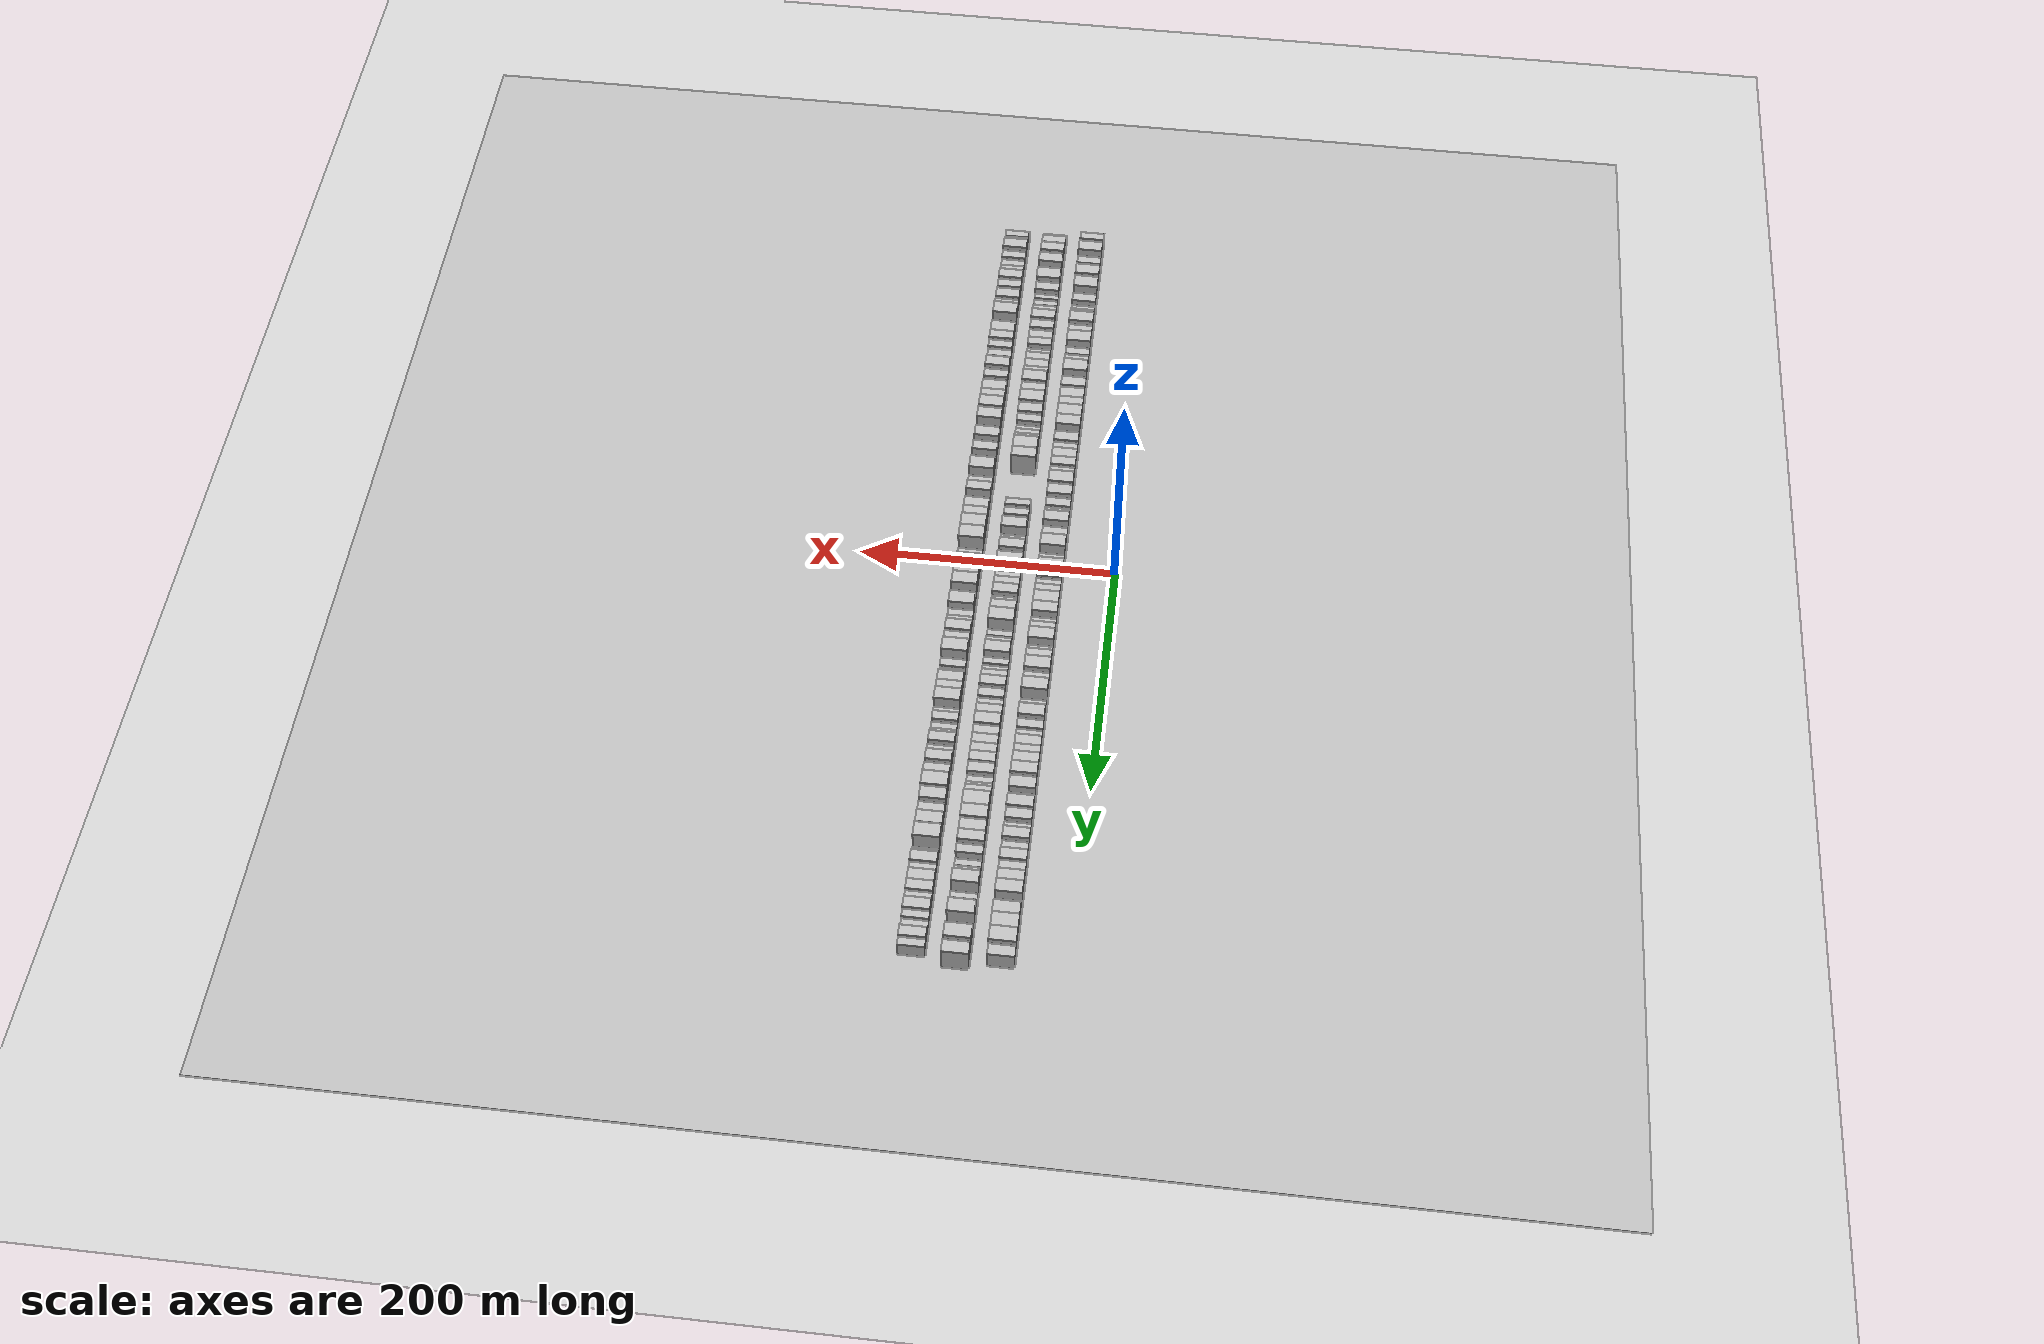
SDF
<?xml version="1.0" encoding="utf-8"?>

<sdf version="1.6">

   <world name="default">

      <gui fullscreen="0">

         <camera name="user_camera">

            <pose>-15 0 4.57585 0 0 0</pose>

            <view_controller>orbit</view_controller>

         </camera>

      </gui>

      <scene>

         <sky>

           <clouds>

             <speed>12</speed>

           </clouds>

         </sky>

         <ambient>0.4 0.4 0.4 1</ambient>

         <background>0.7 0.7 0.7 1</background>

         <shadows>1</shadows>

      </scene>

      <gravity>0 0 -9.8066</gravity>

      <magnetic_field>6e-06 2.3e-05 -4.2e-05</magnetic_field>

      <physics default="0" name="default_physics" type="ode">

         <ode>

            <solver>

               <type>quick</type>

               <iters>10</iters>

               <sor>1.0</sor>

               <use_dynamic_moi_rescaling>0</use_dynamic_moi_rescaling>

            </solver>

            <constraints>

               <cfm>0</cfm>

               <erp>0.2</erp>

               <contact_max_correcting_vel>100</contact_max_correcting_vel>

               <contact_surface_layer>0.001</contact_surface_layer>

            </constraints>

         </ode>

         <max_step_size>0.004</max_step_size>

         <real_time_factor>1</real_time_factor>

         <real_time_update_rate>250</real_time_update_rate>

      </physics>

      <light name="sun" type="directional">

         <cast_shadows>1</cast_shadows>

         <pose>0 0 10 0 0 0</pose>

         <diffuse>0.8 0.8 0.8 1</diffuse>

         <specular>0.2 0.2 0.2 1</specular>

         <attenuation>

            <range>1000</range>

            <constant>0.9</constant>

            <linear>0.01</linear>

            <quadratic>0.001</quadratic>

         </attenuation>

         <direction>-0.5 0.1 -0.9</direction>

      </light>

      <include>

         <name>ground_plane_1</name>

         <uri>model://HANNAS_ground_plane</uri>

         <pose>0 0 0  0 0 0</pose>

      </include>

      <include>

         <name>ground_plane_2</name>

         <uri>model://HANNAS_ground_plane</uri>

         <pose>100 0 0  0 0 0</pose>

      </include>

      <model name="building_1">

         <static>1</static>

         <pose frame="">50.0000 -344.3174 0 0.000000 0.000000 0.000000</pose>

         <link name="link">

            <pose frame="">0 0 9.00 0 0 0</pose>

            <collision name="collision">

               <geometry>

                  <box>

                     <size>20.0000 7.3652 18.0000</size>

                  </box>

               </geometry>

               <max_contacts>10</max_contacts>

               <surface>

                  <contact>

                     <ode/>

                  </contact>

                  <bounce/>

                  <friction>

                     <torsional>

                        <ode/>

                     </torsional>

                     <ode/>

                  </friction>

               </surface>

            </collision>

            <visual name="visual">

               <cast_shadows>0</cast_shadows>

               <geometry>

                  <box>

                     <size>20.0000 7.3652 18.0000</size>

                  </box>

               </geometry>

               <material>

                  <script>

                     <uri>model://HANNAS_wall/materials/scripts</uri>

                     <uri>model://HANNAS_wall/materials/textures</uri>

                     <name>vrc/HANNAS_wall</name>

                  </script>

               </material>

            </visual>

            <self_collide>0</self_collide>

            <enable_wind>0</enable_wind>

            <kinematic>0</kinematic>

         </link>

      </model>

      <model name="building_2">

         <static>1</static>

         <pose frame="">50.0000 -335.5791 0 0.000000 0.000000 0.000000</pose>

         <link name="link">

            <pose frame="">0 0 7.50 0 0 0</pose>

            <collision name="collision">

               <geometry>

                  <box>

                     <size>20.0000 6.1115 15.0000</size>

                  </box>

               </geometry>

               <max_contacts>10</max_contacts>

               <surface>

                  <contact>

                     <ode/>

                  </contact>

                  <bounce/>

                  <friction>

                     <torsional>

                        <ode/>

                     </torsional>

                     <ode/>

                  </friction>

               </surface>

            </collision>

            <visual name="visual">

               <cast_shadows>0</cast_shadows>

               <geometry>

                  <box>

                     <size>20.0000 6.1115 15.0000</size>

                  </box>

               </geometry>

               <material>

                  <script>

                     <uri>model://HANNAS_wall/materials/scripts</uri>

                     <uri>model://HANNAS_wall/materials/textures</uri>

                     <name>vrc/HANNAS_wall</name>

                  </script>

               </material>

            </visual>

            <self_collide>0</self_collide>

            <enable_wind>0</enable_wind>

            <kinematic>0</kinematic>

         </link>

      </model>

      <model name="building_3">

         <static>1</static>

         <pose frame="">50.0000 -327.3274 0 0.000000 0.000000 0.000000</pose>

         <link name="link">

            <pose frame="">0 0 12.00 0 0 0</pose>

            <collision name="collision">

               <geometry>

                  <box>

                     <size>20.0000 10.3918 24.0000</size>

                  </box>

               </geometry>

               <max_contacts>10</max_contacts>

               <surface>

                  <contact>

                     <ode/>

                  </contact>

                  <bounce/>

                  <friction>

                     <torsional>

                        <ode/>

                     </torsional>

                     <ode/>

                  </friction>

               </surface>

            </collision>

            <visual name="visual">

               <cast_shadows>0</cast_shadows>

               <geometry>

                  <box>

                     <size>20.0000 10.3918 24.0000</size>

                  </box>

               </geometry>

               <material>

                  <script>

                     <uri>model://HANNAS_wall/materials/scripts</uri>

                     <uri>model://HANNAS_wall/materials/textures</uri>

                     <name>vrc/HANNAS_wall</name>

                  </script>

               </material>

            </visual>

            <self_collide>0</self_collide>

            <enable_wind>0</enable_wind>

            <kinematic>0</kinematic>

         </link>

      </model>

      <model name="building_4">

         <static>1</static>

         <pose frame="">50.0000 -316.3229 0 0.000000 0.000000 0.000000</pose>

         <link name="link">

            <pose frame="">0 0 9.00 0 0 0</pose>

            <collision name="collision">

               <geometry>

                  <box>

                     <size>20.0000 7.6172 18.0000</size>

                  </box>

               </geometry>

               <max_contacts>10</max_contacts>

               <surface>

                  <contact>

                     <ode/>

                  </contact>

                  <bounce/>

                  <friction>

                     <torsional>

                        <ode/>

                     </torsional>

                     <ode/>

                  </friction>

               </surface>

            </collision>

            <visual name="visual">

               <cast_shadows>0</cast_shadows>

               <geometry>

                  <box>

                     <size>20.0000 7.6172 18.0000</size>

                  </box>

               </geometry>

               <material>

                  <script>

                     <uri>model://HANNAS_wall/materials/scripts</uri>

                     <uri>model://HANNAS_wall/materials/textures</uri>

                     <name>vrc/HANNAS_wall</name>

                  </script>

               </material>

            </visual>

            <self_collide>0</self_collide>

            <enable_wind>0</enable_wind>

            <kinematic>0</kinematic>

         </link>

      </model>

      <model name="building_5">

         <static>1</static>

         <pose frame="">50.0000 -310.0552 0 0.000000 0.000000 0.000000</pose>

         <link name="link">

            <pose frame="">0 0 6.00 0 0 0</pose>

            <collision name="collision">

               <geometry>

                  <box>

                     <size>20.0000 4.9181 12.0000</size>

                  </box>

               </geometry>

               <max_contacts>10</max_contacts>

               <surface>

                  <contact>

                     <ode/>

                  </contact>

                  <bounce/>

                  <friction>

                     <torsional>

                        <ode/>

                     </torsional>

                     <ode/>

                  </friction>

               </surface>

            </collision>

            <visual name="visual">

               <cast_shadows>0</cast_shadows>

               <geometry>

                  <box>

                     <size>20.0000 4.9181 12.0000</size>

                  </box>

               </geometry>

               <material>

                  <script>

                     <uri>model://HANNAS_wall/materials/scripts</uri>

                     <uri>model://HANNAS_wall/materials/textures</uri>

                     <name>vrc/HANNAS_wall</name>

                  </script>

               </material>

            </visual>

            <self_collide>0</self_collide>

            <enable_wind>0</enable_wind>

            <kinematic>0</kinematic>

         </link>

      </model>

      <model name="building_6">

         <static>1</static>

         <pose frame="">50.0000 -300.3728 0 0.000000 0.000000 0.000000</pose>

         <link name="link">

            <pose frame="">0 0 12.00 0 0 0</pose>

            <collision name="collision">

               <geometry>

                  <box>

                     <size>20.0000 10.4468 24.0000</size>

                  </box>

               </geometry>

               <max_contacts>10</max_contacts>

               <surface>

                  <contact>

                     <ode/>

                  </contact>

                  <bounce/>

                  <friction>

                     <torsional>

                        <ode/>

                     </torsional>

                     <ode/>

                  </friction>

               </surface>

            </collision>

            <visual name="visual">

               <cast_shadows>0</cast_shadows>

               <geometry>

                  <box>

                     <size>20.0000 10.4468 24.0000</size>

                  </box>

               </geometry>

               <material>

                  <script>

                     <uri>model://HANNAS_wall/materials/scripts</uri>

                     <uri>model://HANNAS_wall/materials/textures</uri>

                     <name>vrc/HANNAS_wall</name>

                  </script>

               </material>

            </visual>

            <self_collide>0</self_collide>

            <enable_wind>0</enable_wind>

            <kinematic>0</kinematic>

         </link>

      </model>

      <model name="building_7">

         <static>1</static>

         <pose frame="">50.0000 -286.3147 0 0.000000 0.000000 0.000000</pose>

         <link name="link">

            <pose frame="">0 0 12.00 0 0 0</pose>

            <collision name="collision">

               <geometry>

                  <box>

                     <size>20.0000 11.6693 24.0000</size>

                  </box>

               </geometry>

               <max_contacts>10</max_contacts>

               <surface>

                  <contact>

                     <ode/>

                  </contact>

                  <bounce/>

                  <friction>

                     <torsional>

                        <ode/>

                     </torsional>

                     <ode/>

                  </friction>

               </surface>

            </collision>

            <visual name="visual">

               <cast_shadows>0</cast_shadows>

               <geometry>

                  <box>

                     <size>20.0000 11.6693 24.0000</size>

                  </box>

               </geometry>

               <material>

                  <script>

                     <uri>model://HANNAS_wall/materials/scripts</uri>

                     <uri>model://HANNAS_wall/materials/textures</uri>

                     <name>vrc/HANNAS_wall</name>

                  </script>

               </material>

            </visual>

            <self_collide>0</self_collide>

            <enable_wind>0</enable_wind>

            <kinematic>0</kinematic>

         </link>

      </model>

      <model name="building_8">

         <static>1</static>

         <pose frame="">50.0000 -273.2811 0 0.000000 0.000000 0.000000</pose>

         <link name="link">

            <pose frame="">0 0 9.00 0 0 0</pose>

            <collision name="collision">

               <geometry>

                  <box>

                     <size>20.0000 8.3979 18.0000</size>

                  </box>

               </geometry>

               <max_contacts>10</max_contacts>

               <surface>

                  <contact>

                     <ode/>

                  </contact>

                  <bounce/>

                  <friction>

                     <torsional>

                        <ode/>

                     </torsional>

                     <ode/>

                  </friction>

               </surface>

            </collision>

            <visual name="visual">

               <cast_shadows>0</cast_shadows>

               <geometry>

                  <box>

                     <size>20.0000 8.3979 18.0000</size>

                  </box>

               </geometry>

               <material>

                  <script>

                     <uri>model://HANNAS_wall/materials/scripts</uri>

                     <uri>model://HANNAS_wall/materials/textures</uri>

                     <name>vrc/HANNAS_wall</name>

                  </script>

               </material>

            </visual>

            <self_collide>0</self_collide>

            <enable_wind>0</enable_wind>

            <kinematic>0</kinematic>

         </link>

      </model>

      <model name="building_9">

         <static>1</static>

         <pose frame="">50.0000 -262.9646 0 0.000000 0.000000 0.000000</pose>

         <link name="link">

            <pose frame="">0 0 7.50 0 0 0</pose>

            <collision name="collision">

               <geometry>

                  <box>

                     <size>20.0000 6.2351 15.0000</size>

                  </box>

               </geometry>

               <max_contacts>10</max_contacts>

               <surface>

                  <contact>

                     <ode/>

                  </contact>

                  <bounce/>

                  <friction>

                     <torsional>

                        <ode/>

                     </torsional>

                     <ode/>

                  </friction>

               </surface>

            </collision>

            <visual name="visual">

               <cast_shadows>0</cast_shadows>

               <geometry>

                  <box>

                     <size>20.0000 6.2351 15.0000</size>

                  </box>

               </geometry>

               <material>

                  <script>

                     <uri>model://HANNAS_wall/materials/scripts</uri>

                     <uri>model://HANNAS_wall/materials/textures</uri>

                     <name>vrc/HANNAS_wall</name>

                  </script>

               </material>

            </visual>

            <self_collide>0</self_collide>

            <enable_wind>0</enable_wind>

            <kinematic>0</kinematic>

         </link>

      </model>

      <model name="building_10">

         <static>1</static>

         <pose frame="">50.0000 -255.9643 0 0.000000 0.000000 0.000000</pose>

         <link name="link">

            <pose frame="">0 0 9.00 0 0 0</pose>

            <collision name="collision">

               <geometry>

                  <box>

                     <size>20.0000 7.7656 18.0000</size>

                  </box>

               </geometry>

               <max_contacts>10</max_contacts>

               <surface>

                  <contact>

                     <ode/>

                  </contact>

                  <bounce/>

                  <friction>

                     <torsional>

                        <ode/>

                     </torsional>

                     <ode/>

                  </friction>

               </surface>

            </collision>

            <visual name="visual">

               <cast_shadows>0</cast_shadows>

               <geometry>

                  <box>

                     <size>20.0000 7.7656 18.0000</size>

                  </box>

               </geometry>

               <material>

                  <script>

                     <uri>model://HANNAS_wall/materials/scripts</uri>

                     <uri>model://HANNAS_wall/materials/textures</uri>

                     <name>vrc/HANNAS_wall</name>

                  </script>

               </material>

            </visual>

            <self_collide>0</self_collide>

            <enable_wind>0</enable_wind>

            <kinematic>0</kinematic>

         </link>

      </model>

      <model name="building_11">

         <static>1</static>

         <pose frame="">50.0000 -246.6785 0 0.000000 0.000000 0.000000</pose>

         <link name="link">

            <pose frame="">0 0 12.00 0 0 0</pose>

            <collision name="collision">

               <geometry>

                  <box>

                     <size>20.0000 10.8059 24.0000</size>

                  </box>

               </geometry>

               <max_contacts>10</max_contacts>

               <surface>

                  <contact>

                     <ode/>

                  </contact>

                  <bounce/>

                  <friction>

                     <torsional>

                        <ode/>

                     </torsional>

                     <ode/>

                  </friction>

               </surface>

            </collision>

            <visual name="visual">

               <cast_shadows>0</cast_shadows>

               <geometry>

                  <box>

                     <size>20.0000 10.8059 24.0000</size>

                  </box>

               </geometry>

               <material>

                  <script>

                     <uri>model://HANNAS_wall/materials/scripts</uri>

                     <uri>model://HANNAS_wall/materials/textures</uri>

                     <name>vrc/HANNAS_wall</name>

                  </script>

               </material>

            </visual>

            <self_collide>0</self_collide>

            <enable_wind>0</enable_wind>

            <kinematic>0</kinematic>

         </link>

      </model>

      <model name="building_12">

         <static>1</static>

         <pose frame="">50.0000 -234.8860 0 0.000000 0.000000 0.000000</pose>

         <link name="link">

            <pose frame="">0 0 10.50 0 0 0</pose>

            <collision name="collision">

               <geometry>

                  <box>

                     <size>20.0000 8.7792 21.0000</size>

                  </box>

               </geometry>

               <max_contacts>10</max_contacts>

               <surface>

                  <contact>

                     <ode/>

                  </contact>

                  <bounce/>

                  <friction>

                     <torsional>

                        <ode/>

                     </torsional>

                     <ode/>

                  </friction>

               </surface>

            </collision>

            <visual name="visual">

               <cast_shadows>0</cast_shadows>

               <geometry>

                  <box>

                     <size>20.0000 8.7792 21.0000</size>

                  </box>

               </geometry>

               <material>

                  <script>

                     <uri>model://HANNAS_wall/materials/scripts</uri>

                     <uri>model://HANNAS_wall/materials/textures</uri>

                     <name>vrc/HANNAS_wall</name>

                  </script>

               </material>

            </visual>

            <self_collide>0</self_collide>

            <enable_wind>0</enable_wind>

            <kinematic>0</kinematic>

         </link>

      </model>

      <model name="building_13">

         <static>1</static>

         <pose frame="">50.0000 -224.8944 0 0.000000 0.000000 0.000000</pose>

         <link name="link">

            <pose frame="">0 0 12.00 0 0 0</pose>

            <collision name="collision">

               <geometry>

                  <box>

                     <size>20.0000 11.2038 24.0000</size>

                  </box>

               </geometry>

               <max_contacts>10</max_contacts>

               <surface>

                  <contact>

                     <ode/>

                  </contact>

                  <bounce/>

                  <friction>

                     <torsional>

                        <ode/>

                     </torsional>

                     <ode/>

                  </friction>

               </surface>

            </collision>

            <visual name="visual">

               <cast_shadows>0</cast_shadows>

               <geometry>

                  <box>

                     <size>20.0000 11.2038 24.0000</size>

                  </box>

               </geometry>

               <material>

                  <script>

                     <uri>model://HANNAS_wall/materials/scripts</uri>

                     <uri>model://HANNAS_wall/materials/textures</uri>

                     <name>vrc/HANNAS_wall</name>

                  </script>

               </material>

            </visual>

            <self_collide>0</self_collide>

            <enable_wind>0</enable_wind>

            <kinematic>0</kinematic>

         </link>

      </model>

      <model name="building_14">

         <static>1</static>

         <pose frame="">50.0000 -215.6477 0 0.000000 0.000000 0.000000</pose>

         <link name="link">

            <pose frame="">0 0 7.50 0 0 0</pose>

            <collision name="collision">

               <geometry>

                  <box>

                     <size>20.0000 7.2896 15.0000</size>

                  </box>

               </geometry>

               <max_contacts>10</max_contacts>

               <surface>

                  <contact>

                     <ode/>

                  </contact>

                  <bounce/>

                  <friction>

                     <torsional>

                        <ode/>

                     </torsional>

                     <ode/>

                  </friction>

               </surface>

            </collision>

            <visual name="visual">

               <cast_shadows>0</cast_shadows>

               <geometry>

                  <box>

                     <size>20.0000 7.2896 15.0000</size>

                  </box>

               </geometry>

               <material>

                  <script>

                     <uri>model://HANNAS_wall/materials/scripts</uri>

                     <uri>model://HANNAS_wall/materials/textures</uri>

                     <name>vrc/HANNAS_wall</name>

                  </script>

               </material>

            </visual>

            <self_collide>0</self_collide>

            <enable_wind>0</enable_wind>

            <kinematic>0</kinematic>

         </link>

      </model>

      <model name="building_15">

         <static>1</static>

         <pose frame="">50.0000 -207.6275 0 0.000000 0.000000 0.000000</pose>

         <link name="link">

            <pose frame="">0 0 7.50 0 0 0</pose>

            <collision name="collision">

               <geometry>

                  <box>

                     <size>20.0000 6.7509 15.0000</size>

                  </box>

               </geometry>

               <max_contacts>10</max_contacts>

               <surface>

                  <contact>

                     <ode/>

                  </contact>

                  <bounce/>

                  <friction>

                     <torsional>

                        <ode/>

                     </torsional>

                     <ode/>

                  </friction>

               </surface>

            </collision>

            <visual name="visual">

               <cast_shadows>0</cast_shadows>

               <geometry>

                  <box>

                     <size>20.0000 6.7509 15.0000</size>

                  </box>

               </geometry>

               <material>

                  <script>

                     <uri>model://HANNAS_wall/materials/scripts</uri>

                     <uri>model://HANNAS_wall/materials/textures</uri>

                     <name>vrc/HANNAS_wall</name>

                  </script>

               </material>

            </visual>

            <self_collide>0</self_collide>

            <enable_wind>0</enable_wind>

            <kinematic>0</kinematic>

         </link>

      </model>

      <model name="building_16">

         <static>1</static>

         <pose frame="">50.0000 -201.6469 0 0.000000 0.000000 0.000000</pose>

         <link name="link">

            <pose frame="">0 0 6.00 0 0 0</pose>

            <collision name="collision">

               <geometry>

                  <box>

                     <size>20.0000 5.2103 12.0000</size>

                  </box>

               </geometry>

               <max_contacts>10</max_contacts>

               <surface>

                  <contact>

                     <ode/>

                  </contact>

                  <bounce/>

                  <friction>

                     <torsional>

                        <ode/>

                     </torsional>

                     <ode/>

                  </friction>

               </surface>

            </collision>

            <visual name="visual">

               <cast_shadows>0</cast_shadows>

               <geometry>

                  <box>

                     <size>20.0000 5.2103 12.0000</size>

                  </box>

               </geometry>

               <material>

                  <script>

                     <uri>model://HANNAS_wall/materials/scripts</uri>

                     <uri>model://HANNAS_wall/materials/textures</uri>

                     <name>vrc/HANNAS_wall</name>

                  </script>

               </material>

            </visual>

            <self_collide>0</self_collide>

            <enable_wind>0</enable_wind>

            <kinematic>0</kinematic>

         </link>

      </model>

      <model name="building_17">

         <static>1</static>

         <pose frame="">50.0000 -193.1836 0 0.000000 0.000000 0.000000</pose>

         <link name="link">

            <pose frame="">0 0 12.00 0 0 0</pose>

            <collision name="collision">

               <geometry>

                  <box>

                     <size>20.0000 11.7162 24.0000</size>

                  </box>

               </geometry>

               <max_contacts>10</max_contacts>

               <surface>

                  <contact>

                     <ode/>

                  </contact>

                  <bounce/>

                  <friction>

                     <torsional>

                        <ode/>

                     </torsional>

                     <ode/>

                  </friction>

               </surface>

            </collision>

            <visual name="visual">

               <cast_shadows>0</cast_shadows>

               <geometry>

                  <box>

                     <size>20.0000 11.7162 24.0000</size>

                  </box>

               </geometry>

               <material>

                  <script>

                     <uri>model://HANNAS_wall/materials/scripts</uri>

                     <uri>model://HANNAS_wall/materials/textures</uri>

                     <name>vrc/HANNAS_wall</name>

                  </script>

               </material>

            </visual>

            <self_collide>0</self_collide>

            <enable_wind>0</enable_wind>

            <kinematic>0</kinematic>

         </link>

      </model>

      <model name="building_18">

         <static>1</static>

         <pose frame="">50.0000 -184.8197 0 0.000000 0.000000 0.000000</pose>

         <link name="link">

            <pose frame="">0 0 6.00 0 0 0</pose>

            <collision name="collision">

               <geometry>

                  <box>

                     <size>20.0000 5.0117 12.0000</size>

                  </box>

               </geometry>

               <max_contacts>10</max_contacts>

               <surface>

                  <contact>

                     <ode/>

                  </contact>

                  <bounce/>

                  <friction>

                     <torsional>

                        <ode/>

                     </torsional>

                     <ode/>

                  </friction>

               </surface>

            </collision>

            <visual name="visual">

               <cast_shadows>0</cast_shadows>

               <geometry>

                  <box>

                     <size>20.0000 5.0117 12.0000</size>

                  </box>

               </geometry>

               <material>

                  <script>

                     <uri>model://HANNAS_wall/materials/scripts</uri>

                     <uri>model://HANNAS_wall/materials/textures</uri>

                     <name>vrc/HANNAS_wall</name>

                  </script>

               </material>

            </visual>

            <self_collide>0</self_collide>

            <enable_wind>0</enable_wind>

            <kinematic>0</kinematic>

         </link>

      </model>

      <model name="building_19">

         <static>1</static>

         <pose frame="">50.0000 -177.5294 0 0.000000 0.000000 0.000000</pose>

         <link name="link">

            <pose frame="">0 0 10.50 0 0 0</pose>

            <collision name="collision">

               <geometry>

                  <box>

                     <size>20.0000 9.5687 21.0000</size>

                  </box>

               </geometry>

               <max_contacts>10</max_contacts>

               <surface>

                  <contact>

                     <ode/>

                  </contact>

                  <bounce/>

                  <friction>

                     <torsional>

                        <ode/>

                     </torsional>

                     <ode/>

                  </friction>

               </surface>

            </collision>

            <visual name="visual">

               <cast_shadows>0</cast_shadows>

               <geometry>

                  <box>

                     <size>20.0000 9.5687 21.0000</size>

                  </box>

               </geometry>

               <material>

                  <script>

                     <uri>model://HANNAS_wall/materials/scripts</uri>

                     <uri>model://HANNAS_wall/materials/textures</uri>

                     <name>vrc/HANNAS_wall</name>

                  </script>

               </material>

            </visual>

            <self_collide>0</self_collide>

            <enable_wind>0</enable_wind>

            <kinematic>0</kinematic>

         </link>

      </model>

      <model name="building_20">

         <static>1</static>

         <pose frame="">50.0000 -165.7669 0 0.000000 0.000000 0.000000</pose>

         <link name="link">

            <pose frame="">0 0 10.50 0 0 0</pose>

            <collision name="collision">

               <geometry>

                  <box>

                     <size>20.0000 9.9563 21.0000</size>

                  </box>

               </geometry>

               <max_contacts>10</max_contacts>

               <surface>

                  <contact>

                     <ode/>

                  </contact>

                  <bounce/>

                  <friction>

                     <torsional>

                        <ode/>

                     </torsional>

                     <ode/>

                  </friction>

               </surface>

            </collision>

            <visual name="visual">

               <cast_shadows>0</cast_shadows>

               <geometry>

                  <box>

                     <size>20.0000 9.9563 21.0000</size>

                  </box>

               </geometry>

               <material>

                  <script>

                     <uri>model://HANNAS_wall/materials/scripts</uri>

                     <uri>model://HANNAS_wall/materials/textures</uri>

                     <name>vrc/HANNAS_wall</name>

                  </script>

               </material>

            </visual>

            <self_collide>0</self_collide>

            <enable_wind>0</enable_wind>

            <kinematic>0</kinematic>

         </link>

      </model>

      <model name="building_21">

         <static>1</static>

         <pose frame="">50.0000 -155.6899 0 0.000000 0.000000 0.000000</pose>

         <link name="link">

            <pose frame="">0 0 10.50 0 0 0</pose>

            <collision name="collision">

               <geometry>

                  <box>

                     <size>20.0000 10.1979 21.0000</size>

                  </box>

               </geometry>

               <max_contacts>10</max_contacts>

               <surface>

                  <contact>

                     <ode/>

                  </contact>

                  <bounce/>

                  <friction>

                     <torsional>

                        <ode/>

                     </torsional>

                     <ode/>

                  </friction>

               </surface>

            </collision>

            <visual name="visual">

               <cast_shadows>0</cast_shadows>

               <geometry>

                  <box>

                     <size>20.0000 10.1979 21.0000</size>

                  </box>

               </geometry>

               <material>

                  <script>

                     <uri>model://HANNAS_wall/materials/scripts</uri>

                     <uri>model://HANNAS_wall/materials/textures</uri>

                     <name>vrc/HANNAS_wall</name>

                  </script>

               </material>

            </visual>

            <self_collide>0</self_collide>

            <enable_wind>0</enable_wind>

            <kinematic>0</kinematic>

         </link>

      </model>

      <model name="building_22">

         <static>1</static>

         <pose frame="">50.0000 -145.0190 0 0.000000 0.000000 0.000000</pose>

         <link name="link">

            <pose frame="">0 0 12.00 0 0 0</pose>

            <collision name="collision">

               <geometry>

                  <box>

                     <size>20.0000 11.1439 24.0000</size>

                  </box>

               </geometry>

               <max_contacts>10</max_contacts>

               <surface>

                  <contact>

                     <ode/>

                  </contact>

                  <bounce/>

                  <friction>

                     <torsional>

                        <ode/>

                     </torsional>

                     <ode/>

                  </friction>

               </surface>

            </collision>

            <visual name="visual">

               <cast_shadows>0</cast_shadows>

               <geometry>

                  <box>

                     <size>20.0000 11.1439 24.0000</size>

                  </box>

               </geometry>

               <material>

                  <script>

                     <uri>model://HANNAS_wall/materials/scripts</uri>

                     <uri>model://HANNAS_wall/materials/textures</uri>

                     <name>vrc/HANNAS_wall</name>

                  </script>

               </material>

            </visual>

            <self_collide>0</self_collide>

            <enable_wind>0</enable_wind>

            <kinematic>0</kinematic>

         </link>

      </model>

      <model name="building_23">

         <static>1</static>

         <pose frame="">50.0000 -134.2567 0 0.000000 0.000000 0.000000</pose>

         <link name="link">

            <pose frame="">0 0 12.00 0 0 0</pose>

            <collision name="collision">

               <geometry>

                  <box>

                     <size>20.0000 10.3807 24.0000</size>

                  </box>

               </geometry>

               <max_contacts>10</max_contacts>

               <surface>

                  <contact>

                     <ode/>

                  </contact>

                  <bounce/>

                  <friction>

                     <torsional>

                        <ode/>

                     </torsional>

                     <ode/>

                  </friction>

               </surface>

            </collision>

            <visual name="visual">

               <cast_shadows>0</cast_shadows>

               <geometry>

                  <box>

                     <size>20.0000 10.3807 24.0000</size>

                  </box>

               </geometry>

               <material>

                  <script>

                     <uri>model://HANNAS_wall/materials/scripts</uri>

                     <uri>model://HANNAS_wall/materials/textures</uri>

                     <name>vrc/HANNAS_wall</name>

                  </script>

               </material>

            </visual>

            <self_collide>0</self_collide>

            <enable_wind>0</enable_wind>

            <kinematic>0</kinematic>

         </link>

      </model>

      <model name="building_24">

         <static>1</static>

         <pose frame="">50.0000 -126.4037 0 0.000000 0.000000 0.000000</pose>

         <link name="link">

            <pose frame="">0 0 6.00 0 0 0</pose>

            <collision name="collision">

               <geometry>

                  <box>

                     <size>20.0000 5.3253 12.0000</size>

                  </box>

               </geometry>

               <max_contacts>10</max_contacts>

               <surface>

                  <contact>

                     <ode/>

                  </contact>

                  <bounce/>

                  <friction>

                     <torsional>

                        <ode/>

                     </torsional>

                     <ode/>

                  </friction>

               </surface>

            </collision>

            <visual name="visual">

               <cast_shadows>0</cast_shadows>

               <geometry>

                  <box>

                     <size>20.0000 5.3253 12.0000</size>

                  </box>

               </geometry>

               <material>

                  <script>

                     <uri>model://HANNAS_wall/materials/scripts</uri>

                     <uri>model://HANNAS_wall/materials/textures</uri>

                     <name>vrc/HANNAS_wall</name>

                  </script>

               </material>

            </visual>

            <self_collide>0</self_collide>

            <enable_wind>0</enable_wind>

            <kinematic>0</kinematic>

         </link>

      </model>

      <model name="building_25">

         <static>1</static>

         <pose frame="">50.0000 -119.1448 0 0.000000 0.000000 0.000000</pose>

         <link name="link">

            <pose frame="">0 0 10.50 0 0 0</pose>

            <collision name="collision">

               <geometry>

                  <box>

                     <size>20.0000 9.1926 21.0000</size>

                  </box>

               </geometry>

               <max_contacts>10</max_contacts>

               <surface>

                  <contact>

                     <ode/>

                  </contact>

                  <bounce/>

                  <friction>

                     <torsional>

                        <ode/>

                     </torsional>

                     <ode/>

                  </friction>

               </surface>

            </collision>

            <visual name="visual">

               <cast_shadows>0</cast_shadows>

               <geometry>

                  <box>

                     <size>20.0000 9.1926 21.0000</size>

                  </box>

               </geometry>

               <material>

                  <script>

                     <uri>model://HANNAS_wall/materials/scripts</uri>

                     <uri>model://HANNAS_wall/materials/textures</uri>

                     <name>vrc/HANNAS_wall</name>

                  </script>

               </material>

            </visual>

            <self_collide>0</self_collide>

            <enable_wind>0</enable_wind>

            <kinematic>0</kinematic>

         </link>

      </model>

      <model name="building_26">

         <static>1</static>

         <pose frame="">50.0000 -110.6058 0 0.000000 0.000000 0.000000</pose>

         <link name="link">

            <pose frame="">0 0 9.00 0 0 0</pose>

            <collision name="collision">

               <geometry>

                  <box>

                     <size>20.0000 7.8854 18.0000</size>

                  </box>

               </geometry>

               <max_contacts>10</max_contacts>

               <surface>

                  <contact>

                     <ode/>

                  </contact>

                  <bounce/>

                  <friction>

                     <torsional>

                        <ode/>

                     </torsional>

                     <ode/>

                  </friction>

               </surface>

            </collision>

            <visual name="visual">

               <cast_shadows>0</cast_shadows>

               <geometry>

                  <box>

                     <size>20.0000 7.8854 18.0000</size>

                  </box>

               </geometry>

               <material>

                  <script>

                     <uri>model://HANNAS_wall/materials/scripts</uri>

                     <uri>model://HANNAS_wall/materials/textures</uri>

                     <name>vrc/HANNAS_wall</name>

                  </script>

               </material>

            </visual>

            <self_collide>0</self_collide>

            <enable_wind>0</enable_wind>

            <kinematic>0</kinematic>

         </link>

      </model>

      <model name="building_27">

         <static>1</static>

         <pose frame="">50.0000 -102.2128 0 0.000000 0.000000 0.000000</pose>

         <link name="link">

            <pose frame="">0 0 10.50 0 0 0</pose>

            <collision name="collision">

               <geometry>

                  <box>

                     <size>20.0000 8.9005 21.0000</size>

                  </box>

               </geometry>

               <max_contacts>10</max_contacts>

               <surface>

                  <contact>

                     <ode/>

                  </contact>

                  <bounce/>

                  <friction>

                     <torsional>

                        <ode/>

                     </torsional>

                     <ode/>

                  </friction>

               </surface>

            </collision>

            <visual name="visual">

               <cast_shadows>0</cast_shadows>

               <geometry>

                  <box>

                     <size>20.0000 8.9005 21.0000</size>

                  </box>

               </geometry>

               <material>

                  <script>

                     <uri>model://HANNAS_wall/materials/scripts</uri>

                     <uri>model://HANNAS_wall/materials/textures</uri>

                     <name>vrc/HANNAS_wall</name>

                  </script>

               </material>

            </visual>

            <self_collide>0</self_collide>

            <enable_wind>0</enable_wind>

            <kinematic>0</kinematic>

         </link>

      </model>

      <model name="building_28">

         <static>1</static>

         <pose frame="">50.0000 -93.5541 0 0.000000 0.000000 0.000000</pose>

         <link name="link">

            <pose frame="">0 0 10.50 0 0 0</pose>

            <collision name="collision">

               <geometry>

                  <box>

                     <size>20.0000 8.4169 21.0000</size>

                  </box>

               </geometry>

               <max_contacts>10</max_contacts>

               <surface>

                  <contact>

                     <ode/>

                  </contact>

                  <bounce/>

                  <friction>

                     <torsional>

                        <ode/>

                     </torsional>

                     <ode/>

                  </friction>

               </surface>

            </collision>

            <visual name="visual">

               <cast_shadows>0</cast_shadows>

               <geometry>

                  <box>

                     <size>20.0000 8.4169 21.0000</size>

                  </box>

               </geometry>

               <material>

                  <script>

                     <uri>model://HANNAS_wall/materials/scripts</uri>

                     <uri>model://HANNAS_wall/materials/textures</uri>

                     <name>vrc/HANNAS_wall</name>

                  </script>

               </material>

            </visual>

            <self_collide>0</self_collide>

            <enable_wind>0</enable_wind>

            <kinematic>0</kinematic>

         </link>

      </model>

      <model name="building_29">

         <static>1</static>

         <pose frame="">50.0000 -85.0330 0 0.000000 0.000000 0.000000</pose>

         <link name="link">

            <pose frame="">0 0 9.00 0 0 0</pose>

            <collision name="collision">

               <geometry>

                  <box>

                     <size>20.0000 8.6251 18.0000</size>

                  </box>

               </geometry>

               <max_contacts>10</max_contacts>

               <surface>

                  <contact>

                     <ode/>

                  </contact>

                  <bounce/>

                  <friction>

                     <torsional>

                        <ode/>

                     </torsional>

                     <ode/>

                  </friction>

               </surface>

            </collision>

            <visual name="visual">

               <cast_shadows>0</cast_shadows>

               <geometry>

                  <box>

                     <size>20.0000 8.6251 18.0000</size>

                  </box>

               </geometry>

               <material>

                  <script>

                     <uri>model://HANNAS_wall/materials/scripts</uri>

                     <uri>model://HANNAS_wall/materials/textures</uri>

                     <name>vrc/HANNAS_wall</name>

                  </script>

               </material>

            </visual>

            <self_collide>0</self_collide>

            <enable_wind>0</enable_wind>

            <kinematic>0</kinematic>

         </link>

      </model>

      <model name="building_30">

         <static>1</static>

         <pose frame="">50.0000 -75.2321 0 0.000000 0.000000 0.000000</pose>

         <link name="link">

            <pose frame="">0 0 12.00 0 0 0</pose>

            <collision name="collision">

               <geometry>

                  <box>

                     <size>20.0000 10.9767 24.0000</size>

                  </box>

               </geometry>

               <max_contacts>10</max_contacts>

               <surface>

                  <contact>

                     <ode/>

                  </contact>

                  <bounce/>

                  <friction>

                     <torsional>

                        <ode/>

                     </torsional>

                     <ode/>

                  </friction>

               </surface>

            </collision>

            <visual name="visual">

               <cast_shadows>0</cast_shadows>

               <geometry>

                  <box>

                     <size>20.0000 10.9767 24.0000</size>

                  </box>

               </geometry>

               <material>

                  <script>

                     <uri>model://HANNAS_wall/materials/scripts</uri>

                     <uri>model://HANNAS_wall/materials/textures</uri>

                     <name>vrc/HANNAS_wall</name>

                  </script>

               </material>

            </visual>

            <self_collide>0</self_collide>

            <enable_wind>0</enable_wind>

            <kinematic>0</kinematic>

         </link>

      </model>

      <model name="building_31">

         <static>1</static>

         <pose frame="">50.0000 -64.7519 0 0.000000 0.000000 0.000000</pose>

         <link name="link">

            <pose frame="">0 0 10.50 0 0 0</pose>

            <collision name="collision">

               <geometry>

                  <box>

                     <size>20.0000 9.9836 21.0000</size>

                  </box>

               </geometry>

               <max_contacts>10</max_contacts>

               <surface>

                  <contact>

                     <ode/>

                  </contact>

                  <bounce/>

                  <friction>

                     <torsional>

                        <ode/>

                     </torsional>

                     <ode/>

                  </friction>

               </surface>

            </collision>

            <visual name="visual">

               <cast_shadows>0</cast_shadows>

               <geometry>

                  <box>

                     <size>20.0000 9.9836 21.0000</size>

                  </box>

               </geometry>

               <material>

                  <script>

                     <uri>model://HANNAS_wall/materials/scripts</uri>

                     <uri>model://HANNAS_wall/materials/textures</uri>

                     <name>vrc/HANNAS_wall</name>

                  </script>

               </material>

            </visual>

            <self_collide>0</self_collide>

            <enable_wind>0</enable_wind>

            <kinematic>0</kinematic>

         </link>

      </model>

      <model name="building_32">

         <static>1</static>

         <pose frame="">50.0000 -53.7000 0 0.000000 0.000000 0.000000</pose>

         <link name="link">

            <pose frame="">0 0 9.00 0 0 0</pose>

            <collision name="collision">

               <geometry>

                  <box>

                     <size>20.0000 8.1202 18.0000</size>

                  </box>

               </geometry>

               <max_contacts>10</max_contacts>

               <surface>

                  <contact>

                     <ode/>

                  </contact>

                  <bounce/>

                  <friction>

                     <torsional>

                        <ode/>

                     </torsional>

                     <ode/>

                  </friction>

               </surface>

            </collision>

            <visual name="visual">

               <cast_shadows>0</cast_shadows>

               <geometry>

                  <box>

                     <size>20.0000 8.1202 18.0000</size>

                  </box>

               </geometry>

               <material>

                  <script>

                     <uri>model://HANNAS_wall/materials/scripts</uri>

                     <uri>model://HANNAS_wall/materials/textures</uri>

                     <name>vrc/HANNAS_wall</name>

                  </script>

               </material>

            </visual>

            <self_collide>0</self_collide>

            <enable_wind>0</enable_wind>

            <kinematic>0</kinematic>

         </link>

      </model>

      <model name="building_33">

         <static>1</static>

         <pose frame="">50.0000 -46.1428 0 0.000000 0.000000 0.000000</pose>

         <link name="link">

            <pose frame="">0 0 7.50 0 0 0</pose>

            <collision name="collision">

               <geometry>

                  <box>

                     <size>20.0000 6.9942 15.0000</size>

                  </box>

               </geometry>

               <max_contacts>10</max_contacts>

               <surface>

                  <contact>

                     <ode/>

                  </contact>

                  <bounce/>

                  <friction>

                     <torsional>

                        <ode/>

                     </torsional>

                     <ode/>

                  </friction>

               </surface>

            </collision>

            <visual name="visual">

               <cast_shadows>0</cast_shadows>

               <geometry>

                  <box>

                     <size>20.0000 6.9942 15.0000</size>

                  </box>

               </geometry>

               <material>

                  <script>

                     <uri>model://HANNAS_wall/materials/scripts</uri>

                     <uri>model://HANNAS_wall/materials/textures</uri>

                     <name>vrc/HANNAS_wall</name>

                  </script>

               </material>

            </visual>

            <self_collide>0</self_collide>

            <enable_wind>0</enable_wind>

            <kinematic>0</kinematic>

         </link>

      </model>

      <model name="building_34">

         <static>1</static>

         <pose frame="">50.0000 -37.7220 0 0.000000 0.000000 0.000000</pose>

         <link name="link">

            <pose frame="">0 0 10.50 0 0 0</pose>

            <collision name="collision">

               <geometry>

                  <box>

                     <size>20.0000 9.8475 21.0000</size>

                  </box>

               </geometry>

               <max_contacts>10</max_contacts>

               <surface>

                  <contact>

                     <ode/>

                  </contact>

                  <bounce/>

                  <friction>

                     <torsional>

                        <ode/>

                     </torsional>

                     <ode/>

                  </friction>

               </surface>

            </collision>

            <visual name="visual">

               <cast_shadows>0</cast_shadows>

               <geometry>

                  <box>

                     <size>20.0000 9.8475 21.0000</size>

                  </box>

               </geometry>

               <material>

                  <script>

                     <uri>model://HANNAS_wall/materials/scripts</uri>

                     <uri>model://HANNAS_wall/materials/textures</uri>

                     <name>vrc/HANNAS_wall</name>

                  </script>

               </material>

            </visual>

            <self_collide>0</self_collide>

            <enable_wind>0</enable_wind>

            <kinematic>0</kinematic>

         </link>

      </model>

      <model name="building_35">

         <static>1</static>

         <pose frame="">50.0000 -27.1019 0 0.000000 0.000000 0.000000</pose>

         <link name="link">

            <pose frame="">0 0 7.50 0 0 0</pose>

            <collision name="collision">

               <geometry>

                  <box>

                     <size>20.0000 7.3927 15.0000</size>

                  </box>

               </geometry>

               <max_contacts>10</max_contacts>

               <surface>

                  <contact>

                     <ode/>

                  </contact>

                  <bounce/>

                  <friction>

                     <torsional>

                        <ode/>

                     </torsional>

                     <ode/>

                  </friction>

               </surface>

            </collision>

            <visual name="visual">

               <cast_shadows>0</cast_shadows>

               <geometry>

                  <box>

                     <size>20.0000 7.3927 15.0000</size>

                  </box>

               </geometry>

               <material>

                  <script>

                     <uri>model://HANNAS_wall/materials/scripts</uri>

                     <uri>model://HANNAS_wall/materials/textures</uri>

                     <name>vrc/HANNAS_wall</name>

                  </script>

               </material>

            </visual>

            <self_collide>0</self_collide>

            <enable_wind>0</enable_wind>

            <kinematic>0</kinematic>

         </link>

      </model>

      <model name="building_36">

         <static>1</static>

         <pose frame="">50.0000 -19.7818 0 0.000000 0.000000 0.000000</pose>

         <link name="link">

            <pose frame="">0 0 6.00 0 0 0</pose>

            <collision name="collision">

               <geometry>

                  <box>

                     <size>20.0000 5.2476 12.0000</size>

                  </box>

               </geometry>

               <max_contacts>10</max_contacts>

               <surface>

                  <contact>

                     <ode/>

                  </contact>

                  <bounce/>

                  <friction>

                     <torsional>

                        <ode/>

                     </torsional>

                     <ode/>

                  </friction>

               </surface>

            </collision>

            <visual name="visual">

               <cast_shadows>0</cast_shadows>

               <geometry>

                  <box>

                     <size>20.0000 5.2476 12.0000</size>

                  </box>

               </geometry>

               <material>

                  <script>

                     <uri>model://HANNAS_wall/materials/scripts</uri>

                     <uri>model://HANNAS_wall/materials/textures</uri>

                     <name>vrc/HANNAS_wall</name>

                  </script>

               </material>

            </visual>

            <self_collide>0</self_collide>

            <enable_wind>0</enable_wind>

            <kinematic>0</kinematic>

         </link>

      </model>

      <model name="building_37">

         <static>1</static>

         <pose frame="">50.0000 -11.6371 0 0.000000 0.000000 0.000000</pose>

         <link name="link">

            <pose frame="">0 0 12.00 0 0 0</pose>

            <collision name="collision">

               <geometry>

                  <box>

                     <size>20.0000 11.0417 24.0000</size>

                  </box>

               </geometry>

               <max_contacts>10</max_contacts>

               <surface>

                  <contact>

                     <ode/>

                  </contact>

                  <bounce/>

                  <friction>

                     <torsional>

                        <ode/>

                     </torsional>

                     <ode/>

                  </friction>

               </surface>

            </collision>

            <visual name="visual">

               <cast_shadows>0</cast_shadows>

               <geometry>

                  <box>

                     <size>20.0000 11.0417 24.0000</size>

                  </box>

               </geometry>

               <material>

                  <script>

                     <uri>model://HANNAS_wall/materials/scripts</uri>

                     <uri>model://HANNAS_wall/materials/textures</uri>

                     <name>vrc/HANNAS_wall</name>

                  </script>

               </material>

            </visual>

            <self_collide>0</self_collide>

            <enable_wind>0</enable_wind>

            <kinematic>0</kinematic>

         </link>

      </model>

      <model name="building_38">

         <static>1</static>

         <pose frame="">50.0000 -3.2263 0 0.000000 0.000000 0.000000</pose>

         <link name="link">

            <pose frame="">0 0 6.00 0 0 0</pose>

            <collision name="collision">

               <geometry>

                  <box>

                     <size>20.0000 5.7800 12.0000</size>

                  </box>

               </geometry>

               <max_contacts>10</max_contacts>

               <surface>

                  <contact>

                     <ode/>

                  </contact>

                  <bounce/>

                  <friction>

                     <torsional>

                        <ode/>

                     </torsional>

                     <ode/>

                  </friction>

               </surface>

            </collision>

            <visual name="visual">

               <cast_shadows>0</cast_shadows>

               <geometry>

                  <box>

                     <size>20.0000 5.7800 12.0000</size>

                  </box>

               </geometry>

               <material>

                  <script>

                     <uri>model://HANNAS_wall/materials/scripts</uri>

                     <uri>model://HANNAS_wall/materials/textures</uri>

                     <name>vrc/HANNAS_wall</name>

                  </script>

               </material>

            </visual>

            <self_collide>0</self_collide>

            <enable_wind>0</enable_wind>

            <kinematic>0</kinematic>

         </link>

      </model>

      <model name="building_39">

         <static>1</static>

         <pose frame="">50.0000 6.0282 0 0.000000 0.000000 0.000000</pose>

         <link name="link">

            <pose frame="">0 0 9.00 0 0 0</pose>

            <collision name="collision">

               <geometry>

                  <box>

                     <size>20.0000 8.7289 18.0000</size>

                  </box>

               </geometry>

               <max_contacts>10</max_contacts>

               <surface>

                  <contact>

                     <ode/>

                  </contact>

                  <bounce/>

                  <friction>

                     <torsional>

                        <ode/>

                     </torsional>

                     <ode/>

                  </friction>

               </surface>

            </collision>

            <visual name="visual">

               <cast_shadows>0</cast_shadows>

               <geometry>

                  <box>

                     <size>20.0000 8.7289 18.0000</size>

                  </box>

               </geometry>

               <material>

                  <script>

                     <uri>model://HANNAS_wall/materials/scripts</uri>

                     <uri>model://HANNAS_wall/materials/textures</uri>

                     <name>vrc/HANNAS_wall</name>

                  </script>

               </material>

            </visual>

            <self_collide>0</self_collide>

            <enable_wind>0</enable_wind>

            <kinematic>0</kinematic>

         </link>

      </model>

      <model name="building_40">

         <static>1</static>

         <pose frame="">50.0000 14.0486 0 0.000000 0.000000 0.000000</pose>

         <link name="link">

            <pose frame="">0 0 7.50 0 0 0</pose>

            <collision name="collision">

               <geometry>

                  <box>

                     <size>20.0000 7.3120 15.0000</size>

                  </box>

               </geometry>

               <max_contacts>10</max_contacts>

               <surface>

                  <contact>

                     <ode/>

                  </contact>

                  <bounce/>

                  <friction>

                     <torsional>

                        <ode/>

                     </torsional>

                     <ode/>

                  </friction>

               </surface>

            </collision>

            <visual name="visual">

               <cast_shadows>0</cast_shadows>

               <geometry>

                  <box>

                     <size>20.0000 7.3120 15.0000</size>

                  </box>

               </geometry>

               <material>

                  <script>

                     <uri>model://HANNAS_wall/materials/scripts</uri>

                     <uri>model://HANNAS_wall/materials/textures</uri>

                     <name>vrc/HANNAS_wall</name>

                  </script>

               </material>

            </visual>

            <self_collide>0</self_collide>

            <enable_wind>0</enable_wind>

            <kinematic>0</kinematic>

         </link>

      </model>

      <model name="building_41">

         <static>1</static>

         <pose frame="">50.0000 24.1313 0 0.000000 0.000000 0.000000</pose>

         <link name="link">

            <pose frame="">0 0 7.50 0 0 0</pose>

            <collision name="collision">

               <geometry>

                  <box>

                     <size>20.0000 6.8536 15.0000</size>

                  </box>

               </geometry>

               <max_contacts>10</max_contacts>

               <surface>

                  <contact>

                     <ode/>

                  </contact>

                  <bounce/>

                  <friction>

                     <torsional>

                        <ode/>

                     </torsional>

                     <ode/>

                  </friction>

               </surface>

            </collision>

            <visual name="visual">

               <cast_shadows>0</cast_shadows>

               <geometry>

                  <box>

                     <size>20.0000 6.8536 15.0000</size>

                  </box>

               </geometry>

               <material>

                  <script>

                     <uri>model://HANNAS_wall/materials/scripts</uri>

                     <uri>model://HANNAS_wall/materials/textures</uri>

                     <name>vrc/HANNAS_wall</name>

                  </script>

               </material>

            </visual>

            <self_collide>0</self_collide>

            <enable_wind>0</enable_wind>

            <kinematic>0</kinematic>

         </link>

      </model>

      <model name="building_42">

         <static>1</static>

         <pose frame="">50.0000 31.6831 0 0.000000 0.000000 0.000000</pose>

         <link name="link">

            <pose frame="">0 0 9.00 0 0 0</pose>

            <collision name="collision">

               <geometry>

                  <box>

                     <size>20.0000 8.2501 18.0000</size>

                  </box>

               </geometry>

               <max_contacts>10</max_contacts>

               <surface>

                  <contact>

                     <ode/>

                  </contact>

                  <bounce/>

                  <friction>

                     <torsional>

                        <ode/>

                     </torsional>

                     <ode/>

                  </friction>

               </surface>

            </collision>

            <visual name="visual">

               <cast_shadows>0</cast_shadows>

               <geometry>

                  <box>

                     <size>20.0000 8.2501 18.0000</size>

                  </box>

               </geometry>

               <material>

                  <script>

                     <uri>model://HANNAS_wall/materials/scripts</uri>

                     <uri>model://HANNAS_wall/materials/textures</uri>

                     <name>vrc/HANNAS_wall</name>

                  </script>

               </material>

            </visual>

            <self_collide>0</self_collide>

            <enable_wind>0</enable_wind>

            <kinematic>0</kinematic>

         </link>

      </model>

      <model name="building_43">

         <static>1</static>

         <pose frame="">50.0000 40.9105 0 0.000000 0.000000 0.000000</pose>

         <link name="link">

            <pose frame="">0 0 10.50 0 0 0</pose>

            <collision name="collision">

               <geometry>

                  <box>

                     <size>20.0000 10.2048 21.0000</size>

                  </box>

               </geometry>

               <max_contacts>10</max_contacts>

               <surface>

                  <contact>

                     <ode/>

                  </contact>

                  <bounce/>

                  <friction>

                     <torsional>

                        <ode/>

                     </torsional>

                     <ode/>

                  </friction>

               </surface>

            </collision>

            <visual name="visual">

               <cast_shadows>0</cast_shadows>

               <geometry>

                  <box>

                     <size>20.0000 10.2048 21.0000</size>

                  </box>

               </geometry>

               <material>

                  <script>

                     <uri>model://HANNAS_wall/materials/scripts</uri>

                     <uri>model://HANNAS_wall/materials/textures</uri>

                     <name>vrc/HANNAS_wall</name>

                  </script>

               </material>

            </visual>

            <self_collide>0</self_collide>

            <enable_wind>0</enable_wind>

            <kinematic>0</kinematic>

         </link>

      </model>

      <model name="building_44">

         <static>1</static>

         <pose frame="">50.0000 50.8271 0 0.000000 0.000000 0.000000</pose>

         <link name="link">

            <pose frame="">0 0 10.50 0 0 0</pose>

            <collision name="collision">

               <geometry>

                  <box>

                     <size>20.0000 9.6284 21.0000</size>

                  </box>

               </geometry>

               <max_contacts>10</max_contacts>

               <surface>

                  <contact>

                     <ode/>

                  </contact>

                  <bounce/>

                  <friction>

                     <torsional>

                        <ode/>

                     </torsional>

                     <ode/>

                  </friction>

               </surface>

            </collision>

            <visual name="visual">

               <cast_shadows>0</cast_shadows>

               <geometry>

                  <box>

                     <size>20.0000 9.6284 21.0000</size>

                  </box>

               </geometry>

               <material>

                  <script>

                     <uri>model://HANNAS_wall/materials/scripts</uri>

                     <uri>model://HANNAS_wall/materials/textures</uri>

                     <name>vrc/HANNAS_wall</name>

                  </script>

               </material>

            </visual>

            <self_collide>0</self_collide>

            <enable_wind>0</enable_wind>

            <kinematic>0</kinematic>

         </link>

      </model>

      <model name="building_45">

         <static>1</static>

         <pose frame="">50.0000 58.5108 0 0.000000 0.000000 0.000000</pose>

         <link name="link">

            <pose frame="">0 0 6.00 0 0 0</pose>

            <collision name="collision">

               <geometry>

                  <box>

                     <size>20.0000 5.7389 12.0000</size>

                  </box>

               </geometry>

               <max_contacts>10</max_contacts>

               <surface>

                  <contact>

                     <ode/>

                  </contact>

                  <bounce/>

                  <friction>

                     <torsional>

                        <ode/>

                     </torsional>

                     <ode/>

                  </friction>

               </surface>

            </collision>

            <visual name="visual">

               <cast_shadows>0</cast_shadows>

               <geometry>

                  <box>

                     <size>20.0000 5.7389 12.0000</size>

                  </box>

               </geometry>

               <material>

                  <script>

                     <uri>model://HANNAS_wall/materials/scripts</uri>

                     <uri>model://HANNAS_wall/materials/textures</uri>

                     <name>vrc/HANNAS_wall</name>

                  </script>

               </material>

            </visual>

            <self_collide>0</self_collide>

            <enable_wind>0</enable_wind>

            <kinematic>0</kinematic>

         </link>

      </model>

      <model name="building_46">

         <static>1</static>

         <pose frame="">50.0000 67.0606 0 0.000000 0.000000 0.000000</pose>

         <link name="link">

            <pose frame="">0 0 9.00 0 0 0</pose>

            <collision name="collision">

               <geometry>

                  <box>

                     <size>20.0000 7.3606 18.0000</size>

                  </box>

               </geometry>

               <max_contacts>10</max_contacts>

               <surface>

                  <contact>

                     <ode/>

                  </contact>

                  <bounce/>

                  <friction>

                     <torsional>

                        <ode/>

                     </torsional>

                     <ode/>

                  </friction>

               </surface>

            </collision>

            <visual name="visual">

               <cast_shadows>0</cast_shadows>

               <geometry>

                  <box>

                     <size>20.0000 7.3606 18.0000</size>

                  </box>

               </geometry>

               <material>

                  <script>

                     <uri>model://HANNAS_wall/materials/scripts</uri>

                     <uri>model://HANNAS_wall/materials/textures</uri>

                     <name>vrc/HANNAS_wall</name>

                  </script>

               </material>

            </visual>

            <self_collide>0</self_collide>

            <enable_wind>0</enable_wind>

            <kinematic>0</kinematic>

         </link>

      </model>

      <model name="building_47">

         <static>1</static>

         <pose frame="">50.0000 77.8903 0 0.000000 0.000000 0.000000</pose>

         <link name="link">

            <pose frame="">0 0 12.00 0 0 0</pose>

            <collision name="collision">

               <geometry>

                  <box>

                     <size>20.0000 10.2989 24.0000</size>

                  </box>

               </geometry>

               <max_contacts>10</max_contacts>

               <surface>

                  <contact>

                     <ode/>

                  </contact>

                  <bounce/>

                  <friction>

                     <torsional>

                        <ode/>

                     </torsional>

                     <ode/>

                  </friction>

               </surface>

            </collision>

            <visual name="visual">

               <cast_shadows>0</cast_shadows>

               <geometry>

                  <box>

                     <size>20.0000 10.2989 24.0000</size>

                  </box>

               </geometry>

               <material>

                  <script>

                     <uri>model://HANNAS_wall/materials/scripts</uri>

                     <uri>model://HANNAS_wall/materials/textures</uri>

                     <name>vrc/HANNAS_wall</name>

                  </script>

               </material>

            </visual>

            <self_collide>0</self_collide>

            <enable_wind>0</enable_wind>

            <kinematic>0</kinematic>

         </link>

      </model>

      <model name="building_48">

         <static>1</static>

         <pose frame="">50.0000 87.4814 0 0.000000 0.000000 0.000000</pose>

         <link name="link">

            <pose frame="">0 0 7.50 0 0 0</pose>

            <collision name="collision">

               <geometry>

                  <box>

                     <size>20.0000 6.8834 15.0000</size>

                  </box>

               </geometry>

               <max_contacts>10</max_contacts>

               <surface>

                  <contact>

                     <ode/>

                  </contact>

                  <bounce/>

                  <friction>

                     <torsional>

                        <ode/>

                     </torsional>

                     <ode/>

                  </friction>

               </surface>

            </collision>

            <visual name="visual">

               <cast_shadows>0</cast_shadows>

               <geometry>

                  <box>

                     <size>20.0000 6.8834 15.0000</size>

                  </box>

               </geometry>

               <material>

                  <script>

                     <uri>model://HANNAS_wall/materials/scripts</uri>

                     <uri>model://HANNAS_wall/materials/textures</uri>

                     <name>vrc/HANNAS_wall</name>

                  </script>

               </material>

            </visual>

            <self_collide>0</self_collide>

            <enable_wind>0</enable_wind>

            <kinematic>0</kinematic>

         </link>

      </model>

      <model name="building_49">

         <static>1</static>

         <pose frame="">50.0000 95.2231 0 0.000000 0.000000 0.000000</pose>

         <link name="link">

            <pose frame="">0 0 10.50 0 0 0</pose>

            <collision name="collision">

               <geometry>

                  <box>

                     <size>20.0000 8.5998 21.0000</size>

                  </box>

               </geometry>

               <max_contacts>10</max_contacts>

               <surface>

                  <contact>

                     <ode/>

                  </contact>

                  <bounce/>

                  <friction>

                     <torsional>

                        <ode/>

                     </torsional>

                     <ode/>

                  </friction>

               </surface>

            </collision>

            <visual name="visual">

               <cast_shadows>0</cast_shadows>

               <geometry>

                  <box>

                     <size>20.0000 8.5998 21.0000</size>

                  </box>

               </geometry>

               <material>

                  <script>

                     <uri>model://HANNAS_wall/materials/scripts</uri>

                     <uri>model://HANNAS_wall/materials/textures</uri>

                     <name>vrc/HANNAS_wall</name>

                  </script>

               </material>

            </visual>

            <self_collide>0</self_collide>

            <enable_wind>0</enable_wind>

            <kinematic>0</kinematic>

         </link>

      </model>

      <model name="building_50">

         <static>1</static>

         <pose frame="">50.0000 104.9872 0 0.000000 0.000000 0.000000</pose>

         <link name="link">

            <pose frame="">0 0 12.00 0 0 0</pose>

            <collision name="collision">

               <geometry>

                  <box>

                     <size>20.0000 10.9284 24.0000</size>

                  </box>

               </geometry>

               <max_contacts>10</max_contacts>

               <surface>

                  <contact>

                     <ode/>

                  </contact>

                  <bounce/>

                  <friction>

                     <torsional>

                        <ode/>

                     </torsional>

                     <ode/>

                  </friction>

               </surface>

            </collision>

            <visual name="visual">

               <cast_shadows>0</cast_shadows>

               <geometry>

                  <box>

                     <size>20.0000 10.9284 24.0000</size>

                  </box>

               </geometry>

               <material>

                  <script>

                     <uri>model://HANNAS_wall/materials/scripts</uri>

                     <uri>model://HANNAS_wall/materials/textures</uri>

                     <name>vrc/HANNAS_wall</name>

                  </script>

               </material>

            </visual>

            <self_collide>0</self_collide>

            <enable_wind>0</enable_wind>

            <kinematic>0</kinematic>

         </link>

      </model>

      <model name="building_51">

         <static>1</static>

         <pose frame="">50.0000 114.6796 0 0.000000 0.000000 0.000000</pose>

         <link name="link">

            <pose frame="">0 0 9.00 0 0 0</pose>

            <collision name="collision">

               <geometry>

                  <box>

                     <size>20.0000 8.4564 18.0000</size>

                  </box>

               </geometry>

               <max_contacts>10</max_contacts>

               <surface>

                  <contact>

                     <ode/>

                  </contact>

                  <bounce/>

                  <friction>

                     <torsional>

                        <ode/>

                     </torsional>

                     <ode/>

                  </friction>

               </surface>

            </collision>

            <visual name="visual">

               <cast_shadows>0</cast_shadows>

               <geometry>

                  <box>

                     <size>20.0000 8.4564 18.0000</size>

                  </box>

               </geometry>

               <material>

                  <script>

                     <uri>model://HANNAS_wall/materials/scripts</uri>

                     <uri>model://HANNAS_wall/materials/textures</uri>

                     <name>vrc/HANNAS_wall</name>

                  </script>

               </material>

            </visual>

            <self_collide>0</self_collide>

            <enable_wind>0</enable_wind>

            <kinematic>0</kinematic>

         </link>

      </model>

      <model name="building_52">

         <static>1</static>

         <pose frame="">50.0000 124.3021 0 0.000000 0.000000 0.000000</pose>

         <link name="link">

            <pose frame="">0 0 12.00 0 0 0</pose>

            <collision name="collision">

               <geometry>

                  <box>

                     <size>20.0000 10.7887 24.0000</size>

                  </box>

               </geometry>

               <max_contacts>10</max_contacts>

               <surface>

                  <contact>

                     <ode/>

                  </contact>

                  <bounce/>

                  <friction>

                     <torsional>

                        <ode/>

                     </torsional>

                     <ode/>

                  </friction>

               </surface>

            </collision>

            <visual name="visual">

               <cast_shadows>0</cast_shadows>

               <geometry>

                  <box>

                     <size>20.0000 10.7887 24.0000</size>

                  </box>

               </geometry>

               <material>

                  <script>

                     <uri>model://HANNAS_wall/materials/scripts</uri>

                     <uri>model://HANNAS_wall/materials/textures</uri>

                     <name>vrc/HANNAS_wall</name>

                  </script>

               </material>

            </visual>

            <self_collide>0</self_collide>

            <enable_wind>0</enable_wind>

            <kinematic>0</kinematic>

         </link>

      </model>

      <model name="building_53">

         <static>1</static>

         <pose frame="">50.0000 134.2766 0 0.000000 0.000000 0.000000</pose>

         <link name="link">

            <pose frame="">0 0 6.00 0 0 0</pose>

            <collision name="collision">

               <geometry>

                  <box>

                     <size>20.0000 5.1604 12.0000</size>

                  </box>

               </geometry>

               <max_contacts>10</max_contacts>

               <surface>

                  <contact>

                     <ode/>

                  </contact>

                  <bounce/>

                  <friction>

                     <torsional>

                        <ode/>

                     </torsional>

                     <ode/>

                  </friction>

               </surface>

            </collision>

            <visual name="visual">

               <cast_shadows>0</cast_shadows>

               <geometry>

                  <box>

                     <size>20.0000 5.1604 12.0000</size>

                  </box>

               </geometry>

               <material>

                  <script>

                     <uri>model://HANNAS_wall/materials/scripts</uri>

                     <uri>model://HANNAS_wall/materials/textures</uri>

                     <name>vrc/HANNAS_wall</name>

                  </script>

               </material>

            </visual>

            <self_collide>0</self_collide>

            <enable_wind>0</enable_wind>

            <kinematic>0</kinematic>

         </link>

      </model>

      <model name="building_54">

         <static>1</static>

         <pose frame="">50.0000 140.0000 0 0.000000 0.000000 0.000000</pose>

         <link name="link">

            <pose frame="">0 0 7.50 0 0 0</pose>

            <collision name="collision">

               <geometry>

                  <box>

                     <size>20.0000 6.2863 15.0000</size>

                  </box>

               </geometry>

               <max_contacts>10</max_contacts>

               <surface>

                  <contact>

                     <ode/>

                  </contact>

                  <bounce/>

                  <friction>

                     <torsional>

                        <ode/>

                     </torsional>

                     <ode/>

                  </friction>

               </surface>

            </collision>

            <visual name="visual">

               <cast_shadows>0</cast_shadows>

               <geometry>

                  <box>

                     <size>20.0000 6.2863 15.0000</size>

                  </box>

               </geometry>

               <material>

                  <script>

                     <uri>model://HANNAS_wall/materials/scripts</uri>

                     <uri>model://HANNAS_wall/materials/textures</uri>

                     <name>vrc/HANNAS_wall</name>

                  </script>

               </material>

            </visual>

            <self_collide>0</self_collide>

            <enable_wind>0</enable_wind>

            <kinematic>0</kinematic>

         </link>

      </model>

      <model name="building_55">

         <static>1</static>

         <pose frame="">50.0000 148.1818 0 0.000000 0.000000 0.000000</pose>

         <link name="link">

            <pose frame="">0 0 12.00 0 0 0</pose>

            <collision name="collision">

               <geometry>

                  <box>

                     <size>20.0000 10.0774 24.0000</size>

                  </box>

               </geometry>

               <max_contacts>10</max_contacts>

               <surface>

                  <contact>

                     <ode/>

                  </contact>

                  <bounce/>

                  <friction>

                     <torsional>

                        <ode/>

                     </torsional>

                     <ode/>

                  </friction>

               </surface>

            </collision>

            <visual name="visual">

               <cast_shadows>0</cast_shadows>

               <geometry>

                  <box>

                     <size>20.0000 10.0774 24.0000</size>

                  </box>

               </geometry>

               <material>

                  <script>

                     <uri>model://HANNAS_wall/materials/scripts</uri>

                     <uri>model://HANNAS_wall/materials/textures</uri>

                     <name>vrc/HANNAS_wall</name>

                  </script>

               </material>

            </visual>

            <self_collide>0</self_collide>

            <enable_wind>0</enable_wind>

            <kinematic>0</kinematic>

         </link>

      </model>

      <model name="building_56">

         <static>1</static>

         <pose frame="">50.0000 157.0683 0 0.000000 0.000000 0.000000</pose>

         <link name="link">

            <pose frame="">0 0 9.00 0 0 0</pose>

            <collision name="collision">

               <geometry>

                  <box>

                     <size>20.0000 7.6956 18.0000</size>

                  </box>

               </geometry>

               <max_contacts>10</max_contacts>

               <surface>

                  <contact>

                     <ode/>

                  </contact>

                  <bounce/>

                  <friction>

                     <torsional>

                        <ode/>

                     </torsional>

                     <ode/>

                  </friction>

               </surface>

            </collision>

            <visual name="visual">

               <cast_shadows>0</cast_shadows>

               <geometry>

                  <box>

                     <size>20.0000 7.6956 18.0000</size>

                  </box>

               </geometry>

               <material>

                  <script>

                     <uri>model://HANNAS_wall/materials/scripts</uri>

                     <uri>model://HANNAS_wall/materials/textures</uri>

                     <name>vrc/HANNAS_wall</name>

                  </script>

               </material>

            </visual>

            <self_collide>0</self_collide>

            <enable_wind>0</enable_wind>

            <kinematic>0</kinematic>

         </link>

      </model>

      <model name="building_57">

         <static>1</static>

         <pose frame="">50.0000 164.0020 0 0.000000 0.000000 0.000000</pose>

         <link name="link">

            <pose frame="">0 0 7.50 0 0 0</pose>

            <collision name="collision">

               <geometry>

                  <box>

                     <size>20.0000 6.1717 15.0000</size>

                  </box>

               </geometry>

               <max_contacts>10</max_contacts>

               <surface>

                  <contact>

                     <ode/>

                  </contact>

                  <bounce/>

                  <friction>

                     <torsional>

                        <ode/>

                     </torsional>

                     <ode/>

                  </friction>

               </surface>

            </collision>

            <visual name="visual">

               <cast_shadows>0</cast_shadows>

               <geometry>

                  <box>

                     <size>20.0000 6.1717 15.0000</size>

                  </box>

               </geometry>

               <material>

                  <script>

                     <uri>model://HANNAS_wall/materials/scripts</uri>

                     <uri>model://HANNAS_wall/materials/textures</uri>

                     <name>vrc/HANNAS_wall</name>

                  </script>

               </material>

            </visual>

            <self_collide>0</self_collide>

            <enable_wind>0</enable_wind>

            <kinematic>0</kinematic>

         </link>

      </model>

      <model name="building_58">

         <static>1</static>

         <pose frame="">50.0000 171.3934 0 0.000000 0.000000 0.000000</pose>

         <link name="link">

            <pose frame="">0 0 9.00 0 0 0</pose>

            <collision name="collision">

               <geometry>

                  <box>

                     <size>20.0000 8.6112 18.0000</size>

                  </box>

               </geometry>

               <max_contacts>10</max_contacts>

               <surface>

                  <contact>

                     <ode/>

                  </contact>

                  <bounce/>

                  <friction>

                     <torsional>

                        <ode/>

                     </torsional>

                     <ode/>

                  </friction>

               </surface>

            </collision>

            <visual name="visual">

               <cast_shadows>0</cast_shadows>

               <geometry>

                  <box>

                     <size>20.0000 8.6112 18.0000</size>

                  </box>

               </geometry>

               <material>

                  <script>

                     <uri>model://HANNAS_wall/materials/scripts</uri>

                     <uri>model://HANNAS_wall/materials/textures</uri>

                     <name>vrc/HANNAS_wall</name>

                  </script>

               </material>

            </visual>

            <self_collide>0</self_collide>

            <enable_wind>0</enable_wind>

            <kinematic>0</kinematic>

         </link>

      </model>

      <model name="building_59">

         <static>1</static>

         <pose frame="">50.0000 179.7902 0 0.000000 0.000000 0.000000</pose>

         <link name="link">

            <pose frame="">0 0 9.00 0 0 0</pose>

            <collision name="collision">

               <geometry>

                  <box>

                     <size>20.0000 8.1824 18.0000</size>

                  </box>

               </geometry>

               <max_contacts>10</max_contacts>

               <surface>

                  <contact>

                     <ode/>

                  </contact>

                  <bounce/>

                  <friction>

                     <torsional>

                        <ode/>

                     </torsional>

                     <ode/>

                  </friction>

               </surface>

            </collision>

            <visual name="visual">

               <cast_shadows>0</cast_shadows>

               <geometry>

                  <box>

                     <size>20.0000 8.1824 18.0000</size>

                  </box>

               </geometry>

               <material>

                  <script>

                     <uri>model://HANNAS_wall/materials/scripts</uri>

                     <uri>model://HANNAS_wall/materials/textures</uri>

                     <name>vrc/HANNAS_wall</name>

                  </script>

               </material>

            </visual>

            <self_collide>0</self_collide>

            <enable_wind>0</enable_wind>

            <kinematic>0</kinematic>

         </link>

      </model>

      <model name="building_60">

         <static>1</static>

         <pose frame="">50.0000 188.6408 0 0.000000 0.000000 0.000000</pose>

         <link name="link">

            <pose frame="">0 0 10.50 0 0 0</pose>

            <collision name="collision">

               <geometry>

                  <box>

                     <size>20.0000 9.5188 21.0000</size>

                  </box>

               </geometry>

               <max_contacts>10</max_contacts>

               <surface>

                  <contact>

                     <ode/>

                  </contact>

                  <bounce/>

                  <friction>

                     <torsional>

                        <ode/>

                     </torsional>

                     <ode/>

                  </friction>

               </surface>

            </collision>

            <visual name="visual">

               <cast_shadows>0</cast_shadows>

               <geometry>

                  <box>

                     <size>20.0000 9.5188 21.0000</size>

                  </box>

               </geometry>

               <material>

                  <script>

                     <uri>model://HANNAS_wall/materials/scripts</uri>

                     <uri>model://HANNAS_wall/materials/textures</uri>

                     <name>vrc/HANNAS_wall</name>

                  </script>

               </material>

            </visual>

            <self_collide>0</self_collide>

            <enable_wind>0</enable_wind>

            <kinematic>0</kinematic>

         </link>

      </model>

      <model name="building_61">

         <static>1</static>

         <pose frame="">50.0000 199.2858 0 0.000000 0.000000 0.000000</pose>

         <link name="link">

            <pose frame="">0 0 12.00 0 0 0</pose>

            <collision name="collision">

               <geometry>

                  <box>

                     <size>20.0000 9.7712 24.0000</size>

                  </box>

               </geometry>

               <max_contacts>10</max_contacts>

               <surface>

                  <contact>

                     <ode/>

                  </contact>

                  <bounce/>

                  <friction>

                     <torsional>

                        <ode/>

                     </torsional>

                     <ode/>

                  </friction>

               </surface>

            </collision>

            <visual name="visual">

               <cast_shadows>0</cast_shadows>

               <geometry>

                  <box>

                     <size>20.0000 9.7712 24.0000</size>

                  </box>

               </geometry>

               <material>

                  <script>

                     <uri>model://HANNAS_wall/materials/scripts</uri>

                     <uri>model://HANNAS_wall/materials/textures</uri>

                     <name>vrc/HANNAS_wall</name>

                  </script>

               </material>

            </visual>

            <self_collide>0</self_collide>

            <enable_wind>0</enable_wind>

            <kinematic>0</kinematic>

         </link>

      </model>

      <model name="building_62">

         <static>1</static>

         <pose frame="">50.0000 210.1084 0 0.000000 0.000000 0.000000</pose>

         <link name="link">

            <pose frame="">0 0 10.50 0 0 0</pose>

            <collision name="collision">

               <geometry>

                  <box>

                     <size>20.0000 9.8740 21.0000</size>

                  </box>

               </geometry>

               <max_contacts>10</max_contacts>

               <surface>

                  <contact>

                     <ode/>

                  </contact>

                  <bounce/>

                  <friction>

                     <torsional>

                        <ode/>

                     </torsional>

                     <ode/>

                  </friction>

               </surface>

            </collision>

            <visual name="visual">

               <cast_shadows>0</cast_shadows>

               <geometry>

                  <box>

                     <size>20.0000 9.8740 21.0000</size>

                  </box>

               </geometry>

               <material>

                  <script>

                     <uri>model://HANNAS_wall/materials/scripts</uri>

                     <uri>model://HANNAS_wall/materials/textures</uri>

                     <name>vrc/HANNAS_wall</name>

                  </script>

               </material>

            </visual>

            <self_collide>0</self_collide>

            <enable_wind>0</enable_wind>

            <kinematic>0</kinematic>

         </link>

      </model>

      <model name="building_63">

         <static>1</static>

         <pose frame="">50.0000 218.0400 0 0.000000 0.000000 0.000000</pose>

         <link name="link">

            <pose frame="">0 0 6.00 0 0 0</pose>

            <collision name="collision">

               <geometry>

                  <box>

                     <size>20.0000 5.9892 12.0000</size>

                  </box>

               </geometry>

               <max_contacts>10</max_contacts>

               <surface>

                  <contact>

                     <ode/>

                  </contact>

                  <bounce/>

                  <friction>

                     <torsional>

                        <ode/>

                     </torsional>

                     <ode/>

                  </friction>

               </surface>

            </collision>

            <visual name="visual">

               <cast_shadows>0</cast_shadows>

               <geometry>

                  <box>

                     <size>20.0000 5.9892 12.0000</size>

                  </box>

               </geometry>

               <material>

                  <script>

                     <uri>model://HANNAS_wall/materials/scripts</uri>

                     <uri>model://HANNAS_wall/materials/textures</uri>

                     <name>vrc/HANNAS_wall</name>

                  </script>

               </material>

            </visual>

            <self_collide>0</self_collide>

            <enable_wind>0</enable_wind>

            <kinematic>0</kinematic>

         </link>

      </model>

      <model name="building_64">

         <static>1</static>

         <pose frame="">50.0000 225.9972 0 0.000000 0.000000 0.000000</pose>

         <link name="link">

            <pose frame="">0 0 10.50 0 0 0</pose>

            <collision name="collision">

               <geometry>

                  <box>

                     <size>20.0000 9.9251 21.0000</size>

                  </box>

               </geometry>

               <max_contacts>10</max_contacts>

               <surface>

                  <contact>

                     <ode/>

                  </contact>

                  <bounce/>

                  <friction>

                     <torsional>

                        <ode/>

                     </torsional>

                     <ode/>

                  </friction>

               </surface>

            </collision>

            <visual name="visual">

               <cast_shadows>0</cast_shadows>

               <geometry>

                  <box>

                     <size>20.0000 9.9251 21.0000</size>

                  </box>

               </geometry>

               <material>

                  <script>

                     <uri>model://HANNAS_wall/materials/scripts</uri>

                     <uri>model://HANNAS_wall/materials/textures</uri>

                     <name>vrc/HANNAS_wall</name>

                  </script>

               </material>

            </visual>

            <self_collide>0</self_collide>

            <enable_wind>0</enable_wind>

            <kinematic>0</kinematic>

         </link>

      </model>

      <model name="building_65">

         <static>1</static>

         <pose frame="">50.0000 235.4195 0 0.000000 0.000000 0.000000</pose>

         <link name="link">

            <pose frame="">0 0 9.00 0 0 0</pose>

            <collision name="collision">

               <geometry>

                  <box>

                     <size>20.0000 8.9195 18.0000</size>

                  </box>

               </geometry>

               <max_contacts>10</max_contacts>

               <surface>

                  <contact>

                     <ode/>

                  </contact>

                  <bounce/>

                  <friction>

                     <torsional>

                        <ode/>

                     </torsional>

                     <ode/>

                  </friction>

               </surface>

            </collision>

            <visual name="visual">

               <cast_shadows>0</cast_shadows>

               <geometry>

                  <box>

                     <size>20.0000 8.9195 18.0000</size>

                  </box>

               </geometry>

               <material>

                  <script>

                     <uri>model://HANNAS_wall/materials/scripts</uri>

                     <uri>model://HANNAS_wall/materials/textures</uri>

                     <name>vrc/HANNAS_wall</name>

                  </script>

               </material>

            </visual>

            <self_collide>0</self_collide>

            <enable_wind>0</enable_wind>

            <kinematic>0</kinematic>

         </link>

      </model>

      <model name="building_66">

         <static>1</static>

         <pose frame="">50.0000 245.3651 0 0.000000 0.000000 0.000000</pose>

         <link name="link">

            <pose frame="">0 0 7.50 0 0 0</pose>

            <collision name="collision">

               <geometry>

                  <box>

                     <size>20.0000 6.9717 15.0000</size>

                  </box>

               </geometry>

               <max_contacts>10</max_contacts>

               <surface>

                  <contact>

                     <ode/>

                  </contact>

                  <bounce/>

                  <friction>

                     <torsional>

                        <ode/>

                     </torsional>

                     <ode/>

                  </friction>

               </surface>

            </collision>

            <visual name="visual">

               <cast_shadows>0</cast_shadows>

               <geometry>

                  <box>

                     <size>20.0000 6.9717 15.0000</size>

                  </box>

               </geometry>

               <material>

                  <script>

                     <uri>model://HANNAS_wall/materials/scripts</uri>

                     <uri>model://HANNAS_wall/materials/textures</uri>

                     <name>vrc/HANNAS_wall</name>

                  </script>

               </material>

            </visual>

            <self_collide>0</self_collide>

            <enable_wind>0</enable_wind>

            <kinematic>0</kinematic>

         </link>

      </model>

      <model name="building_67">

         <static>1</static>

         <pose frame="">50.0000 253.3187 0 0.000000 0.000000 0.000000</pose>

         <link name="link">

            <pose frame="">0 0 10.50 0 0 0</pose>

            <collision name="collision">

               <geometry>

                  <box>

                     <size>20.0000 8.9354 21.0000</size>

                  </box>

               </geometry>

               <max_contacts>10</max_contacts>

               <surface>

                  <contact>

                     <ode/>

                  </contact>

                  <bounce/>

                  <friction>

                     <torsional>

                        <ode/>

                     </torsional>

                     <ode/>

                  </friction>

               </surface>

            </collision>

            <visual name="visual">

               <cast_shadows>0</cast_shadows>

               <geometry>

                  <box>

                     <size>20.0000 8.9354 21.0000</size>

                  </box>

               </geometry>

               <material>

                  <script>

                     <uri>model://HANNAS_wall/materials/scripts</uri>

                     <uri>model://HANNAS_wall/materials/textures</uri>

                     <name>vrc/HANNAS_wall</name>

                  </script>

               </material>

            </visual>

            <self_collide>0</self_collide>

            <enable_wind>0</enable_wind>

            <kinematic>0</kinematic>

         </link>

      </model>

      <model name="building_68">

         <static>1</static>

         <pose frame="">50.0000 260.8316 0 0.000000 0.000000 0.000000</pose>

         <link name="link">

            <pose frame="">0 0 7.50 0 0 0</pose>

            <collision name="collision">

               <geometry>

                  <box>

                     <size>20.0000 6.0904 15.0000</size>

                  </box>

               </geometry>

               <max_contacts>10</max_contacts>

               <surface>

                  <contact>

                     <ode/>

                  </contact>

                  <bounce/>

                  <friction>

                     <torsional>

                        <ode/>

                     </torsional>

                     <ode/>

                  </friction>

               </surface>

            </collision>

            <visual name="visual">

               <cast_shadows>0</cast_shadows>

               <geometry>

                  <box>

                     <size>20.0000 6.0904 15.0000</size>

                  </box>

               </geometry>

               <material>

                  <script>

                     <uri>model://HANNAS_wall/materials/scripts</uri>

                     <uri>model://HANNAS_wall/materials/textures</uri>

                     <name>vrc/HANNAS_wall</name>

                  </script>

               </material>

            </visual>

            <self_collide>0</self_collide>

            <enable_wind>0</enable_wind>

            <kinematic>0</kinematic>

         </link>

      </model>

      <model name="building_69">

         <static>1</static>

         <pose frame="">50.0000 271.3402 0 0.000000 0.000000 0.000000</pose>

         <link name="link">

            <pose frame="">0 0 10.50 0 0 0</pose>

            <collision name="collision">

               <geometry>

                  <box>

                     <size>20.0000 8.9268 21.0000</size>

                  </box>

               </geometry>

               <max_contacts>10</max_contacts>

               <surface>

                  <contact>

                     <ode/>

                  </contact>

                  <bounce/>

                  <friction>

                     <torsional>

                        <ode/>

                     </torsional>

                     <ode/>

                  </friction>

               </surface>

            </collision>

            <visual name="visual">

               <cast_shadows>0</cast_shadows>

               <geometry>

                  <box>

                     <size>20.0000 8.9268 21.0000</size>

                  </box>

               </geometry>

               <material>

                  <script>

                     <uri>model://HANNAS_wall/materials/scripts</uri>

                     <uri>model://HANNAS_wall/materials/textures</uri>

                     <name>vrc/HANNAS_wall</name>

                  </script>

               </material>

            </visual>

            <self_collide>0</self_collide>

            <enable_wind>0</enable_wind>

            <kinematic>0</kinematic>

         </link>

      </model>

      <model name="building_70">

         <static>1</static>

         <pose frame="">50.0000 279.9885 0 0.000000 0.000000 0.000000</pose>

         <link name="link">

            <pose frame="">0 0 9.00 0 0 0</pose>

            <collision name="collision">

               <geometry>

                  <box>

                     <size>20.0000 8.3698 18.0000</size>

                  </box>

               </geometry>

               <max_contacts>10</max_contacts>

               <surface>

                  <contact>

                     <ode/>

                  </contact>

                  <bounce/>

                  <friction>

                     <torsional>

                        <ode/>

                     </torsional>

                     <ode/>

                  </friction>

               </surface>

            </collision>

            <visual name="visual">

               <cast_shadows>0</cast_shadows>

               <geometry>

                  <box>

                     <size>20.0000 8.3698 18.0000</size>

                  </box>

               </geometry>

               <material>

                  <script>

                     <uri>model://HANNAS_wall/materials/scripts</uri>

                     <uri>model://HANNAS_wall/materials/textures</uri>

                     <name>vrc/HANNAS_wall</name>

                  </script>

               </material>

            </visual>

            <self_collide>0</self_collide>

            <enable_wind>0</enable_wind>

            <kinematic>0</kinematic>

         </link>

      </model>

      <model name="building_71">

         <static>1</static>

         <pose frame="">50.0000 289.2842 0 0.000000 0.000000 0.000000</pose>

         <link name="link">

            <pose frame="">0 0 10.50 0 0 0</pose>

            <collision name="collision">

               <geometry>

                  <box>

                     <size>20.0000 10.2215 21.0000</size>

                  </box>

               </geometry>

               <max_contacts>10</max_contacts>

               <surface>

                  <contact>

                     <ode/>

                  </contact>

                  <bounce/>

                  <friction>

                     <torsional>

                        <ode/>

                     </torsional>

                     <ode/>

                  </friction>

               </surface>

            </collision>

            <visual name="visual">

               <cast_shadows>0</cast_shadows>

               <geometry>

                  <box>

                     <size>20.0000 10.2215 21.0000</size>

                  </box>

               </geometry>

               <material>

                  <script>

                     <uri>model://HANNAS_wall/materials/scripts</uri>

                     <uri>model://HANNAS_wall/materials/textures</uri>

                     <name>vrc/HANNAS_wall</name>

                  </script>

               </material>

            </visual>

            <self_collide>0</self_collide>

            <enable_wind>0</enable_wind>

            <kinematic>0</kinematic>

         </link>

      </model>

      <model name="building_72">

         <static>1</static>

         <pose frame="">50.0000 299.5635 0 0.000000 0.000000 0.000000</pose>

         <link name="link">

            <pose frame="">0 0 12.00 0 0 0</pose>

            <collision name="collision">

               <geometry>

                  <box>

                     <size>20.0000 10.3371 24.0000</size>

                  </box>

               </geometry>

               <max_contacts>10</max_contacts>

               <surface>

                  <contact>

                     <ode/>

                  </contact>

                  <bounce/>

                  <friction>

                     <torsional>

                        <ode/>

                     </torsional>

                     <ode/>

                  </friction>

               </surface>

            </collision>

            <visual name="visual">

               <cast_shadows>0</cast_shadows>

               <geometry>

                  <box>

                     <size>20.0000 10.3371 24.0000</size>

                  </box>

               </geometry>

               <material>

                  <script>

                     <uri>model://HANNAS_wall/materials/scripts</uri>

                     <uri>model://HANNAS_wall/materials/textures</uri>

                     <name>vrc/HANNAS_wall</name>

                  </script>

               </material>

            </visual>

            <self_collide>0</self_collide>

            <enable_wind>0</enable_wind>

            <kinematic>0</kinematic>

         </link>

      </model>

      <model name="building_73">

         <static>1</static>

         <pose frame="">50.0000 307.2502 0 0.000000 0.000000 0.000000</pose>

         <link name="link">

            <pose frame="">0 0 6.00 0 0 0</pose>

            <collision name="collision">

               <geometry>

                  <box>

                     <size>20.0000 5.0363 12.0000</size>

                  </box>

               </geometry>

               <max_contacts>10</max_contacts>

               <surface>

                  <contact>

                     <ode/>

                  </contact>

                  <bounce/>

                  <friction>

                     <torsional>

                        <ode/>

                     </torsional>

                     <ode/>

                  </friction>

               </surface>

            </collision>

            <visual name="visual">

               <cast_shadows>0</cast_shadows>

               <geometry>

                  <box>

                     <size>20.0000 5.0363 12.0000</size>

                  </box>

               </geometry>

               <material>

                  <script>

                     <uri>model://HANNAS_wall/materials/scripts</uri>

                     <uri>model://HANNAS_wall/materials/textures</uri>

                     <name>vrc/HANNAS_wall</name>

                  </script>

               </material>

            </visual>

            <self_collide>0</self_collide>

            <enable_wind>0</enable_wind>

            <kinematic>0</kinematic>

         </link>

      </model>

      <model name="building_74">

         <static>1</static>

         <pose frame="">50.0000 316.6212 0 0.000000 0.000000 0.000000</pose>

         <link name="link">

            <pose frame="">0 0 12.00 0 0 0</pose>

            <collision name="collision">

               <geometry>

                  <box>

                     <size>20.0000 9.7057 24.0000</size>

                  </box>

               </geometry>

               <max_contacts>10</max_contacts>

               <surface>

                  <contact>

                     <ode/>

                  </contact>

                  <bounce/>

                  <friction>

                     <torsional>

                        <ode/>

                     </torsional>

                     <ode/>

                  </friction>

               </surface>

            </collision>

            <visual name="visual">

               <cast_shadows>0</cast_shadows>

               <geometry>

                  <box>

                     <size>20.0000 9.7057 24.0000</size>

                  </box>

               </geometry>

               <material>

                  <script>

                     <uri>model://HANNAS_wall/materials/scripts</uri>

                     <uri>model://HANNAS_wall/materials/textures</uri>

                     <name>vrc/HANNAS_wall</name>

                  </script>

               </material>

            </visual>

            <self_collide>0</self_collide>

            <enable_wind>0</enable_wind>

            <kinematic>0</kinematic>

         </link>

      </model>

      <model name="building_75">

         <static>1</static>

         <pose frame="">50.0000 326.9900 0 0.000000 0.000000 0.000000</pose>

         <link name="link">

            <pose frame="">0 0 12.00 0 0 0</pose>

            <collision name="collision">

               <geometry>

                  <box>

                     <size>20.0000 11.0320 24.0000</size>

                  </box>

               </geometry>

               <max_contacts>10</max_contacts>

               <surface>

                  <contact>

                     <ode/>

                  </contact>

                  <bounce/>

                  <friction>

                     <torsional>

                        <ode/>

                     </torsional>

                     <ode/>

                  </friction>

               </surface>

            </collision>

            <visual name="visual">

               <cast_shadows>0</cast_shadows>

               <geometry>

                  <box>

                     <size>20.0000 11.0320 24.0000</size>

                  </box>

               </geometry>

               <material>

                  <script>

                     <uri>model://HANNAS_wall/materials/scripts</uri>

                     <uri>model://HANNAS_wall/materials/textures</uri>

                     <name>vrc/HANNAS_wall</name>

                  </script>

               </material>

            </visual>

            <self_collide>0</self_collide>

            <enable_wind>0</enable_wind>

            <kinematic>0</kinematic>

         </link>

      </model>

      <model name="building_76">

         <static>1</static>

         <pose frame="">50.0000 338.3244 0 0.000000 0.000000 0.000000</pose>

         <link name="link">

            <pose frame="">0 0 12.00 0 0 0</pose>

            <collision name="collision">

               <geometry>

                  <box>

                     <size>20.0000 11.6367 24.0000</size>

                  </box>

               </geometry>

               <max_contacts>10</max_contacts>

               <surface>

                  <contact>

                     <ode/>

                  </contact>

                  <bounce/>

                  <friction>

                     <torsional>

                        <ode/>

                     </torsional>

                     <ode/>

                  </friction>

               </surface>

            </collision>

            <visual name="visual">

               <cast_shadows>0</cast_shadows>

               <geometry>

                  <box>

                     <size>20.0000 11.6367 24.0000</size>

                  </box>

               </geometry>

               <material>

                  <script>

                     <uri>model://HANNAS_wall/materials/scripts</uri>

                     <uri>model://HANNAS_wall/materials/textures</uri>

                     <name>vrc/HANNAS_wall</name>

                  </script>

               </material>

            </visual>

            <self_collide>0</self_collide>

            <enable_wind>0</enable_wind>

            <kinematic>0</kinematic>

         </link>

      </model>

      <model name="building_77">

         <static>1</static>

         <pose frame="">50.0000 348.5175 0 0.000000 0.000000 0.000000</pose>

         <link name="link">

            <pose frame="">0 0 9.00 0 0 0</pose>

            <collision name="collision">

               <geometry>

                  <box>

                     <size>20.0000 8.7497 18.0000</size>

                  </box>

               </geometry>

               <max_contacts>10</max_contacts>

               <surface>

                  <contact>

                     <ode/>

                  </contact>

                  <bounce/>

                  <friction>

                     <torsional>

                        <ode/>

                     </torsional>

                     <ode/>

                  </friction>

               </surface>

            </collision>

            <visual name="visual">

               <cast_shadows>0</cast_shadows>

               <geometry>

                  <box>

                     <size>20.0000 8.7497 18.0000</size>

                  </box>

               </geometry>

               <material>

                  <script>

                     <uri>model://HANNAS_wall/materials/scripts</uri>

                     <uri>model://HANNAS_wall/materials/textures</uri>

                     <name>vrc/HANNAS_wall</name>

                  </script>

               </material>

            </visual>

            <self_collide>0</self_collide>

            <enable_wind>0</enable_wind>

            <kinematic>0</kinematic>

         </link>

      </model>

      <model name="building_78">

         <static>1</static>

         <pose frame="">82.0000 -345.1561 0 0.000000 0.000000 0.000000</pose>

         <link name="link">

            <pose frame="">0 0 6.00 0 0 0</pose>

            <collision name="collision">

               <geometry>

                  <box>

                     <size>20.0000 5.6878 12.0000</size>

                  </box>

               </geometry>

               <max_contacts>10</max_contacts>

               <surface>

                  <contact>

                     <ode/>

                  </contact>

                  <bounce/>

                  <friction>

                     <torsional>

                        <ode/>

                     </torsional>

                     <ode/>

                  </friction>

               </surface>

            </collision>

            <visual name="visual">

               <cast_shadows>0</cast_shadows>

               <geometry>

                  <box>

                     <size>20.0000 5.6878 12.0000</size>

                  </box>

               </geometry>

               <material>

                  <script>

                     <uri>model://HANNAS_wall/materials/scripts</uri>

                     <uri>model://HANNAS_wall/materials/textures</uri>

                     <name>vrc/HANNAS_wall</name>

                  </script>

               </material>

            </visual>

            <self_collide>0</self_collide>

            <enable_wind>0</enable_wind>

            <kinematic>0</kinematic>

         </link>

      </model>

      <model name="building_79">

         <static>1</static>

         <pose frame="">82.0000 -337.4276 0 0.000000 0.000000 0.000000</pose>

         <link name="link">

            <pose frame="">0 0 9.00 0 0 0</pose>

            <collision name="collision">

               <geometry>

                  <box>

                     <size>20.0000 7.7693 18.0000</size>

                  </box>

               </geometry>

               <max_contacts>10</max_contacts>

               <surface>

                  <contact>

                     <ode/>

                  </contact>

                  <bounce/>

                  <friction>

                     <torsional>

                        <ode/>

                     </torsional>

                     <ode/>

                  </friction>

               </surface>

            </collision>

            <visual name="visual">

               <cast_shadows>0</cast_shadows>

               <geometry>

                  <box>

                     <size>20.0000 7.7693 18.0000</size>

                  </box>

               </geometry>

               <material>

                  <script>

                     <uri>model://HANNAS_wall/materials/scripts</uri>

                     <uri>model://HANNAS_wall/materials/textures</uri>

                     <name>vrc/HANNAS_wall</name>

                  </script>

               </material>

            </visual>

            <self_collide>0</self_collide>

            <enable_wind>0</enable_wind>

            <kinematic>0</kinematic>

         </link>

      </model>

      <model name="building_80">

         <static>1</static>

         <pose frame="">82.0000 -326.0018 0 0.000000 0.000000 0.000000</pose>

         <link name="link">

            <pose frame="">0 0 10.50 0 0 0</pose>

            <collision name="collision">

               <geometry>

                  <box>

                     <size>20.0000 9.0823 21.0000</size>

                  </box>

               </geometry>

               <max_contacts>10</max_contacts>

               <surface>

                  <contact>

                     <ode/>

                  </contact>

                  <bounce/>

                  <friction>

                     <torsional>

                        <ode/>

                     </torsional>

                     <ode/>

                  </friction>

               </surface>

            </collision>

            <visual name="visual">

               <cast_shadows>0</cast_shadows>

               <geometry>

                  <box>

                     <size>20.0000 9.0823 21.0000</size>

                  </box>

               </geometry>

               <material>

                  <script>

                     <uri>model://HANNAS_wall/materials/scripts</uri>

                     <uri>model://HANNAS_wall/materials/textures</uri>

                     <name>vrc/HANNAS_wall</name>

                  </script>

               </material>

            </visual>

            <self_collide>0</self_collide>

            <enable_wind>0</enable_wind>

            <kinematic>0</kinematic>

         </link>

      </model>

      <model name="building_81">

         <static>1</static>

         <pose frame="">82.0000 -318.4719 0 0.000000 0.000000 0.000000</pose>

         <link name="link">

            <pose frame="">0 0 6.00 0 0 0</pose>

            <collision name="collision">

               <geometry>

                  <box>

                     <size>20.0000 5.9774 12.0000</size>

                  </box>

               </geometry>

               <max_contacts>10</max_contacts>

               <surface>

                  <contact>

                     <ode/>

                  </contact>

                  <bounce/>

                  <friction>

                     <torsional>

                        <ode/>

                     </torsional>

                     <ode/>

                  </friction>

               </surface>

            </collision>

            <visual name="visual">

               <cast_shadows>0</cast_shadows>

               <geometry>

                  <box>

                     <size>20.0000 5.9774 12.0000</size>

                  </box>

               </geometry>

               <material>

                  <script>

                     <uri>model://HANNAS_wall/materials/scripts</uri>

                     <uri>model://HANNAS_wall/materials/textures</uri>

                     <name>vrc/HANNAS_wall</name>

                  </script>

               </material>

            </visual>

            <self_collide>0</self_collide>

            <enable_wind>0</enable_wind>

            <kinematic>0</kinematic>

         </link>

      </model>

      <model name="building_82">

         <static>1</static>

         <pose frame="">82.0000 -310.5038 0 0.000000 0.000000 0.000000</pose>

         <link name="link">

            <pose frame="">0 0 12.00 0 0 0</pose>

            <collision name="collision">

               <geometry>

                  <box>

                     <size>20.0000 9.9589 24.0000</size>

                  </box>

               </geometry>

               <max_contacts>10</max_contacts>

               <surface>

                  <contact>

                     <ode/>

                  </contact>

                  <bounce/>

                  <friction>

                     <torsional>

                        <ode/>

                     </torsional>

                     <ode/>

                  </friction>

               </surface>

            </collision>

            <visual name="visual">

               <cast_shadows>0</cast_shadows>

               <geometry>

                  <box>

                     <size>20.0000 9.9589 24.0000</size>

                  </box>

               </geometry>

               <material>

                  <script>

                     <uri>model://HANNAS_wall/materials/scripts</uri>

                     <uri>model://HANNAS_wall/materials/textures</uri>

                     <name>vrc/HANNAS_wall</name>

                  </script>

               </material>

            </visual>

            <self_collide>0</self_collide>

            <enable_wind>0</enable_wind>

            <kinematic>0</kinematic>

         </link>

      </model>

      <model name="building_83">

         <static>1</static>

         <pose frame="">82.0000 -302.8503 0 0.000000 0.000000 0.000000</pose>

         <link name="link">

            <pose frame="">0 0 6.00 0 0 0</pose>

            <collision name="collision">

               <geometry>

                  <box>

                     <size>20.0000 5.3480 12.0000</size>

                  </box>

               </geometry>

               <max_contacts>10</max_contacts>

               <surface>

                  <contact>

                     <ode/>

                  </contact>

                  <bounce/>

                  <friction>

                     <torsional>

                        <ode/>

                     </torsional>

                     <ode/>

                  </friction>

               </surface>

            </collision>

            <visual name="visual">

               <cast_shadows>0</cast_shadows>

               <geometry>

                  <box>

                     <size>20.0000 5.3480 12.0000</size>

                  </box>

               </geometry>

               <material>

                  <script>

                     <uri>model://HANNAS_wall/materials/scripts</uri>

                     <uri>model://HANNAS_wall/materials/textures</uri>

                     <name>vrc/HANNAS_wall</name>

                  </script>

               </material>

            </visual>

            <self_collide>0</self_collide>

            <enable_wind>0</enable_wind>

            <kinematic>0</kinematic>

         </link>

      </model>

      <model name="building_84">

         <static>1</static>

         <pose frame="">82.0000 -292.4878 0 0.000000 0.000000 0.000000</pose>

         <link name="link">

            <pose frame="">0 0 12.00 0 0 0</pose>

            <collision name="collision">

               <geometry>

                  <box>

                     <size>20.0000 11.3769 24.0000</size>

                  </box>

               </geometry>

               <max_contacts>10</max_contacts>

               <surface>

                  <contact>

                     <ode/>

                  </contact>

                  <bounce/>

                  <friction>

                     <torsional>

                        <ode/>

                     </torsional>

                     <ode/>

                  </friction>

               </surface>

            </collision>

            <visual name="visual">

               <cast_shadows>0</cast_shadows>

               <geometry>

                  <box>

                     <size>20.0000 11.3769 24.0000</size>

                  </box>

               </geometry>

               <material>

                  <script>

                     <uri>model://HANNAS_wall/materials/scripts</uri>

                     <uri>model://HANNAS_wall/materials/textures</uri>

                     <name>vrc/HANNAS_wall</name>

                  </script>

               </material>

            </visual>

            <self_collide>0</self_collide>

            <enable_wind>0</enable_wind>

            <kinematic>0</kinematic>

         </link>

      </model>

      <model name="building_85">

         <static>1</static>

         <pose frame="">82.0000 -282.4565 0 0.000000 0.000000 0.000000</pose>

         <link name="link">

            <pose frame="">0 0 9.00 0 0 0</pose>

            <collision name="collision">

               <geometry>

                  <box>

                     <size>20.0000 8.6857 18.0000</size>

                  </box>

               </geometry>

               <max_contacts>10</max_contacts>

               <surface>

                  <contact>

                     <ode/>

                  </contact>

                  <bounce/>

                  <friction>

                     <torsional>

                        <ode/>

                     </torsional>

                     <ode/>

                  </friction>

               </surface>

            </collision>

            <visual name="visual">

               <cast_shadows>0</cast_shadows>

               <geometry>

                  <box>

                     <size>20.0000 8.6857 18.0000</size>

                  </box>

               </geometry>

               <material>

                  <script>

                     <uri>model://HANNAS_wall/materials/scripts</uri>

                     <uri>model://HANNAS_wall/materials/textures</uri>

                     <name>vrc/HANNAS_wall</name>

                  </script>

               </material>

            </visual>

            <self_collide>0</self_collide>

            <enable_wind>0</enable_wind>

            <kinematic>0</kinematic>

         </link>

      </model>

      <model name="building_86">

         <static>1</static>

         <pose frame="">82.0000 -275.6900 0 0.000000 0.000000 0.000000</pose>

         <link name="link">

            <pose frame="">0 0 6.00 0 0 0</pose>

            <collision name="collision">

               <geometry>

                  <box>

                     <size>20.0000 4.8474 12.0000</size>

                  </box>

               </geometry>

               <max_contacts>10</max_contacts>

               <surface>

                  <contact>

                     <ode/>

                  </contact>

                  <bounce/>

                  <friction>

                     <torsional>

                        <ode/>

                     </torsional>

                     <ode/>

                  </friction>

               </surface>

            </collision>

            <visual name="visual">

               <cast_shadows>0</cast_shadows>

               <geometry>

                  <box>

                     <size>20.0000 4.8474 12.0000</size>

                  </box>

               </geometry>

               <material>

                  <script>

                     <uri>model://HANNAS_wall/materials/scripts</uri>

                     <uri>model://HANNAS_wall/materials/textures</uri>

                     <name>vrc/HANNAS_wall</name>

                  </script>

               </material>

            </visual>

            <self_collide>0</self_collide>

            <enable_wind>0</enable_wind>

            <kinematic>0</kinematic>

         </link>

      </model>

      <model name="building_87">

         <static>1</static>

         <pose frame="">82.0000 -268.5677 0 0.000000 0.000000 0.000000</pose>

         <link name="link">

            <pose frame="">0 0 6.00 0 0 0</pose>

            <collision name="collision">

               <geometry>

                  <box>

                     <size>20.0000 5.3970 12.0000</size>

                  </box>

               </geometry>

               <max_contacts>10</max_contacts>

               <surface>

                  <contact>

                     <ode/>

                  </contact>

                  <bounce/>

                  <friction>

                     <torsional>

                        <ode/>

                     </torsional>

                     <ode/>

                  </friction>

               </surface>

            </collision>

            <visual name="visual">

               <cast_shadows>0</cast_shadows>

               <geometry>

                  <box>

                     <size>20.0000 5.3970 12.0000</size>

                  </box>

               </geometry>

               <material>

                  <script>

                     <uri>model://HANNAS_wall/materials/scripts</uri>

                     <uri>model://HANNAS_wall/materials/textures</uri>

                     <name>vrc/HANNAS_wall</name>

                  </script>

               </material>

            </visual>

            <self_collide>0</self_collide>

            <enable_wind>0</enable_wind>

            <kinematic>0</kinematic>

         </link>

      </model>

      <model name="building_88">

         <static>1</static>

         <pose frame="">82.0000 -259.1674 0 0.000000 0.000000 0.000000</pose>

         <link name="link">

            <pose frame="">0 0 7.50 0 0 0</pose>

            <collision name="collision">

               <geometry>

                  <box>

                     <size>20.0000 7.4036 15.0000</size>

                  </box>

               </geometry>

               <max_contacts>10</max_contacts>

               <surface>

                  <contact>

                     <ode/>

                  </contact>

                  <bounce/>

                  <friction>

                     <torsional>

                        <ode/>

                     </torsional>

                     <ode/>

                  </friction>

               </surface>

            </collision>

            <visual name="visual">

               <cast_shadows>0</cast_shadows>

               <geometry>

                  <box>

                     <size>20.0000 7.4036 15.0000</size>

                  </box>

               </geometry>

               <material>

                  <script>

                     <uri>model://HANNAS_wall/materials/scripts</uri>

                     <uri>model://HANNAS_wall/materials/textures</uri>

                     <name>vrc/HANNAS_wall</name>

                  </script>

               </material>

            </visual>

            <self_collide>0</self_collide>

            <enable_wind>0</enable_wind>

            <kinematic>0</kinematic>

         </link>

      </model>

      <model name="building_89">

         <static>1</static>

         <pose frame="">82.0000 -248.8007 0 0.000000 0.000000 0.000000</pose>

         <link name="link">

            <pose frame="">0 0 10.50 0 0 0</pose>

            <collision name="collision">

               <geometry>

                  <box>

                     <size>20.0000 9.3297 21.0000</size>

                  </box>

               </geometry>

               <max_contacts>10</max_contacts>

               <surface>

                  <contact>

                     <ode/>

                  </contact>

                  <bounce/>

                  <friction>

                     <torsional>

                        <ode/>

                     </torsional>

                     <ode/>

                  </friction>

               </surface>

            </collision>

            <visual name="visual">

               <cast_shadows>0</cast_shadows>

               <geometry>

                  <box>

                     <size>20.0000 9.3297 21.0000</size>

                  </box>

               </geometry>

               <material>

                  <script>

                     <uri>model://HANNAS_wall/materials/scripts</uri>

                     <uri>model://HANNAS_wall/materials/textures</uri>

                     <name>vrc/HANNAS_wall</name>

                  </script>

               </material>

            </visual>

            <self_collide>0</self_collide>

            <enable_wind>0</enable_wind>

            <kinematic>0</kinematic>

         </link>

      </model>

      <model name="building_90">

         <static>1</static>

         <pose frame="">82.0000 -239.7735 0 0.000000 0.000000 0.000000</pose>

         <link name="link">

            <pose frame="">0 0 9.00 0 0 0</pose>

            <collision name="collision">

               <geometry>

                  <box>

                     <size>20.0000 8.7248 18.0000</size>

                  </box>

               </geometry>

               <max_contacts>10</max_contacts>

               <surface>

                  <contact>

                     <ode/>

                  </contact>

                  <bounce/>

                  <friction>

                     <torsional>

                        <ode/>

                     </torsional>

                     <ode/>

                  </friction>

               </surface>

            </collision>

            <visual name="visual">

               <cast_shadows>0</cast_shadows>

               <geometry>

                  <box>

                     <size>20.0000 8.7248 18.0000</size>

                  </box>

               </geometry>

               <material>

                  <script>

                     <uri>model://HANNAS_wall/materials/scripts</uri>

                     <uri>model://HANNAS_wall/materials/textures</uri>

                     <name>vrc/HANNAS_wall</name>

                  </script>

               </material>

            </visual>

            <self_collide>0</self_collide>

            <enable_wind>0</enable_wind>

            <kinematic>0</kinematic>

         </link>

      </model>

      <model name="building_91">

         <static>1</static>

         <pose frame="">82.0000 -228.4020 0 0.000000 0.000000 0.000000</pose>

         <link name="link">

            <pose frame="">0 0 9.00 0 0 0</pose>

            <collision name="collision">

               <geometry>

                  <box>

                     <size>20.0000 8.0181 18.0000</size>

                  </box>

               </geometry>

               <max_contacts>10</max_contacts>

               <surface>

                  <contact>

                     <ode/>

                  </contact>

                  <bounce/>

                  <friction>

                     <torsional>

                        <ode/>

                     </torsional>

                     <ode/>

                  </friction>

               </surface>

            </collision>

            <visual name="visual">

               <cast_shadows>0</cast_shadows>

               <geometry>

                  <box>

                     <size>20.0000 8.0181 18.0000</size>

                  </box>

               </geometry>

               <material>

                  <script>

                     <uri>model://HANNAS_wall/materials/scripts</uri>

                     <uri>model://HANNAS_wall/materials/textures</uri>

                     <name>vrc/HANNAS_wall</name>

                  </script>

               </material>

            </visual>

            <self_collide>0</self_collide>

            <enable_wind>0</enable_wind>

            <kinematic>0</kinematic>

         </link>

      </model>

      <model name="building_92">

         <static>1</static>

         <pose frame="">82.0000 -220.4900 0 0.000000 0.000000 0.000000</pose>

         <link name="link">

            <pose frame="">0 0 9.00 0 0 0</pose>

            <collision name="collision">

               <geometry>

                  <box>

                     <size>20.0000 7.8060 18.0000</size>

                  </box>

               </geometry>

               <max_contacts>10</max_contacts>

               <surface>

                  <contact>

                     <ode/>

                  </contact>

                  <bounce/>

                  <friction>

                     <torsional>

                        <ode/>

                     </torsional>

                     <ode/>

                  </friction>

               </surface>

            </collision>

            <visual name="visual">

               <cast_shadows>0</cast_shadows>

               <geometry>

                  <box>

                     <size>20.0000 7.8060 18.0000</size>

                  </box>

               </geometry>

               <material>

                  <script>

                     <uri>model://HANNAS_wall/materials/scripts</uri>

                     <uri>model://HANNAS_wall/materials/textures</uri>

                     <name>vrc/HANNAS_wall</name>

                  </script>

               </material>

            </visual>

            <self_collide>0</self_collide>

            <enable_wind>0</enable_wind>

            <kinematic>0</kinematic>

         </link>

      </model>

      <model name="building_93">

         <static>1</static>

         <pose frame="">82.0000 -213.7571 0 0.000000 0.000000 0.000000</pose>

         <link name="link">

            <pose frame="">0 0 6.00 0 0 0</pose>

            <collision name="collision">

               <geometry>

                  <box>

                     <size>20.0000 5.6598 12.0000</size>

                  </box>

               </geometry>

               <max_contacts>10</max_contacts>

               <surface>

                  <contact>

                     <ode/>

                  </contact>

                  <bounce/>

                  <friction>

                     <torsional>

                        <ode/>

                     </torsional>

                     <ode/>

                  </friction>

               </surface>

            </collision>

            <visual name="visual">

               <cast_shadows>0</cast_shadows>

               <geometry>

                  <box>

                     <size>20.0000 5.6598 12.0000</size>

                  </box>

               </geometry>

               <material>

                  <script>

                     <uri>model://HANNAS_wall/materials/scripts</uri>

                     <uri>model://HANNAS_wall/materials/textures</uri>

                     <name>vrc/HANNAS_wall</name>

                  </script>

               </material>

            </visual>

            <self_collide>0</self_collide>

            <enable_wind>0</enable_wind>

            <kinematic>0</kinematic>

         </link>

      </model>

      <model name="building_94">

         <static>1</static>

         <pose frame="">82.0000 -204.2520 0 0.000000 0.000000 0.000000</pose>

         <link name="link">

            <pose frame="">0 0 9.00 0 0 0</pose>

            <collision name="collision">

               <geometry>

                  <box>

                     <size>20.0000 7.3502 18.0000</size>

                  </box>

               </geometry>

               <max_contacts>10</max_contacts>

               <surface>

                  <contact>

                     <ode/>

                  </contact>

                  <bounce/>

                  <friction>

                     <torsional>

                        <ode/>

                     </torsional>

                     <ode/>

                  </friction>

               </surface>

            </collision>

            <visual name="visual">

               <cast_shadows>0</cast_shadows>

               <geometry>

                  <box>

                     <size>20.0000 7.3502 18.0000</size>

                  </box>

               </geometry>

               <material>

                  <script>

                     <uri>model://HANNAS_wall/materials/scripts</uri>

                     <uri>model://HANNAS_wall/materials/textures</uri>

                     <name>vrc/HANNAS_wall</name>

                  </script>

               </material>

            </visual>

            <self_collide>0</self_collide>

            <enable_wind>0</enable_wind>

            <kinematic>0</kinematic>

         </link>

      </model>

      <model name="building_95">

         <static>1</static>

         <pose frame="">82.0000 -196.5220 0 0.000000 0.000000 0.000000</pose>

         <link name="link">

            <pose frame="">0 0 9.00 0 0 0</pose>

            <collision name="collision">

               <geometry>

                  <box>

                     <size>20.0000 8.1099 18.0000</size>

                  </box>

               </geometry>

               <max_contacts>10</max_contacts>

               <surface>

                  <contact>

                     <ode/>

                  </contact>

                  <bounce/>

                  <friction>

                     <torsional>

                        <ode/>

                     </torsional>

                     <ode/>

                  </friction>

               </surface>

            </collision>

            <visual name="visual">

               <cast_shadows>0</cast_shadows>

               <geometry>

                  <box>

                     <size>20.0000 8.1099 18.0000</size>

                  </box>

               </geometry>

               <material>

                  <script>

                     <uri>model://HANNAS_wall/materials/scripts</uri>

                     <uri>model://HANNAS_wall/materials/textures</uri>

                     <name>vrc/HANNAS_wall</name>

                  </script>

               </material>

            </visual>

            <self_collide>0</self_collide>

            <enable_wind>0</enable_wind>

            <kinematic>0</kinematic>

         </link>

      </model>

      <model name="building_96">

         <static>1</static>

         <pose frame="">82.0000 -188.4568 0 0.000000 0.000000 0.000000</pose>

         <link name="link">

            <pose frame="">0 0 9.00 0 0 0</pose>

            <collision name="collision">

               <geometry>

                  <box>

                     <size>20.0000 8.0205 18.0000</size>

                  </box>

               </geometry>

               <max_contacts>10</max_contacts>

               <surface>

                  <contact>

                     <ode/>

                  </contact>

                  <bounce/>

                  <friction>

                     <torsional>

                        <ode/>

                     </torsional>

                     <ode/>

                  </friction>

               </surface>

            </collision>

            <visual name="visual">

               <cast_shadows>0</cast_shadows>

               <geometry>

                  <box>

                     <size>20.0000 8.0205 18.0000</size>

                  </box>

               </geometry>

               <material>

                  <script>

                     <uri>model://HANNAS_wall/materials/scripts</uri>

                     <uri>model://HANNAS_wall/materials/textures</uri>

                     <name>vrc/HANNAS_wall</name>

                  </script>

               </material>

            </visual>

            <self_collide>0</self_collide>

            <enable_wind>0</enable_wind>

            <kinematic>0</kinematic>

         </link>

      </model>

      <model name="building_97">

         <static>1</static>

         <pose frame="">82.0000 -177.9880 0 0.000000 0.000000 0.000000</pose>

         <link name="link">

            <pose frame="">0 0 12.00 0 0 0</pose>

            <collision name="collision">

               <geometry>

                  <box>

                     <size>20.0000 10.9173 24.0000</size>

                  </box>

               </geometry>

               <max_contacts>10</max_contacts>

               <surface>

                  <contact>

                     <ode/>

                  </contact>

                  <bounce/>

                  <friction>

                     <torsional>

                        <ode/>

                     </torsional>

                     <ode/>

                  </friction>

               </surface>

            </collision>

            <visual name="visual">

               <cast_shadows>0</cast_shadows>

               <geometry>

                  <box>

                     <size>20.0000 10.9173 24.0000</size>

                  </box>

               </geometry>

               <material>

                  <script>

                     <uri>model://HANNAS_wall/materials/scripts</uri>

                     <uri>model://HANNAS_wall/materials/textures</uri>

                     <name>vrc/HANNAS_wall</name>

                  </script>

               </material>

            </visual>

            <self_collide>0</self_collide>

            <enable_wind>0</enable_wind>

            <kinematic>0</kinematic>

         </link>

      </model>

      <model name="building_98">

         <static>1</static>

         <pose frame="">82.0000 -167.3788 0 0.000000 0.000000 0.000000</pose>

         <link name="link">

            <pose frame="">0 0 10.50 0 0 0</pose>

            <collision name="collision">

               <geometry>

                  <box>

                     <size>20.0000 10.3010 21.0000</size>

                  </box>

               </geometry>

               <max_contacts>10</max_contacts>

               <surface>

                  <contact>

                     <ode/>

                  </contact>

                  <bounce/>

                  <friction>

                     <torsional>

                        <ode/>

                     </torsional>

                     <ode/>

                  </friction>

               </surface>

            </collision>

            <visual name="visual">

               <cast_shadows>0</cast_shadows>

               <geometry>

                  <box>

                     <size>20.0000 10.3010 21.0000</size>

                  </box>

               </geometry>

               <material>

                  <script>

                     <uri>model://HANNAS_wall/materials/scripts</uri>

                     <uri>model://HANNAS_wall/materials/textures</uri>

                     <name>vrc/HANNAS_wall</name>

                  </script>

               </material>

            </visual>

            <self_collide>0</self_collide>

            <enable_wind>0</enable_wind>

            <kinematic>0</kinematic>

         </link>

      </model>

      <model name="building_99">

         <static>1</static>

         <pose frame="">82.0000 -156.5479 0 0.000000 0.000000 0.000000</pose>

         <link name="link">

            <pose frame="">0 0 12.00 0 0 0</pose>

            <collision name="collision">

               <geometry>

                  <box>

                     <size>20.0000 11.3608 24.0000</size>

                  </box>

               </geometry>

               <max_contacts>10</max_contacts>

               <surface>

                  <contact>

                     <ode/>

                  </contact>

                  <bounce/>

                  <friction>

                     <torsional>

                        <ode/>

                     </torsional>

                     <ode/>

                  </friction>

               </surface>

            </collision>

            <visual name="visual">

               <cast_shadows>0</cast_shadows>

               <geometry>

                  <box>

                     <size>20.0000 11.3608 24.0000</size>

                  </box>

               </geometry>

               <material>

                  <script>

                     <uri>model://HANNAS_wall/materials/scripts</uri>

                     <uri>model://HANNAS_wall/materials/textures</uri>

                     <name>vrc/HANNAS_wall</name>

                  </script>

               </material>

            </visual>

            <self_collide>0</self_collide>

            <enable_wind>0</enable_wind>

            <kinematic>0</kinematic>

         </link>

      </model>

      <model name="building_100">

         <static>1</static>

         <pose frame="">82.0000 -146.0512 0 0.000000 0.000000 0.000000</pose>

         <link name="link">

            <pose frame="">0 0 10.50 0 0 0</pose>

            <collision name="collision">

               <geometry>

                  <box>

                     <size>20.0000 9.6326 21.0000</size>

                  </box>

               </geometry>

               <max_contacts>10</max_contacts>

               <surface>

                  <contact>

                     <ode/>

                  </contact>

                  <bounce/>

                  <friction>

                     <torsional>

                        <ode/>

                     </torsional>

                     <ode/>

                  </friction>

               </surface>

            </collision>

            <visual name="visual">

               <cast_shadows>0</cast_shadows>

               <geometry>

                  <box>

                     <size>20.0000 9.6326 21.0000</size>

                  </box>

               </geometry>

               <material>

                  <script>

                     <uri>model://HANNAS_wall/materials/scripts</uri>

                     <uri>model://HANNAS_wall/materials/textures</uri>

                     <name>vrc/HANNAS_wall</name>

                  </script>

               </material>

            </visual>

            <self_collide>0</self_collide>

            <enable_wind>0</enable_wind>

            <kinematic>0</kinematic>

         </link>

      </model>

      <model name="building_101">

         <static>1</static>

         <pose frame="">82.0000 -137.3742 0 0.000000 0.000000 0.000000</pose>

         <link name="link">

            <pose frame="">0 0 9.00 0 0 0</pose>

            <collision name="collision">

               <geometry>

                  <box>

                     <size>20.0000 7.7214 18.0000</size>

                  </box>

               </geometry>

               <max_contacts>10</max_contacts>

               <surface>

                  <contact>

                     <ode/>

                  </contact>

                  <bounce/>

                  <friction>

                     <torsional>

                        <ode/>

                     </torsional>

                     <ode/>

                  </friction>

               </surface>

            </collision>

            <visual name="visual">

               <cast_shadows>0</cast_shadows>

               <geometry>

                  <box>

                     <size>20.0000 7.7214 18.0000</size>

                  </box>

               </geometry>

               <material>

                  <script>

                     <uri>model://HANNAS_wall/materials/scripts</uri>

                     <uri>model://HANNAS_wall/materials/textures</uri>

                     <name>vrc/HANNAS_wall</name>

                  </script>

               </material>

            </visual>

            <self_collide>0</self_collide>

            <enable_wind>0</enable_wind>

            <kinematic>0</kinematic>

         </link>

      </model>

      <model name="building_102">

         <static>1</static>

         <pose frame="">82.0000 -130.5392 0 0.000000 0.000000 0.000000</pose>

         <link name="link">

            <pose frame="">0 0 6.00 0 0 0</pose>

            <collision name="collision">

               <geometry>

                  <box>

                     <size>20.0000 5.9486 12.0000</size>

                  </box>

               </geometry>

               <max_contacts>10</max_contacts>

               <surface>

                  <contact>

                     <ode/>

                  </contact>

                  <bounce/>

                  <friction>

                     <torsional>

                        <ode/>

                     </torsional>

                     <ode/>

                  </friction>

               </surface>

            </collision>

            <visual name="visual">

               <cast_shadows>0</cast_shadows>

               <geometry>

                  <box>

                     <size>20.0000 5.9486 12.0000</size>

                  </box>

               </geometry>

               <material>

                  <script>

                     <uri>model://HANNAS_wall/materials/scripts</uri>

                     <uri>model://HANNAS_wall/materials/textures</uri>

                     <name>vrc/HANNAS_wall</name>

                  </script>

               </material>

            </visual>

            <self_collide>0</self_collide>

            <enable_wind>0</enable_wind>

            <kinematic>0</kinematic>

         </link>

      </model>

      <model name="building_103">

         <static>1</static>

         <pose frame="">82.0000 -124.1092 0 0.000000 0.000000 0.000000</pose>

         <link name="link">

            <pose frame="">0 0 7.50 0 0 0</pose>

            <collision name="collision">

               <geometry>

                  <box>

                     <size>20.0000 6.9114 15.0000</size>

                  </box>

               </geometry>

               <max_contacts>10</max_contacts>

               <surface>

                  <contact>

                     <ode/>

                  </contact>

                  <bounce/>

                  <friction>

                     <torsional>

                        <ode/>

                     </torsional>

                     <ode/>

                  </friction>

               </surface>

            </collision>

            <visual name="visual">

               <cast_shadows>0</cast_shadows>

               <geometry>

                  <box>

                     <size>20.0000 6.9114 15.0000</size>

                  </box>

               </geometry>

               <material>

                  <script>

                     <uri>model://HANNAS_wall/materials/scripts</uri>

                     <uri>model://HANNAS_wall/materials/textures</uri>

                     <name>vrc/HANNAS_wall</name>

                  </script>

               </material>

            </visual>

            <self_collide>0</self_collide>

            <enable_wind>0</enable_wind>

            <kinematic>0</kinematic>

         </link>

      </model>

      <model name="building_104">

         <static>1</static>

         <pose frame="">82.0000 -116.9804 0 0.000000 0.000000 0.000000</pose>

         <link name="link">

            <pose frame="">0 0 9.00 0 0 0</pose>

            <collision name="collision">

               <geometry>

                  <box>

                     <size>20.0000 7.3462 18.0000</size>

                  </box>

               </geometry>

               <max_contacts>10</max_contacts>

               <surface>

                  <contact>

                     <ode/>

                  </contact>

                  <bounce/>

                  <friction>

                     <torsional>

                        <ode/>

                     </torsional>

                     <ode/>

                  </friction>

               </surface>

            </collision>

            <visual name="visual">

               <cast_shadows>0</cast_shadows>

               <geometry>

                  <box>

                     <size>20.0000 7.3462 18.0000</size>

                  </box>

               </geometry>

               <material>

                  <script>

                     <uri>model://HANNAS_wall/materials/scripts</uri>

                     <uri>model://HANNAS_wall/materials/textures</uri>

                     <name>vrc/HANNAS_wall</name>

                  </script>

               </material>

            </visual>

            <self_collide>0</self_collide>

            <enable_wind>0</enable_wind>

            <kinematic>0</kinematic>

         </link>

      </model>

      <model name="building_105">

         <static>1</static>

         <pose frame="">82.0000 -107.5270 0 0.000000 0.000000 0.000000</pose>

         <link name="link">

            <pose frame="">0 0 12.00 0 0 0</pose>

            <collision name="collision">

               <geometry>

                  <box>

                     <size>20.0000 11.5606 24.0000</size>

                  </box>

               </geometry>

               <max_contacts>10</max_contacts>

               <surface>

                  <contact>

                     <ode/>

                  </contact>

                  <bounce/>

                  <friction>

                     <torsional>

                        <ode/>

                     </torsional>

                     <ode/>

                  </friction>

               </surface>

            </collision>

            <visual name="visual">

               <cast_shadows>0</cast_shadows>

               <geometry>

                  <box>

                     <size>20.0000 11.5606 24.0000</size>

                  </box>

               </geometry>

               <material>

                  <script>

                     <uri>model://HANNAS_wall/materials/scripts</uri>

                     <uri>model://HANNAS_wall/materials/textures</uri>

                     <name>vrc/HANNAS_wall</name>

                  </script>

               </material>

            </visual>

            <self_collide>0</self_collide>

            <enable_wind>0</enable_wind>

            <kinematic>0</kinematic>

         </link>

      </model>

      <model name="building_106">

         <static>1</static>

         <pose frame="">82.0000 -96.8555 0 0.000000 0.000000 0.000000</pose>

         <link name="link">

            <pose frame="">0 0 12.00 0 0 0</pose>

            <collision name="collision">

               <geometry>

                  <box>

                     <size>20.0000 9.7825 24.0000</size>

                  </box>

               </geometry>

               <max_contacts>10</max_contacts>

               <surface>

                  <contact>

                     <ode/>

                  </contact>

                  <bounce/>

                  <friction>

                     <torsional>

                        <ode/>

                     </torsional>

                     <ode/>

                  </friction>

               </surface>

            </collision>

            <visual name="visual">

               <cast_shadows>0</cast_shadows>

               <geometry>

                  <box>

                     <size>20.0000 9.7825 24.0000</size>

                  </box>

               </geometry>

               <material>

                  <script>

                     <uri>model://HANNAS_wall/materials/scripts</uri>

                     <uri>model://HANNAS_wall/materials/textures</uri>

                     <name>vrc/HANNAS_wall</name>

                  </script>

               </material>

            </visual>

            <self_collide>0</self_collide>

            <enable_wind>0</enable_wind>

            <kinematic>0</kinematic>

         </link>

      </model>

      <model name="building_107">

         <static>1</static>

         <pose frame="">82.0000 -52.5880 0 0.000000 0.000000 0.000000</pose>

         <link name="link">

            <pose frame="">0 0 7.50 0 0 0</pose>

            <collision name="collision">

               <geometry>

                  <box>

                     <size>20.0000 6.2508 15.0000</size>

                  </box>

               </geometry>

               <max_contacts>10</max_contacts>

               <surface>

                  <contact>

                     <ode/>

                  </contact>

                  <bounce/>

                  <friction>

                     <torsional>

                        <ode/>

                     </torsional>

                     <ode/>

                  </friction>

               </surface>

            </collision>

            <visual name="visual">

               <cast_shadows>0</cast_shadows>

               <geometry>

                  <box>

                     <size>20.0000 6.2508 15.0000</size>

                  </box>

               </geometry>

               <material>

                  <script>

                     <uri>model://HANNAS_wall/materials/scripts</uri>

                     <uri>model://HANNAS_wall/materials/textures</uri>

                     <name>vrc/HANNAS_wall</name>

                  </script>

               </material>

            </visual>

            <self_collide>0</self_collide>

            <enable_wind>0</enable_wind>

            <kinematic>0</kinematic>

         </link>

      </model>

      <model name="building_108">

         <static>1</static>

         <pose frame="">82.0000 -43.0544 0 0.000000 0.000000 0.000000</pose>

         <link name="link">

            <pose frame="">0 0 7.50 0 0 0</pose>

            <collision name="collision">

               <geometry>

                  <box>

                     <size>20.0000 6.8164 15.0000</size>

                  </box>

               </geometry>

               <max_contacts>10</max_contacts>

               <surface>

                  <contact>

                     <ode/>

                  </contact>

                  <bounce/>

                  <friction>

                     <torsional>

                        <ode/>

                     </torsional>

                     <ode/>

                  </friction>

               </surface>

            </collision>

            <visual name="visual">

               <cast_shadows>0</cast_shadows>

               <geometry>

                  <box>

                     <size>20.0000 6.8164 15.0000</size>

                  </box>

               </geometry>

               <material>

                  <script>

                     <uri>model://HANNAS_wall/materials/scripts</uri>

                     <uri>model://HANNAS_wall/materials/textures</uri>

                     <name>vrc/HANNAS_wall</name>

                  </script>

               </material>

            </visual>

            <self_collide>0</self_collide>

            <enable_wind>0</enable_wind>

            <kinematic>0</kinematic>

         </link>

      </model>

      <model name="building_109">

         <static>1</static>

         <pose frame="">82.0000 -34.0797 0 0.000000 0.000000 0.000000</pose>

         <link name="link">

            <pose frame="">0 0 6.00 0 0 0</pose>

            <collision name="collision">

               <geometry>

                  <box>

                     <size>20.0000 5.1331 12.0000</size>

                  </box>

               </geometry>

               <max_contacts>10</max_contacts>

               <surface>

                  <contact>

                     <ode/>

                  </contact>

                  <bounce/>

                  <friction>

                     <torsional>

                        <ode/>

                     </torsional>

                     <ode/>

                  </friction>

               </surface>

            </collision>

            <visual name="visual">

               <cast_shadows>0</cast_shadows>

               <geometry>

                  <box>

                     <size>20.0000 5.1331 12.0000</size>

                  </box>

               </geometry>

               <material>

                  <script>

                     <uri>model://HANNAS_wall/materials/scripts</uri>

                     <uri>model://HANNAS_wall/materials/textures</uri>

                     <name>vrc/HANNAS_wall</name>

                  </script>

               </material>

            </visual>

            <self_collide>0</self_collide>

            <enable_wind>0</enable_wind>

            <kinematic>0</kinematic>

         </link>

      </model>

      <model name="building_110">

         <static>1</static>

         <pose frame="">82.0000 -25.5946 0 0.000000 0.000000 0.000000</pose>

         <link name="link">

            <pose frame="">0 0 12.00 0 0 0</pose>

            <collision name="collision">

               <geometry>

                  <box>

                     <size>20.0000 9.8370 24.0000</size>

                  </box>

               </geometry>

               <max_contacts>10</max_contacts>

               <surface>

                  <contact>

                     <ode/>

                  </contact>

                  <bounce/>

                  <friction>

                     <torsional>

                        <ode/>

                     </torsional>

                     <ode/>

                  </friction>

               </surface>

            </collision>

            <visual name="visual">

               <cast_shadows>0</cast_shadows>

               <geometry>

                  <box>

                     <size>20.0000 9.8370 24.0000</size>

                  </box>

               </geometry>

               <material>

                  <script>

                     <uri>model://HANNAS_wall/materials/scripts</uri>

                     <uri>model://HANNAS_wall/materials/textures</uri>

                     <name>vrc/HANNAS_wall</name>

                  </script>

               </material>

            </visual>

            <self_collide>0</self_collide>

            <enable_wind>0</enable_wind>

            <kinematic>0</kinematic>

         </link>

      </model>

      <model name="building_111">

         <static>1</static>

         <pose frame="">82.0000 -15.1331 0 0.000000 0.000000 0.000000</pose>

         <link name="link">

            <pose frame="">0 0 7.50 0 0 0</pose>

            <collision name="collision">

               <geometry>

                  <box>

                     <size>20.0000 7.0861 15.0000</size>

                  </box>

               </geometry>

               <max_contacts>10</max_contacts>

               <surface>

                  <contact>

                     <ode/>

                  </contact>

                  <bounce/>

                  <friction>

                     <torsional>

                        <ode/>

                     </torsional>

                     <ode/>

                  </friction>

               </surface>

            </collision>

            <visual name="visual">

               <cast_shadows>0</cast_shadows>

               <geometry>

                  <box>

                     <size>20.0000 7.0861 15.0000</size>

                  </box>

               </geometry>

               <material>

                  <script>

                     <uri>model://HANNAS_wall/materials/scripts</uri>

                     <uri>model://HANNAS_wall/materials/textures</uri>

                     <name>vrc/HANNAS_wall</name>

                  </script>

               </material>

            </visual>

            <self_collide>0</self_collide>

            <enable_wind>0</enable_wind>

            <kinematic>0</kinematic>

         </link>

      </model>

      <model name="building_112">

         <static>1</static>

         <pose frame="">82.0000 -7.0682 0 0.000000 0.000000 0.000000</pose>

         <link name="link">

            <pose frame="">0 0 10.50 0 0 0</pose>

            <collision name="collision">

               <geometry>

                  <box>

                     <size>20.0000 9.0437 21.0000</size>

                  </box>

               </geometry>

               <max_contacts>10</max_contacts>

               <surface>

                  <contact>

                     <ode/>

                  </contact>

                  <bounce/>

                  <friction>

                     <torsional>

                        <ode/>

                     </torsional>

                     <ode/>

                  </friction>

               </surface>

            </collision>

            <visual name="visual">

               <cast_shadows>0</cast_shadows>

               <geometry>

                  <box>

                     <size>20.0000 9.0437 21.0000</size>

                  </box>

               </geometry>

               <material>

                  <script>

                     <uri>model://HANNAS_wall/materials/scripts</uri>

                     <uri>model://HANNAS_wall/materials/textures</uri>

                     <name>vrc/HANNAS_wall</name>

                  </script>

               </material>

            </visual>

            <self_collide>0</self_collide>

            <enable_wind>0</enable_wind>

            <kinematic>0</kinematic>

         </link>

      </model>

      <model name="building_113">

         <static>1</static>

         <pose frame="">82.0000 0.7229 0 0.000000 0.000000 0.000000</pose>

         <link name="link">

            <pose frame="">0 0 7.50 0 0 0</pose>

            <collision name="collision">

               <geometry>

                  <box>

                     <size>20.0000 6.5385 15.0000</size>

                  </box>

               </geometry>

               <max_contacts>10</max_contacts>

               <surface>

                  <contact>

                     <ode/>

                  </contact>

                  <bounce/>

                  <friction>

                     <torsional>

                        <ode/>

                     </torsional>

                     <ode/>

                  </friction>

               </surface>

            </collision>

            <visual name="visual">

               <cast_shadows>0</cast_shadows>

               <geometry>

                  <box>

                     <size>20.0000 6.5385 15.0000</size>

                  </box>

               </geometry>

               <material>

                  <script>

                     <uri>model://HANNAS_wall/materials/scripts</uri>

                     <uri>model://HANNAS_wall/materials/textures</uri>

                     <name>vrc/HANNAS_wall</name>

                  </script>

               </material>

            </visual>

            <self_collide>0</self_collide>

            <enable_wind>0</enable_wind>

            <kinematic>0</kinematic>

         </link>

      </model>

      <model name="building_114">

         <static>1</static>

         <pose frame="">82.0000 9.8748 0 0.000000 0.000000 0.000000</pose>

         <link name="link">

            <pose frame="">0 0 12.00 0 0 0</pose>

            <collision name="collision">

               <geometry>

                  <box>

                     <size>20.0000 11.7652 24.0000</size>

                  </box>

               </geometry>

               <max_contacts>10</max_contacts>

               <surface>

                  <contact>

                     <ode/>

                  </contact>

                  <bounce/>

                  <friction>

                     <torsional>

                        <ode/>

                     </torsional>

                     <ode/>

                  </friction>

               </surface>

            </collision>

            <visual name="visual">

               <cast_shadows>0</cast_shadows>

               <geometry>

                  <box>

                     <size>20.0000 11.7652 24.0000</size>

                  </box>

               </geometry>

               <material>

                  <script>

                     <uri>model://HANNAS_wall/materials/scripts</uri>

                     <uri>model://HANNAS_wall/materials/textures</uri>

                     <name>vrc/HANNAS_wall</name>

                  </script>

               </material>

            </visual>

            <self_collide>0</self_collide>

            <enable_wind>0</enable_wind>

            <kinematic>0</kinematic>

         </link>

      </model>

      <model name="building_115">

         <static>1</static>

         <pose frame="">82.0000 20.3005 0 0.000000 0.000000 0.000000</pose>

         <link name="link">

            <pose frame="">0 0 7.50 0 0 0</pose>

            <collision name="collision">

               <geometry>

                  <box>

                     <size>20.0000 7.0862 15.0000</size>

                  </box>

               </geometry>

               <max_contacts>10</max_contacts>

               <surface>

                  <contact>

                     <ode/>

                  </contact>

                  <bounce/>

                  <friction>

                     <torsional>

                        <ode/>

                     </torsional>

                     <ode/>

                  </friction>

               </surface>

            </collision>

            <visual name="visual">

               <cast_shadows>0</cast_shadows>

               <geometry>

                  <box>

                     <size>20.0000 7.0862 15.0000</size>

                  </box>

               </geometry>

               <material>

                  <script>

                     <uri>model://HANNAS_wall/materials/scripts</uri>

                     <uri>model://HANNAS_wall/materials/textures</uri>

                     <name>vrc/HANNAS_wall</name>

                  </script>

               </material>

            </visual>

            <self_collide>0</self_collide>

            <enable_wind>0</enable_wind>

            <kinematic>0</kinematic>

         </link>

      </model>

      <model name="building_116">

         <static>1</static>

         <pose frame="">82.0000 28.1052 0 0.000000 0.000000 0.000000</pose>

         <link name="link">

            <pose frame="">0 0 9.00 0 0 0</pose>

            <collision name="collision">

               <geometry>

                  <box>

                     <size>20.0000 8.5234 18.0000</size>

                  </box>

               </geometry>

               <max_contacts>10</max_contacts>

               <surface>

                  <contact>

                     <ode/>

                  </contact>

                  <bounce/>

                  <friction>

                     <torsional>

                        <ode/>

                     </torsional>

                     <ode/>

                  </friction>

               </surface>

            </collision>

            <visual name="visual">

               <cast_shadows>0</cast_shadows>

               <geometry>

                  <box>

                     <size>20.0000 8.5234 18.0000</size>

                  </box>

               </geometry>

               <material>

                  <script>

                     <uri>model://HANNAS_wall/materials/scripts</uri>

                     <uri>model://HANNAS_wall/materials/textures</uri>

                     <name>vrc/HANNAS_wall</name>

                  </script>

               </material>

            </visual>

            <self_collide>0</self_collide>

            <enable_wind>0</enable_wind>

            <kinematic>0</kinematic>

         </link>

      </model>

      <model name="building_117">

         <static>1</static>

         <pose frame="">82.0000 36.7835 0 0.000000 0.000000 0.000000</pose>

         <link name="link">

            <pose frame="">0 0 10.50 0 0 0</pose>

            <collision name="collision">

               <geometry>

                  <box>

                     <size>20.0000 8.8331 21.0000</size>

                  </box>

               </geometry>

               <max_contacts>10</max_contacts>

               <surface>

                  <contact>

                     <ode/>

                  </contact>

                  <bounce/>

                  <friction>

                     <torsional>

                        <ode/>

                     </torsional>

                     <ode/>

                  </friction>

               </surface>

            </collision>

            <visual name="visual">

               <cast_shadows>0</cast_shadows>

               <geometry>

                  <box>

                     <size>20.0000 8.8331 21.0000</size>

                  </box>

               </geometry>

               <material>

                  <script>

                     <uri>model://HANNAS_wall/materials/scripts</uri>

                     <uri>model://HANNAS_wall/materials/textures</uri>

                     <name>vrc/HANNAS_wall</name>

                  </script>

               </material>

            </visual>

            <self_collide>0</self_collide>

            <enable_wind>0</enable_wind>

            <kinematic>0</kinematic>

         </link>

      </model>

      <model name="building_118">

         <static>1</static>

         <pose frame="">82.0000 44.6955 0 0.000000 0.000000 0.000000</pose>

         <link name="link">

            <pose frame="">0 0 7.50 0 0 0</pose>

            <collision name="collision">

               <geometry>

                  <box>

                     <size>20.0000 6.9909 15.0000</size>

                  </box>

               </geometry>

               <max_contacts>10</max_contacts>

               <surface>

                  <contact>

                     <ode/>

                  </contact>

                  <bounce/>

                  <friction>

                     <torsional>

                        <ode/>

                     </torsional>

                     <ode/>

                  </friction>

               </surface>

            </collision>

            <visual name="visual">

               <cast_shadows>0</cast_shadows>

               <geometry>

                  <box>

                     <size>20.0000 6.9909 15.0000</size>

                  </box>

               </geometry>

               <material>

                  <script>

                     <uri>model://HANNAS_wall/materials/scripts</uri>

                     <uri>model://HANNAS_wall/materials/textures</uri>

                     <name>vrc/HANNAS_wall</name>

                  </script>

               </material>

            </visual>

            <self_collide>0</self_collide>

            <enable_wind>0</enable_wind>

            <kinematic>0</kinematic>

         </link>

      </model>

      <model name="building_119">

         <static>1</static>

         <pose frame="">82.0000 52.5071 0 0.000000 0.000000 0.000000</pose>

         <link name="link">

            <pose frame="">0 0 10.50 0 0 0</pose>

            <collision name="collision">

               <geometry>

                  <box>

                     <size>20.0000 8.6322 21.0000</size>

                  </box>

               </geometry>

               <max_contacts>10</max_contacts>

               <surface>

                  <contact>

                     <ode/>

                  </contact>

                  <bounce/>

                  <friction>

                     <torsional>

                        <ode/>

                     </torsional>

                     <ode/>

                  </friction>

               </surface>

            </collision>

            <visual name="visual">

               <cast_shadows>0</cast_shadows>

               <geometry>

                  <box>

                     <size>20.0000 8.6322 21.0000</size>

                  </box>

               </geometry>

               <material>

                  <script>

                     <uri>model://HANNAS_wall/materials/scripts</uri>

                     <uri>model://HANNAS_wall/materials/textures</uri>

                     <name>vrc/HANNAS_wall</name>

                  </script>

               </material>

            </visual>

            <self_collide>0</self_collide>

            <enable_wind>0</enable_wind>

            <kinematic>0</kinematic>

         </link>

      </model>

      <model name="building_120">

         <static>1</static>

         <pose frame="">82.0000 63.4672 0 0.000000 0.000000 0.000000</pose>

         <link name="link">

            <pose frame="">0 0 12.00 0 0 0</pose>

            <collision name="collision">

               <geometry>

                  <box>

                     <size>20.0000 11.2880 24.0000</size>

                  </box>

               </geometry>

               <max_contacts>10</max_contacts>

               <surface>

                  <contact>

                     <ode/>

                  </contact>

                  <bounce/>

                  <friction>

                     <torsional>

                        <ode/>

                     </torsional>

                     <ode/>

                  </friction>

               </surface>

            </collision>

            <visual name="visual">

               <cast_shadows>0</cast_shadows>

               <geometry>

                  <box>

                     <size>20.0000 11.2880 24.0000</size>

                  </box>

               </geometry>

               <material>

                  <script>

                     <uri>model://HANNAS_wall/materials/scripts</uri>

                     <uri>model://HANNAS_wall/materials/textures</uri>

                     <name>vrc/HANNAS_wall</name>

                  </script>

               </material>

            </visual>

            <self_collide>0</self_collide>

            <enable_wind>0</enable_wind>

            <kinematic>0</kinematic>

         </link>

      </model>

      <model name="building_121">

         <static>1</static>

         <pose frame="">82.0000 73.8252 0 0.000000 0.000000 0.000000</pose>

         <link name="link">

            <pose frame="">0 0 6.00 0 0 0</pose>

            <collision name="collision">

               <geometry>

                  <box>

                     <size>20.0000 5.4280 12.0000</size>

                  </box>

               </geometry>

               <max_contacts>10</max_contacts>

               <surface>

                  <contact>

                     <ode/>

                  </contact>

                  <bounce/>

                  <friction>

                     <torsional>

                        <ode/>

                     </torsional>

                     <ode/>

                  </friction>

               </surface>

            </collision>

            <visual name="visual">

               <cast_shadows>0</cast_shadows>

               <geometry>

                  <box>

                     <size>20.0000 5.4280 12.0000</size>

                  </box>

               </geometry>

               <material>

                  <script>

                     <uri>model://HANNAS_wall/materials/scripts</uri>

                     <uri>model://HANNAS_wall/materials/textures</uri>

                     <name>vrc/HANNAS_wall</name>

                  </script>

               </material>

            </visual>

            <self_collide>0</self_collide>

            <enable_wind>0</enable_wind>

            <kinematic>0</kinematic>

         </link>

      </model>

      <model name="building_122">

         <static>1</static>

         <pose frame="">82.0000 83.1907 0 0.000000 0.000000 0.000000</pose>

         <link name="link">

            <pose frame="">0 0 7.50 0 0 0</pose>

            <collision name="collision">

               <geometry>

                  <box>

                     <size>20.0000 7.3030 15.0000</size>

                  </box>

               </geometry>

               <max_contacts>10</max_contacts>

               <surface>

                  <contact>

                     <ode/>

                  </contact>

                  <bounce/>

                  <friction>

                     <torsional>

                        <ode/>

                     </torsional>

                     <ode/>

                  </friction>

               </surface>

            </collision>

            <visual name="visual">

               <cast_shadows>0</cast_shadows>

               <geometry>

                  <box>

                     <size>20.0000 7.3030 15.0000</size>

                  </box>

               </geometry>

               <material>

                  <script>

                     <uri>model://HANNAS_wall/materials/scripts</uri>

                     <uri>model://HANNAS_wall/materials/textures</uri>

                     <name>vrc/HANNAS_wall</name>

                  </script>

               </material>

            </visual>

            <self_collide>0</self_collide>

            <enable_wind>0</enable_wind>

            <kinematic>0</kinematic>

         </link>

      </model>

      <model name="building_123">

         <static>1</static>

         <pose frame="">82.0000 91.8933 0 0.000000 0.000000 0.000000</pose>

         <link name="link">

            <pose frame="">0 0 10.50 0 0 0</pose>

            <collision name="collision">

               <geometry>

                  <box>

                     <size>20.0000 10.1023 21.0000</size>

                  </box>

               </geometry>

               <max_contacts>10</max_contacts>

               <surface>

                  <contact>

                     <ode/>

                  </contact>

                  <bounce/>

                  <friction>

                     <torsional>

                        <ode/>

                     </torsional>

                     <ode/>

                  </friction>

               </surface>

            </collision>

            <visual name="visual">

               <cast_shadows>0</cast_shadows>

               <geometry>

                  <box>

                     <size>20.0000 10.1023 21.0000</size>

                  </box>

               </geometry>

               <material>

                  <script>

                     <uri>model://HANNAS_wall/materials/scripts</uri>

                     <uri>model://HANNAS_wall/materials/textures</uri>

                     <name>vrc/HANNAS_wall</name>

                  </script>

               </material>

            </visual>

            <self_collide>0</self_collide>

            <enable_wind>0</enable_wind>

            <kinematic>0</kinematic>

         </link>

      </model>

      <model name="building_124">

         <static>1</static>

         <pose frame="">82.0000 99.7608 0 0.000000 0.000000 0.000000</pose>

         <link name="link">

            <pose frame="">0 0 6.00 0 0 0</pose>

            <collision name="collision">

               <geometry>

                  <box>

                     <size>20.0000 5.6327 12.0000</size>

                  </box>

               </geometry>

               <max_contacts>10</max_contacts>

               <surface>

                  <contact>

                     <ode/>

                  </contact>

                  <bounce/>

                  <friction>

                     <torsional>

                        <ode/>

                     </torsional>

                     <ode/>

                  </friction>

               </surface>

            </collision>

            <visual name="visual">

               <cast_shadows>0</cast_shadows>

               <geometry>

                  <box>

                     <size>20.0000 5.6327 12.0000</size>

                  </box>

               </geometry>

               <material>

                  <script>

                     <uri>model://HANNAS_wall/materials/scripts</uri>

                     <uri>model://HANNAS_wall/materials/textures</uri>

                     <name>vrc/HANNAS_wall</name>

                  </script>

               </material>

            </visual>

            <self_collide>0</self_collide>

            <enable_wind>0</enable_wind>

            <kinematic>0</kinematic>

         </link>

      </model>

      <model name="building_125">

         <static>1</static>

         <pose frame="">82.0000 107.1546 0 0.000000 0.000000 0.000000</pose>

         <link name="link">

            <pose frame="">0 0 6.00 0 0 0</pose>

            <collision name="collision">

               <geometry>

                  <box>

                     <size>20.0000 5.1550 12.0000</size>

                  </box>

               </geometry>

               <max_contacts>10</max_contacts>

               <surface>

                  <contact>

                     <ode/>

                  </contact>

                  <bounce/>

                  <friction>

                     <torsional>

                        <ode/>

                     </torsional>

                     <ode/>

                  </friction>

               </surface>

            </collision>

            <visual name="visual">

               <cast_shadows>0</cast_shadows>

               <geometry>

                  <box>

                     <size>20.0000 5.1550 12.0000</size>

                  </box>

               </geometry>

               <material>

                  <script>

                     <uri>model://HANNAS_wall/materials/scripts</uri>

                     <uri>model://HANNAS_wall/materials/textures</uri>

                     <name>vrc/HANNAS_wall</name>

                  </script>

               </material>

            </visual>

            <self_collide>0</self_collide>

            <enable_wind>0</enable_wind>

            <kinematic>0</kinematic>

         </link>

      </model>

      <model name="building_126">

         <static>1</static>

         <pose frame="">82.0000 113.3103 0 0.000000 0.000000 0.000000</pose>

         <link name="link">

            <pose frame="">0 0 7.50 0 0 0</pose>

            <collision name="collision">

               <geometry>

                  <box>

                     <size>20.0000 7.1564 15.0000</size>

                  </box>

               </geometry>

               <max_contacts>10</max_contacts>

               <surface>

                  <contact>

                     <ode/>

                  </contact>

                  <bounce/>

                  <friction>

                     <torsional>

                        <ode/>

                     </torsional>

                     <ode/>

                  </friction>

               </surface>

            </collision>

            <visual name="visual">

               <cast_shadows>0</cast_shadows>

               <geometry>

                  <box>

                     <size>20.0000 7.1564 15.0000</size>

                  </box>

               </geometry>

               <material>

                  <script>

                     <uri>model://HANNAS_wall/materials/scripts</uri>

                     <uri>model://HANNAS_wall/materials/textures</uri>

                     <name>vrc/HANNAS_wall</name>

                  </script>

               </material>

            </visual>

            <self_collide>0</self_collide>

            <enable_wind>0</enable_wind>

            <kinematic>0</kinematic>

         </link>

      </model>

      <model name="building_127">

         <static>1</static>

         <pose frame="">82.0000 121.1633 0 0.000000 0.000000 0.000000</pose>

         <link name="link">

            <pose frame="">0 0 9.00 0 0 0</pose>

            <collision name="collision">

               <geometry>

                  <box>

                     <size>20.0000 8.5494 18.0000</size>

                  </box>

               </geometry>

               <max_contacts>10</max_contacts>

               <surface>

                  <contact>

                     <ode/>

                  </contact>

                  <bounce/>

                  <friction>

                     <torsional>

                        <ode/>

                     </torsional>

                     <ode/>

                  </friction>

               </surface>

            </collision>

            <visual name="visual">

               <cast_shadows>0</cast_shadows>

               <geometry>

                  <box>

                     <size>20.0000 8.5494 18.0000</size>

                  </box>

               </geometry>

               <material>

                  <script>

                     <uri>model://HANNAS_wall/materials/scripts</uri>

                     <uri>model://HANNAS_wall/materials/textures</uri>

                     <name>vrc/HANNAS_wall</name>

                  </script>

               </material>

            </visual>

            <self_collide>0</self_collide>

            <enable_wind>0</enable_wind>

            <kinematic>0</kinematic>

         </link>

      </model>

      <model name="building_128">

         <static>1</static>

         <pose frame="">82.0000 132.4394 0 0.000000 0.000000 0.000000</pose>

         <link name="link">

            <pose frame="">0 0 9.00 0 0 0</pose>

            <collision name="collision">

               <geometry>

                  <box>

                     <size>20.0000 8.0028 18.0000</size>

                  </box>

               </geometry>

               <max_contacts>10</max_contacts>

               <surface>

                  <contact>

                     <ode/>

                  </contact>

                  <bounce/>

                  <friction>

                     <torsional>

                        <ode/>

                     </torsional>

                     <ode/>

                  </friction>

               </surface>

            </collision>

            <visual name="visual">

               <cast_shadows>0</cast_shadows>

               <geometry>

                  <box>

                     <size>20.0000 8.0028 18.0000</size>

                  </box>

               </geometry>

               <material>

                  <script>

                     <uri>model://HANNAS_wall/materials/scripts</uri>

                     <uri>model://HANNAS_wall/materials/textures</uri>

                     <name>vrc/HANNAS_wall</name>

                  </script>

               </material>

            </visual>

            <self_collide>0</self_collide>

            <enable_wind>0</enable_wind>

            <kinematic>0</kinematic>

         </link>

      </model>

      <model name="building_129">

         <static>1</static>

         <pose frame="">82.0000 139.7222 0 0.000000 0.000000 0.000000</pose>

         <link name="link">

            <pose frame="">0 0 7.50 0 0 0</pose>

            <collision name="collision">

               <geometry>

                  <box>

                     <size>20.0000 6.5629 15.0000</size>

                  </box>

               </geometry>

               <max_contacts>10</max_contacts>

               <surface>

                  <contact>

                     <ode/>

                  </contact>

                  <bounce/>

                  <friction>

                     <torsional>

                        <ode/>

                     </torsional>

                     <ode/>

                  </friction>

               </surface>

            </collision>

            <visual name="visual">

               <cast_shadows>0</cast_shadows>

               <geometry>

                  <box>

                     <size>20.0000 6.5629 15.0000</size>

                  </box>

               </geometry>

               <material>

                  <script>

                     <uri>model://HANNAS_wall/materials/scripts</uri>

                     <uri>model://HANNAS_wall/materials/textures</uri>

                     <name>vrc/HANNAS_wall</name>

                  </script>

               </material>

            </visual>

            <self_collide>0</self_collide>

            <enable_wind>0</enable_wind>

            <kinematic>0</kinematic>

         </link>

      </model>

      <model name="building_130">

         <static>1</static>

         <pose frame="">82.0000 147.1626 0 0.000000 0.000000 0.000000</pose>

         <link name="link">

            <pose frame="">0 0 9.00 0 0 0</pose>

            <collision name="collision">

               <geometry>

                  <box>

                     <size>20.0000 8.3179 18.0000</size>

                  </box>

               </geometry>

               <max_contacts>10</max_contacts>

               <surface>

                  <contact>

                     <ode/>

                  </contact>

                  <bounce/>

                  <friction>

                     <torsional>

                        <ode/>

                     </torsional>

                     <ode/>

                  </friction>

               </surface>

            </collision>

            <visual name="visual">

               <cast_shadows>0</cast_shadows>

               <geometry>

                  <box>

                     <size>20.0000 8.3179 18.0000</size>

                  </box>

               </geometry>

               <material>

                  <script>

                     <uri>model://HANNAS_wall/materials/scripts</uri>

                     <uri>model://HANNAS_wall/materials/textures</uri>

                     <name>vrc/HANNAS_wall</name>

                  </script>

               </material>

            </visual>

            <self_collide>0</self_collide>

            <enable_wind>0</enable_wind>

            <kinematic>0</kinematic>

         </link>

      </model>

      <model name="building_131">

         <static>1</static>

         <pose frame="">82.0000 157.3654 0 0.000000 0.000000 0.000000</pose>

         <link name="link">

            <pose frame="">0 0 10.50 0 0 0</pose>

            <collision name="collision">

               <geometry>

                  <box>

                     <size>20.0000 10.0877 21.0000</size>

                  </box>

               </geometry>

               <max_contacts>10</max_contacts>

               <surface>

                  <contact>

                     <ode/>

                  </contact>

                  <bounce/>

                  <friction>

                     <torsional>

                        <ode/>

                     </torsional>

                     <ode/>

                  </friction>

               </surface>

            </collision>

            <visual name="visual">

               <cast_shadows>0</cast_shadows>

               <geometry>

                  <box>

                     <size>20.0000 10.0877 21.0000</size>

                  </box>

               </geometry>

               <material>

                  <script>

                     <uri>model://HANNAS_wall/materials/scripts</uri>

                     <uri>model://HANNAS_wall/materials/textures</uri>

                     <name>vrc/HANNAS_wall</name>

                  </script>

               </material>

            </visual>

            <self_collide>0</self_collide>

            <enable_wind>0</enable_wind>

            <kinematic>0</kinematic>

         </link>

      </model>

      <model name="building_132">

         <static>1</static>

         <pose frame="">82.0000 166.0904 0 0.000000 0.000000 0.000000</pose>

         <link name="link">

            <pose frame="">0 0 9.00 0 0 0</pose>

            <collision name="collision">

               <geometry>

                  <box>

                     <size>20.0000 7.3622 18.0000</size>

                  </box>

               </geometry>

               <max_contacts>10</max_contacts>

               <surface>

                  <contact>

                     <ode/>

                  </contact>

                  <bounce/>

                  <friction>

                     <torsional>

                        <ode/>

                     </torsional>

                     <ode/>

                  </friction>

               </surface>

            </collision>

            <visual name="visual">

               <cast_shadows>0</cast_shadows>

               <geometry>

                  <box>

                     <size>20.0000 7.3622 18.0000</size>

                  </box>

               </geometry>

               <material>

                  <script>

                     <uri>model://HANNAS_wall/materials/scripts</uri>

                     <uri>model://HANNAS_wall/materials/textures</uri>

                     <name>vrc/HANNAS_wall</name>

                  </script>

               </material>

            </visual>

            <self_collide>0</self_collide>

            <enable_wind>0</enable_wind>

            <kinematic>0</kinematic>

         </link>

      </model>

      <model name="building_133">

         <static>1</static>

         <pose frame="">82.0000 173.7983 0 0.000000 0.000000 0.000000</pose>

         <link name="link">

            <pose frame="">0 0 9.00 0 0 0</pose>

            <collision name="collision">

               <geometry>

                  <box>

                     <size>20.0000 8.0537 18.0000</size>

                  </box>

               </geometry>

               <max_contacts>10</max_contacts>

               <surface>

                  <contact>

                     <ode/>

                  </contact>

                  <bounce/>

                  <friction>

                     <torsional>

                        <ode/>

                     </torsional>

                     <ode/>

                  </friction>

               </surface>

            </collision>

            <visual name="visual">

               <cast_shadows>0</cast_shadows>

               <geometry>

                  <box>

                     <size>20.0000 8.0537 18.0000</size>

                  </box>

               </geometry>

               <material>

                  <script>

                     <uri>model://HANNAS_wall/materials/scripts</uri>

                     <uri>model://HANNAS_wall/materials/textures</uri>

                     <name>vrc/HANNAS_wall</name>

                  </script>

               </material>

            </visual>

            <self_collide>0</self_collide>

            <enable_wind>0</enable_wind>

            <kinematic>0</kinematic>

         </link>

      </model>

      <model name="building_134">

         <static>1</static>

         <pose frame="">82.0000 181.5643 0 0.000000 0.000000 0.000000</pose>

         <link name="link">

            <pose frame="">0 0 9.00 0 0 0</pose>

            <collision name="collision">

               <geometry>

                  <box>

                     <size>20.0000 7.4783 18.0000</size>

                  </box>

               </geometry>

               <max_contacts>10</max_contacts>

               <surface>

                  <contact>

                     <ode/>

                  </contact>

                  <bounce/>

                  <friction>

                     <torsional>

                        <ode/>

                     </torsional>

                     <ode/>

                  </friction>

               </surface>

            </collision>

            <visual name="visual">

               <cast_shadows>0</cast_shadows>

               <geometry>

                  <box>

                     <size>20.0000 7.4783 18.0000</size>

                  </box>

               </geometry>

               <material>

                  <script>

                     <uri>model://HANNAS_wall/materials/scripts</uri>

                     <uri>model://HANNAS_wall/materials/textures</uri>

                     <name>vrc/HANNAS_wall</name>

                  </script>

               </material>

            </visual>

            <self_collide>0</self_collide>

            <enable_wind>0</enable_wind>

            <kinematic>0</kinematic>

         </link>

      </model>

      <model name="building_135">

         <static>1</static>

         <pose frame="">82.0000 189.5774 0 0.000000 0.000000 0.000000</pose>

         <link name="link">

            <pose frame="">0 0 9.00 0 0 0</pose>

            <collision name="collision">

               <geometry>

                  <box>

                     <size>20.0000 8.5478 18.0000</size>

                  </box>

               </geometry>

               <max_contacts>10</max_contacts>

               <surface>

                  <contact>

                     <ode/>

                  </contact>

                  <bounce/>

                  <friction>

                     <torsional>

                        <ode/>

                     </torsional>

                     <ode/>

                  </friction>

               </surface>

            </collision>

            <visual name="visual">

               <cast_shadows>0</cast_shadows>

               <geometry>

                  <box>

                     <size>20.0000 8.5478 18.0000</size>

                  </box>

               </geometry>

               <material>

                  <script>

                     <uri>model://HANNAS_wall/materials/scripts</uri>

                     <uri>model://HANNAS_wall/materials/textures</uri>

                     <name>vrc/HANNAS_wall</name>

                  </script>

               </material>

            </visual>

            <self_collide>0</self_collide>

            <enable_wind>0</enable_wind>

            <kinematic>0</kinematic>

         </link>

      </model>

      <model name="building_136">

         <static>1</static>

         <pose frame="">82.0000 199.2489 0 0.000000 0.000000 0.000000</pose>

         <link name="link">

            <pose frame="">0 0 9.00 0 0 0</pose>

            <collision name="collision">

               <geometry>

                  <box>

                     <size>20.0000 8.7950 18.0000</size>

                  </box>

               </geometry>

               <max_contacts>10</max_contacts>

               <surface>

                  <contact>

                     <ode/>

                  </contact>

                  <bounce/>

                  <friction>

                     <torsional>

                        <ode/>

                     </torsional>

                     <ode/>

                  </friction>

               </surface>

            </collision>

            <visual name="visual">

               <cast_shadows>0</cast_shadows>

               <geometry>

                  <box>

                     <size>20.0000 8.7950 18.0000</size>

                  </box>

               </geometry>

               <material>

                  <script>

                     <uri>model://HANNAS_wall/materials/scripts</uri>

                     <uri>model://HANNAS_wall/materials/textures</uri>

                     <name>vrc/HANNAS_wall</name>

                  </script>

               </material>

            </visual>

            <self_collide>0</self_collide>

            <enable_wind>0</enable_wind>

            <kinematic>0</kinematic>

         </link>

      </model>

      <model name="building_137">

         <static>1</static>

         <pose frame="">82.0000 206.3078 0 0.000000 0.000000 0.000000</pose>

         <link name="link">

            <pose frame="">0 0 6.00 0 0 0</pose>

            <collision name="collision">

               <geometry>

                  <box>

                     <size>20.0000 5.3228 12.0000</size>

                  </box>

               </geometry>

               <max_contacts>10</max_contacts>

               <surface>

                  <contact>

                     <ode/>

                  </contact>

                  <bounce/>

                  <friction>

                     <torsional>

                        <ode/>

                     </torsional>

                     <ode/>

                  </friction>

               </surface>

            </collision>

            <visual name="visual">

               <cast_shadows>0</cast_shadows>

               <geometry>

                  <box>

                     <size>20.0000 5.3228 12.0000</size>

                  </box>

               </geometry>

               <material>

                  <script>

                     <uri>model://HANNAS_wall/materials/scripts</uri>

                     <uri>model://HANNAS_wall/materials/textures</uri>

                     <name>vrc/HANNAS_wall</name>

                  </script>

               </material>

            </visual>

            <self_collide>0</self_collide>

            <enable_wind>0</enable_wind>

            <kinematic>0</kinematic>

         </link>

      </model>

      <model name="building_138">

         <static>1</static>

         <pose frame="">82.0000 211.9182 0 0.000000 0.000000 0.000000</pose>

         <link name="link">

            <pose frame="">0 0 6.00 0 0 0</pose>

            <collision name="collision">

               <geometry>

                  <box>

                     <size>20.0000 5.8979 12.0000</size>

                  </box>

               </geometry>

               <max_contacts>10</max_contacts>

               <surface>

                  <contact>

                     <ode/>

                  </contact>

                  <bounce/>

                  <friction>

                     <torsional>

                        <ode/>

                     </torsional>

                     <ode/>

                  </friction>

               </surface>

            </collision>

            <visual name="visual">

               <cast_shadows>0</cast_shadows>

               <geometry>

                  <box>

                     <size>20.0000 5.8979 12.0000</size>

                  </box>

               </geometry>

               <material>

                  <script>

                     <uri>model://HANNAS_wall/materials/scripts</uri>

                     <uri>model://HANNAS_wall/materials/textures</uri>

                     <name>vrc/HANNAS_wall</name>

                  </script>

               </material>

            </visual>

            <self_collide>0</self_collide>

            <enable_wind>0</enable_wind>

            <kinematic>0</kinematic>

         </link>

      </model>

      <model name="building_139">

         <static>1</static>

         <pose frame="">82.0000 218.4886 0 0.000000 0.000000 0.000000</pose>

         <link name="link">

            <pose frame="">0 0 9.00 0 0 0</pose>

            <collision name="collision">

               <geometry>

                  <box>

                     <size>20.0000 7.2429 18.0000</size>

                  </box>

               </geometry>

               <max_contacts>10</max_contacts>

               <surface>

                  <contact>

                     <ode/>

                  </contact>

                  <bounce/>

                  <friction>

                     <torsional>

                        <ode/>

                     </torsional>

                     <ode/>

                  </friction>

               </surface>

            </collision>

            <visual name="visual">

               <cast_shadows>0</cast_shadows>

               <geometry>

                  <box>

                     <size>20.0000 7.2429 18.0000</size>

                  </box>

               </geometry>

               <material>

                  <script>

                     <uri>model://HANNAS_wall/materials/scripts</uri>

                     <uri>model://HANNAS_wall/materials/textures</uri>

                     <name>vrc/HANNAS_wall</name>

                  </script>

               </material>

            </visual>

            <self_collide>0</self_collide>

            <enable_wind>0</enable_wind>

            <kinematic>0</kinematic>

         </link>

      </model>

      <model name="building_140">

         <static>1</static>

         <pose frame="">82.0000 228.9986 0 0.000000 0.000000 0.000000</pose>

         <link name="link">

            <pose frame="">0 0 12.00 0 0 0</pose>

            <collision name="collision">

               <geometry>

                  <box>

                     <size>20.0000 11.7772 24.0000</size>

                  </box>

               </geometry>

               <max_contacts>10</max_contacts>

               <surface>

                  <contact>

                     <ode/>

                  </contact>

                  <bounce/>

                  <friction>

                     <torsional>

                        <ode/>

                     </torsional>

                     <ode/>

                  </friction>

               </surface>

            </collision>

            <visual name="visual">

               <cast_shadows>0</cast_shadows>

               <geometry>

                  <box>

                     <size>20.0000 11.7772 24.0000</size>

                  </box>

               </geometry>

               <material>

                  <script>

                     <uri>model://HANNAS_wall/materials/scripts</uri>

                     <uri>model://HANNAS_wall/materials/textures</uri>

                     <name>vrc/HANNAS_wall</name>

                  </script>

               </material>

            </visual>

            <self_collide>0</self_collide>

            <enable_wind>0</enable_wind>

            <kinematic>0</kinematic>

         </link>

      </model>

      <model name="building_141">

         <static>1</static>

         <pose frame="">82.0000 240.2422 0 0.000000 0.000000 0.000000</pose>

         <link name="link">

            <pose frame="">0 0 12.00 0 0 0</pose>

            <collision name="collision">

               <geometry>

                  <box>

                     <size>20.0000 10.7101 24.0000</size>

                  </box>

               </geometry>

               <max_contacts>10</max_contacts>

               <surface>

                  <contact>

                     <ode/>

                  </contact>

                  <bounce/>

                  <friction>

                     <torsional>

                        <ode/>

                     </torsional>

                     <ode/>

                  </friction>

               </surface>

            </collision>

            <visual name="visual">

               <cast_shadows>0</cast_shadows>

               <geometry>

                  <box>

                     <size>20.0000 10.7101 24.0000</size>

                  </box>

               </geometry>

               <material>

                  <script>

                     <uri>model://HANNAS_wall/materials/scripts</uri>

                     <uri>model://HANNAS_wall/materials/textures</uri>

                     <name>vrc/HANNAS_wall</name>

                  </script>

               </material>

            </visual>

            <self_collide>0</self_collide>

            <enable_wind>0</enable_wind>

            <kinematic>0</kinematic>

         </link>

      </model>

      <model name="building_142">

         <static>1</static>

         <pose frame="">82.0000 250.2687 0 0.000000 0.000000 0.000000</pose>

         <link name="link">

            <pose frame="">0 0 10.50 0 0 0</pose>

            <collision name="collision">

               <geometry>

                  <box>

                     <size>20.0000 9.3429 21.0000</size>

                  </box>

               </geometry>

               <max_contacts>10</max_contacts>

               <surface>

                  <contact>

                     <ode/>

                  </contact>

                  <bounce/>

                  <friction>

                     <torsional>

                        <ode/>

                     </torsional>

                     <ode/>

                  </friction>

               </surface>

            </collision>

            <visual name="visual">

               <cast_shadows>0</cast_shadows>

               <geometry>

                  <box>

                     <size>20.0000 9.3429 21.0000</size>

                  </box>

               </geometry>

               <material>

                  <script>

                     <uri>model://HANNAS_wall/materials/scripts</uri>

                     <uri>model://HANNAS_wall/materials/textures</uri>

                     <name>vrc/HANNAS_wall</name>

                  </script>

               </material>

            </visual>

            <self_collide>0</self_collide>

            <enable_wind>0</enable_wind>

            <kinematic>0</kinematic>

         </link>

      </model>

      <model name="building_143">

         <static>1</static>

         <pose frame="">82.0000 259.2941 0 0.000000 0.000000 0.000000</pose>

         <link name="link">

            <pose frame="">0 0 10.50 0 0 0</pose>

            <collision name="collision">

               <geometry>

                  <box>

                     <size>20.0000 8.7077 21.0000</size>

                  </box>

               </geometry>

               <max_contacts>10</max_contacts>

               <surface>

                  <contact>

                     <ode/>

                  </contact>

                  <bounce/>

                  <friction>

                     <torsional>

                        <ode/>

                     </torsional>

                     <ode/>

                  </friction>

               </surface>

            </collision>

            <visual name="visual">

               <cast_shadows>0</cast_shadows>

               <geometry>

                  <box>

                     <size>20.0000 8.7077 21.0000</size>

                  </box>

               </geometry>

               <material>

                  <script>

                     <uri>model://HANNAS_wall/materials/scripts</uri>

                     <uri>model://HANNAS_wall/materials/textures</uri>

                     <name>vrc/HANNAS_wall</name>

                  </script>

               </material>

            </visual>

            <self_collide>0</self_collide>

            <enable_wind>0</enable_wind>

            <kinematic>0</kinematic>

         </link>

      </model>

      <model name="building_144">

         <static>1</static>

         <pose frame="">82.0000 269.2672 0 0.000000 0.000000 0.000000</pose>

         <link name="link">

            <pose frame="">0 0 9.00 0 0 0</pose>

            <collision name="collision">

               <geometry>

                  <box>

                     <size>20.0000 7.2385 18.0000</size>

                  </box>

               </geometry>

               <max_contacts>10</max_contacts>

               <surface>

                  <contact>

                     <ode/>

                  </contact>

                  <bounce/>

                  <friction>

                     <torsional>

                        <ode/>

                     </torsional>

                     <ode/>

                  </friction>

               </surface>

            </collision>

            <visual name="visual">

               <cast_shadows>0</cast_shadows>

               <geometry>

                  <box>

                     <size>20.0000 7.2385 18.0000</size>

                  </box>

               </geometry>

               <material>

                  <script>

                     <uri>model://HANNAS_wall/materials/scripts</uri>

                     <uri>model://HANNAS_wall/materials/textures</uri>

                     <name>vrc/HANNAS_wall</name>

                  </script>

               </material>

            </visual>

            <self_collide>0</self_collide>

            <enable_wind>0</enable_wind>

            <kinematic>0</kinematic>

         </link>

      </model>

      <model name="building_145">

         <static>1</static>

         <pose frame="">82.0000 277.6473 0 0.000000 0.000000 0.000000</pose>

         <link name="link">

            <pose frame="">0 0 6.00 0 0 0</pose>

            <collision name="collision">

               <geometry>

                  <box>

                     <size>20.0000 5.5218 12.0000</size>

                  </box>

               </geometry>

               <max_contacts>10</max_contacts>

               <surface>

                  <contact>

                     <ode/>

                  </contact>

                  <bounce/>

                  <friction>

                     <torsional>

                        <ode/>

                     </torsional>

                     <ode/>

                  </friction>

               </surface>

            </collision>

            <visual name="visual">

               <cast_shadows>0</cast_shadows>

               <geometry>

                  <box>

                     <size>20.0000 5.5218 12.0000</size>

                  </box>

               </geometry>

               <material>

                  <script>

                     <uri>model://HANNAS_wall/materials/scripts</uri>

                     <uri>model://HANNAS_wall/materials/textures</uri>

                     <name>vrc/HANNAS_wall</name>

                  </script>

               </material>

            </visual>

            <self_collide>0</self_collide>

            <enable_wind>0</enable_wind>

            <kinematic>0</kinematic>

         </link>

      </model>

      <model name="building_146">

         <static>1</static>

         <pose frame="">82.0000 286.1262 0 0.000000 0.000000 0.000000</pose>

         <link name="link">

            <pose frame="">0 0 7.50 0 0 0</pose>

            <collision name="collision">

               <geometry>

                  <box>

                     <size>20.0000 7.4360 15.0000</size>

                  </box>

               </geometry>

               <max_contacts>10</max_contacts>

               <surface>

                  <contact>

                     <ode/>

                  </contact>

                  <bounce/>

                  <friction>

                     <torsional>

                        <ode/>

                     </torsional>

                     <ode/>

                  </friction>

               </surface>

            </collision>

            <visual name="visual">

               <cast_shadows>0</cast_shadows>

               <geometry>

                  <box>

                     <size>20.0000 7.4360 15.0000</size>

                  </box>

               </geometry>

               <material>

                  <script>

                     <uri>model://HANNAS_wall/materials/scripts</uri>

                     <uri>model://HANNAS_wall/materials/textures</uri>

                     <name>vrc/HANNAS_wall</name>

                  </script>

               </material>

            </visual>

            <self_collide>0</self_collide>

            <enable_wind>0</enable_wind>

            <kinematic>0</kinematic>

         </link>

      </model>

      <model name="building_147">

         <static>1</static>

         <pose frame="">82.0000 294.9638 0 0.000000 0.000000 0.000000</pose>

         <link name="link">

            <pose frame="">0 0 12.00 0 0 0</pose>

            <collision name="collision">

               <geometry>

                  <box>

                     <size>20.0000 10.2392 24.0000</size>

                  </box>

               </geometry>

               <max_contacts>10</max_contacts>

               <surface>

                  <contact>

                     <ode/>

                  </contact>

                  <bounce/>

                  <friction>

                     <torsional>

                        <ode/>

                     </torsional>

                     <ode/>

                  </friction>

               </surface>

            </collision>

            <visual name="visual">

               <cast_shadows>0</cast_shadows>

               <geometry>

                  <box>

                     <size>20.0000 10.2392 24.0000</size>

                  </box>

               </geometry>

               <material>

                  <script>

                     <uri>model://HANNAS_wall/materials/scripts</uri>

                     <uri>model://HANNAS_wall/materials/textures</uri>

                     <name>vrc/HANNAS_wall</name>

                  </script>

               </material>

            </visual>

            <self_collide>0</self_collide>

            <enable_wind>0</enable_wind>

            <kinematic>0</kinematic>

         </link>

      </model>

      <model name="building_148">

         <static>1</static>

         <pose frame="">82.0000 304.5478 0 0.000000 0.000000 0.000000</pose>

         <link name="link">

            <pose frame="">0 0 6.00 0 0 0</pose>

            <collision name="collision">

               <geometry>

                  <box>

                     <size>20.0000 4.9287 12.0000</size>

                  </box>

               </geometry>

               <max_contacts>10</max_contacts>

               <surface>

                  <contact>

                     <ode/>

                  </contact>

                  <bounce/>

                  <friction>

                     <torsional>

                        <ode/>

                     </torsional>

                     <ode/>

                  </friction>

               </surface>

            </collision>

            <visual name="visual">

               <cast_shadows>0</cast_shadows>

               <geometry>

                  <box>

                     <size>20.0000 4.9287 12.0000</size>

                  </box>

               </geometry>

               <material>

                  <script>

                     <uri>model://HANNAS_wall/materials/scripts</uri>

                     <uri>model://HANNAS_wall/materials/textures</uri>

                     <name>vrc/HANNAS_wall</name>

                  </script>

               </material>

            </visual>

            <self_collide>0</self_collide>

            <enable_wind>0</enable_wind>

            <kinematic>0</kinematic>

         </link>

      </model>

      <model name="building_149">

         <static>1</static>

         <pose frame="">82.0000 310.9711 0 0.000000 0.000000 0.000000</pose>

         <link name="link">

            <pose frame="">0 0 6.00 0 0 0</pose>

            <collision name="collision">

               <geometry>

                  <box>

                     <size>20.0000 5.9180 12.0000</size>

                  </box>

               </geometry>

               <max_contacts>10</max_contacts>

               <surface>

                  <contact>

                     <ode/>

                  </contact>

                  <bounce/>

                  <friction>

                     <torsional>

                        <ode/>

                     </torsional>

                     <ode/>

                  </friction>

               </surface>

            </collision>

            <visual name="visual">

               <cast_shadows>0</cast_shadows>

               <geometry>

                  <box>

                     <size>20.0000 5.9180 12.0000</size>

                  </box>

               </geometry>

               <material>

                  <script>

                     <uri>model://HANNAS_wall/materials/scripts</uri>

                     <uri>model://HANNAS_wall/materials/textures</uri>

                     <name>vrc/HANNAS_wall</name>

                  </script>

               </material>

            </visual>

            <self_collide>0</self_collide>

            <enable_wind>0</enable_wind>

            <kinematic>0</kinematic>

         </link>

      </model>

      <model name="building_150">

         <static>1</static>

         <pose frame="">82.0000 319.3558 0 0.000000 0.000000 0.000000</pose>

         <link name="link">

            <pose frame="">0 0 12.00 0 0 0</pose>

            <collision name="collision">

               <geometry>

                  <box>

                     <size>20.0000 10.8512 24.0000</size>

                  </box>

               </geometry>

               <max_contacts>10</max_contacts>

               <surface>

                  <contact>

                     <ode/>

                  </contact>

                  <bounce/>

                  <friction>

                     <torsional>

                        <ode/>

                     </torsional>

                     <ode/>

                  </friction>

               </surface>

            </collision>

            <visual name="visual">

               <cast_shadows>0</cast_shadows>

               <geometry>

                  <box>

                     <size>20.0000 10.8512 24.0000</size>

                  </box>

               </geometry>

               <material>

                  <script>

                     <uri>model://HANNAS_wall/materials/scripts</uri>

                     <uri>model://HANNAS_wall/materials/textures</uri>

                     <name>vrc/HANNAS_wall</name>

                  </script>

               </material>

            </visual>

            <self_collide>0</self_collide>

            <enable_wind>0</enable_wind>

            <kinematic>0</kinematic>

         </link>

      </model>

      <model name="building_151">

         <static>1</static>

         <pose frame="">82.0000 330.7257 0 0.000000 0.000000 0.000000</pose>

         <link name="link">

            <pose frame="">0 0 6.00 0 0 0</pose>

            <collision name="collision">

               <geometry>

                  <box>

                     <size>20.0000 5.8886 12.0000</size>

                  </box>

               </geometry>

               <max_contacts>10</max_contacts>

               <surface>

                  <contact>

                     <ode/>

                  </contact>

                  <bounce/>

                  <friction>

                     <torsional>

                        <ode/>

                     </torsional>

                     <ode/>

                  </friction>

               </surface>

            </collision>

            <visual name="visual">

               <cast_shadows>0</cast_shadows>

               <geometry>

                  <box>

                     <size>20.0000 5.8886 12.0000</size>

                  </box>

               </geometry>

               <material>

                  <script>

                     <uri>model://HANNAS_wall/materials/scripts</uri>

                     <uri>model://HANNAS_wall/materials/textures</uri>

                     <name>vrc/HANNAS_wall</name>

                  </script>

               </material>

            </visual>

            <self_collide>0</self_collide>

            <enable_wind>0</enable_wind>

            <kinematic>0</kinematic>

         </link>

      </model>

      <model name="building_152">

         <static>1</static>

         <pose frame="">82.0000 339.2134 0 0.000000 0.000000 0.000000</pose>

         <link name="link">

            <pose frame="">0 0 12.00 0 0 0</pose>

            <collision name="collision">

               <geometry>

                  <box>

                     <size>20.0000 11.0869 24.0000</size>

                  </box>

               </geometry>

               <max_contacts>10</max_contacts>

               <surface>

                  <contact>

                     <ode/>

                  </contact>

                  <bounce/>

                  <friction>

                     <torsional>

                        <ode/>

                     </torsional>

                     <ode/>

                  </friction>

               </surface>

            </collision>

            <visual name="visual">

               <cast_shadows>0</cast_shadows>

               <geometry>

                  <box>

                     <size>20.0000 11.0869 24.0000</size>

                  </box>

               </geometry>

               <material>

                  <script>

                     <uri>model://HANNAS_wall/materials/scripts</uri>

                     <uri>model://HANNAS_wall/materials/textures</uri>

                     <name>vrc/HANNAS_wall</name>

                  </script>

               </material>

            </visual>

            <self_collide>0</self_collide>

            <enable_wind>0</enable_wind>

            <kinematic>0</kinematic>

         </link>

      </model>

      <model name="building_153">

         <static>1</static>

         <pose frame="">82.0000 352.6591 0 0.000000 0.000000 0.000000</pose>

         <link name="link">

            <pose frame="">0 0 12.00 0 0 0</pose>

            <collision name="collision">

               <geometry>

                  <box>

                     <size>20.0000 9.8045 24.0000</size>

                  </box>

               </geometry>

               <max_contacts>10</max_contacts>

               <surface>

                  <contact>

                     <ode/>

                  </contact>

                  <bounce/>

                  <friction>

                     <torsional>

                        <ode/>

                     </torsional>

                     <ode/>

                  </friction>

               </surface>

            </collision>

            <visual name="visual">

               <cast_shadows>0</cast_shadows>

               <geometry>

                  <box>

                     <size>20.0000 9.8045 24.0000</size>

                  </box>

               </geometry>

               <material>

                  <script>

                     <uri>model://HANNAS_wall/materials/scripts</uri>

                     <uri>model://HANNAS_wall/materials/textures</uri>

                     <name>vrc/HANNAS_wall</name>

                  </script>

               </material>

            </visual>

            <self_collide>0</self_collide>

            <enable_wind>0</enable_wind>

            <kinematic>0</kinematic>

         </link>

      </model>

      <model name="building_154">

         <static>1</static>

         <pose frame="">114.0000 -342.7129 0 0.000000 0.000000 0.000000</pose>

         <link name="link">

            <pose frame="">0 0 7.50 0 0 0</pose>

            <collision name="collision">

               <geometry>

                  <box>

                     <size>20.0000 6.5742 15.0000</size>

                  </box>

               </geometry>

               <max_contacts>10</max_contacts>

               <surface>

                  <contact>

                     <ode/>

                  </contact>

                  <bounce/>

                  <friction>

                     <torsional>

                        <ode/>

                     </torsional>

                     <ode/>

                  </friction>

               </surface>

            </collision>

            <visual name="visual">

               <cast_shadows>0</cast_shadows>

               <geometry>

                  <box>

                     <size>20.0000 6.5742 15.0000</size>

                  </box>

               </geometry>

               <material>

                  <script>

                     <uri>model://HANNAS_wall/materials/scripts</uri>

                     <uri>model://HANNAS_wall/materials/textures</uri>

                     <name>vrc/HANNAS_wall</name>

                  </script>

               </material>

            </visual>

            <self_collide>0</self_collide>

            <enable_wind>0</enable_wind>

            <kinematic>0</kinematic>

         </link>

      </model>

      <model name="building_155">

         <static>1</static>

         <pose frame="">114.0000 -334.8528 0 0.000000 0.000000 0.000000</pose>

         <link name="link">

            <pose frame="">0 0 7.50 0 0 0</pose>

            <collision name="collision">

               <geometry>

                  <box>

                     <size>20.0000 7.1461 15.0000</size>

                  </box>

               </geometry>

               <max_contacts>10</max_contacts>

               <surface>

                  <contact>

                     <ode/>

                  </contact>

                  <bounce/>

                  <friction>

                     <torsional>

                        <ode/>

                     </torsional>

                     <ode/>

                  </friction>

               </surface>

            </collision>

            <visual name="visual">

               <cast_shadows>0</cast_shadows>

               <geometry>

                  <box>

                     <size>20.0000 7.1461 15.0000</size>

                  </box>

               </geometry>

               <material>

                  <script>

                     <uri>model://HANNAS_wall/materials/scripts</uri>

                     <uri>model://HANNAS_wall/materials/textures</uri>

                     <name>vrc/HANNAS_wall</name>

                  </script>

               </material>

            </visual>

            <self_collide>0</self_collide>

            <enable_wind>0</enable_wind>

            <kinematic>0</kinematic>

         </link>

      </model>

      <model name="building_156">

         <static>1</static>

         <pose frame="">114.0000 -326.3245 0 0.000000 0.000000 0.000000</pose>

         <link name="link">

            <pose frame="">0 0 10.50 0 0 0</pose>

            <collision name="collision">

               <geometry>

                  <box>

                     <size>20.0000 9.9104 21.0000</size>

                  </box>

               </geometry>

               <max_contacts>10</max_contacts>

               <surface>

                  <contact>

                     <ode/>

                  </contact>

                  <bounce/>

                  <friction>

                     <torsional>

                        <ode/>

                     </torsional>

                     <ode/>

                  </friction>

               </surface>

            </collision>

            <visual name="visual">

               <cast_shadows>0</cast_shadows>

               <geometry>

                  <box>

                     <size>20.0000 9.9104 21.0000</size>

                  </box>

               </geometry>

               <material>

                  <script>

                     <uri>model://HANNAS_wall/materials/scripts</uri>

                     <uri>model://HANNAS_wall/materials/textures</uri>

                     <name>vrc/HANNAS_wall</name>

                  </script>

               </material>

            </visual>

            <self_collide>0</self_collide>

            <enable_wind>0</enable_wind>

            <kinematic>0</kinematic>

         </link>

      </model>

      <model name="building_157">

         <static>1</static>

         <pose frame="">114.0000 -315.5377 0 0.000000 0.000000 0.000000</pose>

         <link name="link">

            <pose frame="">0 0 9.00 0 0 0</pose>

            <collision name="collision">

               <geometry>

                  <box>

                     <size>20.0000 7.6631 18.0000</size>

                  </box>

               </geometry>

               <max_contacts>10</max_contacts>

               <surface>

                  <contact>

                     <ode/>

                  </contact>

                  <bounce/>

                  <friction>

                     <torsional>

                        <ode/>

                     </torsional>

                     <ode/>

                  </friction>

               </surface>

            </collision>

            <visual name="visual">

               <cast_shadows>0</cast_shadows>

               <geometry>

                  <box>

                     <size>20.0000 7.6631 18.0000</size>

                  </box>

               </geometry>

               <material>

                  <script>

                     <uri>model://HANNAS_wall/materials/scripts</uri>

                     <uri>model://HANNAS_wall/materials/textures</uri>

                     <name>vrc/HANNAS_wall</name>

                  </script>

               </material>

            </visual>

            <self_collide>0</self_collide>

            <enable_wind>0</enable_wind>

            <kinematic>0</kinematic>

         </link>

      </model>

      <model name="building_158">

         <static>1</static>

         <pose frame="">114.0000 -308.5116 0 0.000000 0.000000 0.000000</pose>

         <link name="link">

            <pose frame="">0 0 7.50 0 0 0</pose>

            <collision name="collision">

               <geometry>

                  <box>

                     <size>20.0000 6.3891 15.0000</size>

                  </box>

               </geometry>

               <max_contacts>10</max_contacts>

               <surface>

                  <contact>

                     <ode/>

                  </contact>

                  <bounce/>

                  <friction>

                     <torsional>

                        <ode/>

                     </torsional>

                     <ode/>

                  </friction>

               </surface>

            </collision>

            <visual name="visual">

               <cast_shadows>0</cast_shadows>

               <geometry>

                  <box>

                     <size>20.0000 6.3891 15.0000</size>

                  </box>

               </geometry>

               <material>

                  <script>

                     <uri>model://HANNAS_wall/materials/scripts</uri>

                     <uri>model://HANNAS_wall/materials/textures</uri>

                     <name>vrc/HANNAS_wall</name>

                  </script>

               </material>

            </visual>

            <self_collide>0</self_collide>

            <enable_wind>0</enable_wind>

            <kinematic>0</kinematic>

         </link>

      </model>

      <model name="building_159">

         <static>1</static>

         <pose frame="">114.0000 -301.9011 0 0.000000 0.000000 0.000000</pose>

         <link name="link">

            <pose frame="">0 0 7.50 0 0 0</pose>

            <collision name="collision">

               <geometry>

                  <box>

                     <size>20.0000 6.8321 15.0000</size>

                  </box>

               </geometry>

               <max_contacts>10</max_contacts>

               <surface>

                  <contact>

                     <ode/>

                  </contact>

                  <bounce/>

                  <friction>

                     <torsional>

                        <ode/>

                     </torsional>

                     <ode/>

                  </friction>

               </surface>

            </collision>

            <visual name="visual">

               <cast_shadows>0</cast_shadows>

               <geometry>

                  <box>

                     <size>20.0000 6.8321 15.0000</size>

                  </box>

               </geometry>

               <material>

                  <script>

                     <uri>model://HANNAS_wall/materials/scripts</uri>

                     <uri>model://HANNAS_wall/materials/textures</uri>

                     <name>vrc/HANNAS_wall</name>

                  </script>

               </material>

            </visual>

            <self_collide>0</self_collide>

            <enable_wind>0</enable_wind>

            <kinematic>0</kinematic>

         </link>

      </model>

      <model name="building_160">

         <static>1</static>

         <pose frame="">114.0000 -290.8885 0 0.000000 0.000000 0.000000</pose>

         <link name="link">

            <pose frame="">0 0 10.50 0 0 0</pose>

            <collision name="collision">

               <geometry>

                  <box>

                     <size>20.0000 9.1930 21.0000</size>

                  </box>

               </geometry>

               <max_contacts>10</max_contacts>

               <surface>

                  <contact>

                     <ode/>

                  </contact>

                  <bounce/>

                  <friction>

                     <torsional>

                        <ode/>

                     </torsional>

                     <ode/>

                  </friction>

               </surface>

            </collision>

            <visual name="visual">

               <cast_shadows>0</cast_shadows>

               <geometry>

                  <box>

                     <size>20.0000 9.1930 21.0000</size>

                  </box>

               </geometry>

               <material>

                  <script>

                     <uri>model://HANNAS_wall/materials/scripts</uri>

                     <uri>model://HANNAS_wall/materials/textures</uri>

                     <name>vrc/HANNAS_wall</name>

                  </script>

               </material>

            </visual>

            <self_collide>0</self_collide>

            <enable_wind>0</enable_wind>

            <kinematic>0</kinematic>

         </link>

      </model>

      <model name="building_161">

         <static>1</static>

         <pose frame="">114.0000 -282.2845 0 0.000000 0.000000 0.000000</pose>

         <link name="link">

            <pose frame="">0 0 9.00 0 0 0</pose>

            <collision name="collision">

               <geometry>

                  <box>

                     <size>20.0000 8.0151 18.0000</size>

                  </box>

               </geometry>

               <max_contacts>10</max_contacts>

               <surface>

                  <contact>

                     <ode/>

                  </contact>

                  <bounce/>

                  <friction>

                     <torsional>

                        <ode/>

                     </torsional>

                     <ode/>

                  </friction>

               </surface>

            </collision>

            <visual name="visual">

               <cast_shadows>0</cast_shadows>

               <geometry>

                  <box>

                     <size>20.0000 8.0151 18.0000</size>

                  </box>

               </geometry>

               <material>

                  <script>

                     <uri>model://HANNAS_wall/materials/scripts</uri>

                     <uri>model://HANNAS_wall/materials/textures</uri>

                     <name>vrc/HANNAS_wall</name>

                  </script>

               </material>

            </visual>

            <self_collide>0</self_collide>

            <enable_wind>0</enable_wind>

            <kinematic>0</kinematic>

         </link>

      </model>

      <model name="building_162">

         <static>1</static>

         <pose frame="">114.0000 -275.8719 0 0.000000 0.000000 0.000000</pose>

         <link name="link">

            <pose frame="">0 0 6.00 0 0 0</pose>

            <collision name="collision">

               <geometry>

                  <box>

                     <size>20.0000 4.8101 12.0000</size>

                  </box>

               </geometry>

               <max_contacts>10</max_contacts>

               <surface>

                  <contact>

                     <ode/>

                  </contact>

                  <bounce/>

                  <friction>

                     <torsional>

                        <ode/>

                     </torsional>

                     <ode/>

                  </friction>

               </surface>

            </collision>

            <visual name="visual">

               <cast_shadows>0</cast_shadows>

               <geometry>

                  <box>

                     <size>20.0000 4.8101 12.0000</size>

                  </box>

               </geometry>

               <material>

                  <script>

                     <uri>model://HANNAS_wall/materials/scripts</uri>

                     <uri>model://HANNAS_wall/materials/textures</uri>

                     <name>vrc/HANNAS_wall</name>

                  </script>

               </material>

            </visual>

            <self_collide>0</self_collide>

            <enable_wind>0</enable_wind>

            <kinematic>0</kinematic>

         </link>

      </model>

      <model name="building_163">

         <static>1</static>

         <pose frame="">114.0000 -268.7032 0 0.000000 0.000000 0.000000</pose>

         <link name="link">

            <pose frame="">0 0 10.50 0 0 0</pose>

            <collision name="collision">

               <geometry>

                  <box>

                     <size>20.0000 9.5273 21.0000</size>

                  </box>

               </geometry>

               <max_contacts>10</max_contacts>

               <surface>

                  <contact>

                     <ode/>

                  </contact>

                  <bounce/>

                  <friction>

                     <torsional>

                        <ode/>

                     </torsional>

                     <ode/>

                  </friction>

               </surface>

            </collision>

            <visual name="visual">

               <cast_shadows>0</cast_shadows>

               <geometry>

                  <box>

                     <size>20.0000 9.5273 21.0000</size>

                  </box>

               </geometry>

               <material>

                  <script>

                     <uri>model://HANNAS_wall/materials/scripts</uri>

                     <uri>model://HANNAS_wall/materials/textures</uri>

                     <name>vrc/HANNAS_wall</name>

                  </script>

               </material>

            </visual>

            <self_collide>0</self_collide>

            <enable_wind>0</enable_wind>

            <kinematic>0</kinematic>

         </link>

      </model>

      <model name="building_164">

         <static>1</static>

         <pose frame="">114.0000 -259.5063 0 0.000000 0.000000 0.000000</pose>

         <link name="link">

            <pose frame="">0 0 9.00 0 0 0</pose>

            <collision name="collision">

               <geometry>

                  <box>

                     <size>20.0000 8.8665 18.0000</size>

                  </box>

               </geometry>

               <max_contacts>10</max_contacts>

               <surface>

                  <contact>

                     <ode/>

                  </contact>

                  <bounce/>

                  <friction>

                     <torsional>

                        <ode/>

                     </torsional>

                     <ode/>

                  </friction>

               </surface>

            </collision>

            <visual name="visual">

               <cast_shadows>0</cast_shadows>

               <geometry>

                  <box>

                     <size>20.0000 8.8665 18.0000</size>

                  </box>

               </geometry>

               <material>

                  <script>

                     <uri>model://HANNAS_wall/materials/scripts</uri>

                     <uri>model://HANNAS_wall/materials/textures</uri>

                     <name>vrc/HANNAS_wall</name>

                  </script>

               </material>

            </visual>

            <self_collide>0</self_collide>

            <enable_wind>0</enable_wind>

            <kinematic>0</kinematic>

         </link>

      </model>

      <model name="building_165">

         <static>1</static>

         <pose frame="">114.0000 -249.2916 0 0.000000 0.000000 0.000000</pose>

         <link name="link">

            <pose frame="">0 0 12.00 0 0 0</pose>

            <collision name="collision">

               <geometry>

                  <box>

                     <size>20.0000 11.5630 24.0000</size>

                  </box>

               </geometry>

               <max_contacts>10</max_contacts>

               <surface>

                  <contact>

                     <ode/>

                  </contact>

                  <bounce/>

                  <friction>

                     <torsional>

                        <ode/>

                     </torsional>

                     <ode/>

                  </friction>

               </surface>

            </collision>

            <visual name="visual">

               <cast_shadows>0</cast_shadows>

               <geometry>

                  <box>

                     <size>20.0000 11.5630 24.0000</size>

                  </box>

               </geometry>

               <material>

                  <script>

                     <uri>model://HANNAS_wall/materials/scripts</uri>

                     <uri>model://HANNAS_wall/materials/textures</uri>

                     <name>vrc/HANNAS_wall</name>

                  </script>

               </material>

            </visual>

            <self_collide>0</self_collide>

            <enable_wind>0</enable_wind>

            <kinematic>0</kinematic>

         </link>

      </model>

      <model name="building_166">

         <static>1</static>

         <pose frame="">114.0000 -241.0012 0 0.000000 0.000000 0.000000</pose>

         <link name="link">

            <pose frame="">0 0 6.00 0 0 0</pose>

            <collision name="collision">

               <geometry>

                  <box>

                     <size>20.0000 5.0177 12.0000</size>

                  </box>

               </geometry>

               <max_contacts>10</max_contacts>

               <surface>

                  <contact>

                     <ode/>

                  </contact>

                  <bounce/>

                  <friction>

                     <torsional>

                        <ode/>

                     </torsional>

                     <ode/>

                  </friction>

               </surface>

            </collision>

            <visual name="visual">

               <cast_shadows>0</cast_shadows>

               <geometry>

                  <box>

                     <size>20.0000 5.0177 12.0000</size>

                  </box>

               </geometry>

               <material>

                  <script>

                     <uri>model://HANNAS_wall/materials/scripts</uri>

                     <uri>model://HANNAS_wall/materials/textures</uri>

                     <name>vrc/HANNAS_wall</name>

                  </script>

               </material>

            </visual>

            <self_collide>0</self_collide>

            <enable_wind>0</enable_wind>

            <kinematic>0</kinematic>

         </link>

      </model>

      <model name="building_167">

         <static>1</static>

         <pose frame="">114.0000 -231.3079 0 0.000000 0.000000 0.000000</pose>

         <link name="link">

            <pose frame="">0 0 10.50 0 0 0</pose>

            <collision name="collision">

               <geometry>

                  <box>

                     <size>20.0000 10.3689 21.0000</size>

                  </box>

               </geometry>

               <max_contacts>10</max_contacts>

               <surface>

                  <contact>

                     <ode/>

                  </contact>

                  <bounce/>

                  <friction>

                     <torsional>

                        <ode/>

                     </torsional>

                     <ode/>

                  </friction>

               </surface>

            </collision>

            <visual name="visual">

               <cast_shadows>0</cast_shadows>

               <geometry>

                  <box>

                     <size>20.0000 10.3689 21.0000</size>

                  </box>

               </geometry>

               <material>

                  <script>

                     <uri>model://HANNAS_wall/materials/scripts</uri>

                     <uri>model://HANNAS_wall/materials/textures</uri>

                     <name>vrc/HANNAS_wall</name>

                  </script>

               </material>

            </visual>

            <self_collide>0</self_collide>

            <enable_wind>0</enable_wind>

            <kinematic>0</kinematic>

         </link>

      </model>

      <model name="building_168">

         <static>1</static>

         <pose frame="">114.0000 -221.8596 0 0.000000 0.000000 0.000000</pose>

         <link name="link">

            <pose frame="">0 0 10.50 0 0 0</pose>

            <collision name="collision">

               <geometry>

                  <box>

                     <size>20.0000 8.5277 21.0000</size>

                  </box>

               </geometry>

               <max_contacts>10</max_contacts>

               <surface>

                  <contact>

                     <ode/>

                  </contact>

                  <bounce/>

                  <friction>

                     <torsional>

                        <ode/>

                     </torsional>

                     <ode/>

                  </friction>

               </surface>

            </collision>

            <visual name="visual">

               <cast_shadows>0</cast_shadows>

               <geometry>

                  <box>

                     <size>20.0000 8.5277 21.0000</size>

                  </box>

               </geometry>

               <material>

                  <script>

                     <uri>model://HANNAS_wall/materials/scripts</uri>

                     <uri>model://HANNAS_wall/materials/textures</uri>

                     <name>vrc/HANNAS_wall</name>

                  </script>

               </material>

            </visual>

            <self_collide>0</self_collide>

            <enable_wind>0</enable_wind>

            <kinematic>0</kinematic>

         </link>

      </model>

      <model name="building_169">

         <static>1</static>

         <pose frame="">114.0000 -213.8521 0 0.000000 0.000000 0.000000</pose>

         <link name="link">

            <pose frame="">0 0 9.00 0 0 0</pose>

            <collision name="collision">

               <geometry>

                  <box>

                     <size>20.0000 7.4873 18.0000</size>

                  </box>

               </geometry>

               <max_contacts>10</max_contacts>

               <surface>

                  <contact>

                     <ode/>

                  </contact>

                  <bounce/>

                  <friction>

                     <torsional>

                        <ode/>

                     </torsional>

                     <ode/>

                  </friction>

               </surface>

            </collision>

            <visual name="visual">

               <cast_shadows>0</cast_shadows>

               <geometry>

                  <box>

                     <size>20.0000 7.4873 18.0000</size>

                  </box>

               </geometry>

               <material>

                  <script>

                     <uri>model://HANNAS_wall/materials/scripts</uri>

                     <uri>model://HANNAS_wall/materials/textures</uri>

                     <name>vrc/HANNAS_wall</name>

                  </script>

               </material>

            </visual>

            <self_collide>0</self_collide>

            <enable_wind>0</enable_wind>

            <kinematic>0</kinematic>

         </link>

      </model>

      <model name="building_170">

         <static>1</static>

         <pose frame="">114.0000 -206.5435 0 0.000000 0.000000 0.000000</pose>

         <link name="link">

            <pose frame="">0 0 7.50 0 0 0</pose>

            <collision name="collision">

               <geometry>

                  <box>

                     <size>20.0000 7.1299 15.0000</size>

                  </box>

               </geometry>

               <max_contacts>10</max_contacts>

               <surface>

                  <contact>

                     <ode/>

                  </contact>

                  <bounce/>

                  <friction>

                     <torsional>

                        <ode/>

                     </torsional>

                     <ode/>

                  </friction>

               </surface>

            </collision>

            <visual name="visual">

               <cast_shadows>0</cast_shadows>

               <geometry>

                  <box>

                     <size>20.0000 7.1299 15.0000</size>

                  </box>

               </geometry>

               <material>

                  <script>

                     <uri>model://HANNAS_wall/materials/scripts</uri>

                     <uri>model://HANNAS_wall/materials/textures</uri>

                     <name>vrc/HANNAS_wall</name>

                  </script>

               </material>

            </visual>

            <self_collide>0</self_collide>

            <enable_wind>0</enable_wind>

            <kinematic>0</kinematic>

         </link>

      </model>

      <model name="building_171">

         <static>1</static>

         <pose frame="">114.0000 -200.2155 0 0.000000 0.000000 0.000000</pose>

         <link name="link">

            <pose frame="">0 0 6.00 0 0 0</pose>

            <collision name="collision">

               <geometry>

                  <box>

                     <size>20.0000 5.5261 12.0000</size>

                  </box>

               </geometry>

               <max_contacts>10</max_contacts>

               <surface>

                  <contact>

                     <ode/>

                  </contact>

                  <bounce/>

                  <friction>

                     <torsional>

                        <ode/>

                     </torsional>

                     <ode/>

                  </friction>

               </surface>

            </collision>

            <visual name="visual">

               <cast_shadows>0</cast_shadows>

               <geometry>

                  <box>

                     <size>20.0000 5.5261 12.0000</size>

                  </box>

               </geometry>

               <material>

                  <script>

                     <uri>model://HANNAS_wall/materials/scripts</uri>

                     <uri>model://HANNAS_wall/materials/textures</uri>

                     <name>vrc/HANNAS_wall</name>

                  </script>

               </material>

            </visual>

            <self_collide>0</self_collide>

            <enable_wind>0</enable_wind>

            <kinematic>0</kinematic>

         </link>

      </model>

      <model name="building_172">

         <static>1</static>

         <pose frame="">114.0000 -192.5930 0 0.000000 0.000000 0.000000</pose>

         <link name="link">

            <pose frame="">0 0 10.50 0 0 0</pose>

            <collision name="collision">

               <geometry>

                  <box>

                     <size>20.0000 9.7190 21.0000</size>

                  </box>

               </geometry>

               <max_contacts>10</max_contacts>

               <surface>

                  <contact>

                     <ode/>

                  </contact>

                  <bounce/>

                  <friction>

                     <torsional>

                        <ode/>

                     </torsional>

                     <ode/>

                  </friction>

               </surface>

            </collision>

            <visual name="visual">

               <cast_shadows>0</cast_shadows>

               <geometry>

                  <box>

                     <size>20.0000 9.7190 21.0000</size>

                  </box>

               </geometry>

               <material>

                  <script>

                     <uri>model://HANNAS_wall/materials/scripts</uri>

                     <uri>model://HANNAS_wall/materials/textures</uri>

                     <name>vrc/HANNAS_wall</name>

                  </script>

               </material>

            </visual>

            <self_collide>0</self_collide>

            <enable_wind>0</enable_wind>

            <kinematic>0</kinematic>

         </link>

      </model>

      <model name="building_173">

         <static>1</static>

         <pose frame="">114.0000 -181.7309 0 0.000000 0.000000 0.000000</pose>

         <link name="link">

            <pose frame="">0 0 9.00 0 0 0</pose>

            <collision name="collision">

               <geometry>

                  <box>

                     <size>20.0000 8.0053 18.0000</size>

                  </box>

               </geometry>

               <max_contacts>10</max_contacts>

               <surface>

                  <contact>

                     <ode/>

                  </contact>

                  <bounce/>

                  <friction>

                     <torsional>

                        <ode/>

                     </torsional>

                     <ode/>

                  </friction>

               </surface>

            </collision>

            <visual name="visual">

               <cast_shadows>0</cast_shadows>

               <geometry>

                  <box>

                     <size>20.0000 8.0053 18.0000</size>

                  </box>

               </geometry>

               <material>

                  <script>

                     <uri>model://HANNAS_wall/materials/scripts</uri>

                     <uri>model://HANNAS_wall/materials/textures</uri>

                     <name>vrc/HANNAS_wall</name>

                  </script>

               </material>

            </visual>

            <self_collide>0</self_collide>

            <enable_wind>0</enable_wind>

            <kinematic>0</kinematic>

         </link>

      </model>

      <model name="building_174">

         <static>1</static>

         <pose frame="">114.0000 -174.7686 0 0.000000 0.000000 0.000000</pose>

         <link name="link">

            <pose frame="">0 0 6.00 0 0 0</pose>

            <collision name="collision">

               <geometry>

                  <box>

                     <size>20.0000 5.9193 12.0000</size>

                  </box>

               </geometry>

               <max_contacts>10</max_contacts>

               <surface>

                  <contact>

                     <ode/>

                  </contact>

                  <bounce/>

                  <friction>

                     <torsional>

                        <ode/>

                     </torsional>

                     <ode/>

                  </friction>

               </surface>

            </collision>

            <visual name="visual">

               <cast_shadows>0</cast_shadows>

               <geometry>

                  <box>

                     <size>20.0000 5.9193 12.0000</size>

                  </box>

               </geometry>

               <material>

                  <script>

                     <uri>model://HANNAS_wall/materials/scripts</uri>

                     <uri>model://HANNAS_wall/materials/textures</uri>

                     <name>vrc/HANNAS_wall</name>

                  </script>

               </material>

            </visual>

            <self_collide>0</self_collide>

            <enable_wind>0</enable_wind>

            <kinematic>0</kinematic>

         </link>

      </model>

      <model name="building_175">

         <static>1</static>

         <pose frame="">114.0000 -166.8479 0 0.000000 0.000000 0.000000</pose>

         <link name="link">

            <pose frame="">0 0 10.50 0 0 0</pose>

            <collision name="collision">

               <geometry>

                  <box>

                     <size>20.0000 9.9220 21.0000</size>

                  </box>

               </geometry>

               <max_contacts>10</max_contacts>

               <surface>

                  <contact>

                     <ode/>

                  </contact>

                  <bounce/>

                  <friction>

                     <torsional>

                        <ode/>

                     </torsional>

                     <ode/>

                  </friction>

               </surface>

            </collision>

            <visual name="visual">

               <cast_shadows>0</cast_shadows>

               <geometry>

                  <box>

                     <size>20.0000 9.9220 21.0000</size>

                  </box>

               </geometry>

               <material>

                  <script>

                     <uri>model://HANNAS_wall/materials/scripts</uri>

                     <uri>model://HANNAS_wall/materials/textures</uri>

                     <name>vrc/HANNAS_wall</name>

                  </script>

               </material>

            </visual>

            <self_collide>0</self_collide>

            <enable_wind>0</enable_wind>

            <kinematic>0</kinematic>

         </link>

      </model>

      <model name="building_176">

         <static>1</static>

         <pose frame="">114.0000 -157.1862 0 0.000000 0.000000 0.000000</pose>

         <link name="link">

            <pose frame="">0 0 10.50 0 0 0</pose>

            <collision name="collision">

               <geometry>

                  <box>

                     <size>20.0000 9.4013 21.0000</size>

                  </box>

               </geometry>

               <max_contacts>10</max_contacts>

               <surface>

                  <contact>

                     <ode/>

                  </contact>

                  <bounce/>

                  <friction>

                     <torsional>

                        <ode/>

                     </torsional>

                     <ode/>

                  </friction>

               </surface>

            </collision>

            <visual name="visual">

               <cast_shadows>0</cast_shadows>

               <geometry>

                  <box>

                     <size>20.0000 9.4013 21.0000</size>

                  </box>

               </geometry>

               <material>

                  <script>

                     <uri>model://HANNAS_wall/materials/scripts</uri>

                     <uri>model://HANNAS_wall/materials/textures</uri>

                     <name>vrc/HANNAS_wall</name>

                  </script>

               </material>

            </visual>

            <self_collide>0</self_collide>

            <enable_wind>0</enable_wind>

            <kinematic>0</kinematic>

         </link>

      </model>

      <model name="building_177">

         <static>1</static>

         <pose frame="">114.0000 -147.0654 0 0.000000 0.000000 0.000000</pose>

         <link name="link">

            <pose frame="">0 0 12.00 0 0 0</pose>

            <collision name="collision">

               <geometry>

                  <box>

                     <size>20.0000 10.8404 24.0000</size>

                  </box>

               </geometry>

               <max_contacts>10</max_contacts>

               <surface>

                  <contact>

                     <ode/>

                  </contact>

                  <bounce/>

                  <friction>

                     <torsional>

                        <ode/>

                     </torsional>

                     <ode/>

                  </friction>

               </surface>

            </collision>

            <visual name="visual">

               <cast_shadows>0</cast_shadows>

               <geometry>

                  <box>

                     <size>20.0000 10.8404 24.0000</size>

                  </box>

               </geometry>

               <material>

                  <script>

                     <uri>model://HANNAS_wall/materials/scripts</uri>

                     <uri>model://HANNAS_wall/materials/textures</uri>

                     <name>vrc/HANNAS_wall</name>

                  </script>

               </material>

            </visual>

            <self_collide>0</self_collide>

            <enable_wind>0</enable_wind>

            <kinematic>0</kinematic>

         </link>

      </model>

      <model name="building_178">

         <static>1</static>

         <pose frame="">114.0000 -134.3747 0 0.000000 0.000000 0.000000</pose>

         <link name="link">

            <pose frame="">0 0 12.00 0 0 0</pose>

            <collision name="collision">

               <geometry>

                  <box>

                     <size>20.0000 10.5410 24.0000</size>

                  </box>

               </geometry>

               <max_contacts>10</max_contacts>

               <surface>

                  <contact>

                     <ode/>

                  </contact>

                  <bounce/>

                  <friction>

                     <torsional>

                        <ode/>

                     </torsional>

                     <ode/>

                  </friction>

               </surface>

            </collision>

            <visual name="visual">

               <cast_shadows>0</cast_shadows>

               <geometry>

                  <box>

                     <size>20.0000 10.5410 24.0000</size>

                  </box>

               </geometry>

               <material>

                  <script>

                     <uri>model://HANNAS_wall/materials/scripts</uri>

                     <uri>model://HANNAS_wall/materials/textures</uri>

                     <name>vrc/HANNAS_wall</name>

                  </script>

               </material>

            </visual>

            <self_collide>0</self_collide>

            <enable_wind>0</enable_wind>

            <kinematic>0</kinematic>

         </link>

      </model>

      <model name="building_179">

         <static>1</static>

         <pose frame="">114.0000 -124.6776 0 0.000000 0.000000 0.000000</pose>

         <link name="link">

            <pose frame="">0 0 6.00 0 0 0</pose>

            <collision name="collision">

               <geometry>

                  <box>

                     <size>20.0000 4.8531 12.0000</size>

                  </box>

               </geometry>

               <max_contacts>10</max_contacts>

               <surface>

                  <contact>

                     <ode/>

                  </contact>

                  <bounce/>

                  <friction>

                     <torsional>

                        <ode/>

                     </torsional>

                     <ode/>

                  </friction>

               </surface>

            </collision>

            <visual name="visual">

               <cast_shadows>0</cast_shadows>

               <geometry>

                  <box>

                     <size>20.0000 4.8531 12.0000</size>

                  </box>

               </geometry>

               <material>

                  <script>

                     <uri>model://HANNAS_wall/materials/scripts</uri>

                     <uri>model://HANNAS_wall/materials/textures</uri>

                     <name>vrc/HANNAS_wall</name>

                  </script>

               </material>

            </visual>

            <self_collide>0</self_collide>

            <enable_wind>0</enable_wind>

            <kinematic>0</kinematic>

         </link>

      </model>

      <model name="building_180">

         <static>1</static>

         <pose frame="">114.0000 -117.3767 0 0.000000 0.000000 0.000000</pose>

         <link name="link">

            <pose frame="">0 0 10.50 0 0 0</pose>

            <collision name="collision">

               <geometry>

                  <box>

                     <size>20.0000 9.7488 21.0000</size>

                  </box>

               </geometry>

               <max_contacts>10</max_contacts>

               <surface>

                  <contact>

                     <ode/>

                  </contact>

                  <bounce/>

                  <friction>

                     <torsional>

                        <ode/>

                     </torsional>

                     <ode/>

                  </friction>

               </surface>

            </collision>

            <visual name="visual">

               <cast_shadows>0</cast_shadows>

               <geometry>

                  <box>

                     <size>20.0000 9.7488 21.0000</size>

                  </box>

               </geometry>

               <material>

                  <script>

                     <uri>model://HANNAS_wall/materials/scripts</uri>

                     <uri>model://HANNAS_wall/materials/textures</uri>

                     <name>vrc/HANNAS_wall</name>

                  </script>

               </material>

            </visual>

            <self_collide>0</self_collide>

            <enable_wind>0</enable_wind>

            <kinematic>0</kinematic>

         </link>

      </model>

      <model name="building_181">

         <static>1</static>

         <pose frame="">114.0000 -109.0060 0 0.000000 0.000000 0.000000</pose>

         <link name="link">

            <pose frame="">0 0 6.00 0 0 0</pose>

            <collision name="collision">

               <geometry>

                  <box>

                     <size>20.0000 4.9926 12.0000</size>

                  </box>

               </geometry>

               <max_contacts>10</max_contacts>

               <surface>

                  <contact>

                     <ode/>

                  </contact>

                  <bounce/>

                  <friction>

                     <torsional>

                        <ode/>

                     </torsional>

                     <ode/>

                  </friction>

               </surface>

            </collision>

            <visual name="visual">

               <cast_shadows>0</cast_shadows>

               <geometry>

                  <box>

                     <size>20.0000 4.9926 12.0000</size>

                  </box>

               </geometry>

               <material>

                  <script>

                     <uri>model://HANNAS_wall/materials/scripts</uri>

                     <uri>model://HANNAS_wall/materials/textures</uri>

                     <name>vrc/HANNAS_wall</name>

                  </script>

               </material>

            </visual>

            <self_collide>0</self_collide>

            <enable_wind>0</enable_wind>

            <kinematic>0</kinematic>

         </link>

      </model>

      <model name="building_182">

         <static>1</static>

         <pose frame="">114.0000 -102.1812 0 0.000000 0.000000 0.000000</pose>

         <link name="link">

            <pose frame="">0 0 10.50 0 0 0</pose>

            <collision name="collision">

               <geometry>

                  <box>

                     <size>20.0000 8.6570 21.0000</size>

                  </box>

               </geometry>

               <max_contacts>10</max_contacts>

               <surface>

                  <contact>

                     <ode/>

                  </contact>

                  <bounce/>

                  <friction>

                     <torsional>

                        <ode/>

                     </torsional>

                     <ode/>

                  </friction>

               </surface>

            </collision>

            <visual name="visual">

               <cast_shadows>0</cast_shadows>

               <geometry>

                  <box>

                     <size>20.0000 8.6570 21.0000</size>

                  </box>

               </geometry>

               <material>

                  <script>

                     <uri>model://HANNAS_wall/materials/scripts</uri>

                     <uri>model://HANNAS_wall/materials/textures</uri>

                     <name>vrc/HANNAS_wall</name>

                  </script>

               </material>

            </visual>

            <self_collide>0</self_collide>

            <enable_wind>0</enable_wind>

            <kinematic>0</kinematic>

         </link>

      </model>

      <model name="building_183">

         <static>1</static>

         <pose frame="">114.0000 -91.4897 0 0.000000 0.000000 0.000000</pose>

         <link name="link">

            <pose frame="">0 0 7.50 0 0 0</pose>

            <collision name="collision">

               <geometry>

                  <box>

                     <size>20.0000 6.7261 15.0000</size>

                  </box>

               </geometry>

               <max_contacts>10</max_contacts>

               <surface>

                  <contact>

                     <ode/>

                  </contact>

                  <bounce/>

                  <friction>

                     <torsional>

                        <ode/>

                     </torsional>

                     <ode/>

                  </friction>

               </surface>

            </collision>

            <visual name="visual">

               <cast_shadows>0</cast_shadows>

               <geometry>

                  <box>

                     <size>20.0000 6.7261 15.0000</size>

                  </box>

               </geometry>

               <material>

                  <script>

                     <uri>model://HANNAS_wall/materials/scripts</uri>

                     <uri>model://HANNAS_wall/materials/textures</uri>

                     <name>vrc/HANNAS_wall</name>

                  </script>

               </material>

            </visual>

            <self_collide>0</self_collide>

            <enable_wind>0</enable_wind>

            <kinematic>0</kinematic>

         </link>

      </model>

      <model name="building_184">

         <static>1</static>

         <pose frame="">114.0000 -82.4210 0 0.000000 0.000000 0.000000</pose>

         <link name="link">

            <pose frame="">0 0 12.00 0 0 0</pose>

            <collision name="collision">

               <geometry>

                  <box>

                     <size>20.0000 11.4112 24.0000</size>

                  </box>

               </geometry>

               <max_contacts>10</max_contacts>

               <surface>

                  <contact>

                     <ode/>

                  </contact>

                  <bounce/>

                  <friction>

                     <torsional>

                        <ode/>

                     </torsional>

                     <ode/>

                  </friction>

               </surface>

            </collision>

            <visual name="visual">

               <cast_shadows>0</cast_shadows>

               <geometry>

                  <box>

                     <size>20.0000 11.4112 24.0000</size>

                  </box>

               </geometry>

               <material>

                  <script>

                     <uri>model://HANNAS_wall/materials/scripts</uri>

                     <uri>model://HANNAS_wall/materials/textures</uri>

                     <name>vrc/HANNAS_wall</name>

                  </script>

               </material>

            </visual>

            <self_collide>0</self_collide>

            <enable_wind>0</enable_wind>

            <kinematic>0</kinematic>

         </link>

      </model>

      <model name="building_185">

         <static>1</static>

         <pose frame="">114.0000 -71.0257 0 0.000000 0.000000 0.000000</pose>

         <link name="link">

            <pose frame="">0 0 7.50 0 0 0</pose>

            <collision name="collision">

               <geometry>

                  <box>

                     <size>20.0000 7.3795 15.0000</size>

                  </box>

               </geometry>

               <max_contacts>10</max_contacts>

               <surface>

                  <contact>

                     <ode/>

                  </contact>

                  <bounce/>

                  <friction>

                     <torsional>

                        <ode/>

                     </torsional>

                     <ode/>

                  </friction>

               </surface>

            </collision>

            <visual name="visual">

               <cast_shadows>0</cast_shadows>

               <geometry>

                  <box>

                     <size>20.0000 7.3795 15.0000</size>

                  </box>

               </geometry>

               <material>

                  <script>

                     <uri>model://HANNAS_wall/materials/scripts</uri>

                     <uri>model://HANNAS_wall/materials/textures</uri>

                     <name>vrc/HANNAS_wall</name>

                  </script>

               </material>

            </visual>

            <self_collide>0</self_collide>

            <enable_wind>0</enable_wind>

            <kinematic>0</kinematic>

         </link>

      </model>

      <model name="building_186">

         <static>1</static>

         <pose frame="">114.0000 -61.0755 0 0.000000 0.000000 0.000000</pose>

         <link name="link">

            <pose frame="">0 0 10.50 0 0 0</pose>

            <collision name="collision">

               <geometry>

                  <box>

                     <size>20.0000 8.5209 21.0000</size>

                  </box>

               </geometry>

               <max_contacts>10</max_contacts>

               <surface>

                  <contact>

                     <ode/>

                  </contact>

                  <bounce/>

                  <friction>

                     <torsional>

                        <ode/>

                     </torsional>

                     <ode/>

                  </friction>

               </surface>

            </collision>

            <visual name="visual">

               <cast_shadows>0</cast_shadows>

               <geometry>

                  <box>

                     <size>20.0000 8.5209 21.0000</size>

                  </box>

               </geometry>

               <material>

                  <script>

                     <uri>model://HANNAS_wall/materials/scripts</uri>

                     <uri>model://HANNAS_wall/materials/textures</uri>

                     <name>vrc/HANNAS_wall</name>

                  </script>

               </material>

            </visual>

            <self_collide>0</self_collide>

            <enable_wind>0</enable_wind>

            <kinematic>0</kinematic>

         </link>

      </model>

      <model name="building_187">

         <static>1</static>

         <pose frame="">114.0000 -51.3205 0 0.000000 0.000000 0.000000</pose>

         <link name="link">

            <pose frame="">0 0 6.00 0 0 0</pose>

            <collision name="collision">

               <geometry>

                  <box>

                     <size>20.0000 4.9891 12.0000</size>

                  </box>

               </geometry>

               <max_contacts>10</max_contacts>

               <surface>

                  <contact>

                     <ode/>

                  </contact>

                  <bounce/>

                  <friction>

                     <torsional>

                        <ode/>

                     </torsional>

                     <ode/>

                  </friction>

               </surface>

            </collision>

            <visual name="visual">

               <cast_shadows>0</cast_shadows>

               <geometry>

                  <box>

                     <size>20.0000 4.9891 12.0000</size>

                  </box>

               </geometry>

               <material>

                  <script>

                     <uri>model://HANNAS_wall/materials/scripts</uri>

                     <uri>model://HANNAS_wall/materials/textures</uri>

                     <name>vrc/HANNAS_wall</name>

                  </script>

               </material>

            </visual>

            <self_collide>0</self_collide>

            <enable_wind>0</enable_wind>

            <kinematic>0</kinematic>

         </link>

      </model>

      <model name="building_188">

         <static>1</static>

         <pose frame="">114.0000 -44.3442 0 0.000000 0.000000 0.000000</pose>

         <link name="link">

            <pose frame="">0 0 10.50 0 0 0</pose>

            <collision name="collision">

               <geometry>

                  <box>

                     <size>20.0000 8.9636 21.0000</size>

                  </box>

               </geometry>

               <max_contacts>10</max_contacts>

               <surface>

                  <contact>

                     <ode/>

                  </contact>

                  <bounce/>

                  <friction>

                     <torsional>

                        <ode/>

                     </torsional>

                     <ode/>

                  </friction>

               </surface>

            </collision>

            <visual name="visual">

               <cast_shadows>0</cast_shadows>

               <geometry>

                  <box>

                     <size>20.0000 8.9636 21.0000</size>

                  </box>

               </geometry>

               <material>

                  <script>

                     <uri>model://HANNAS_wall/materials/scripts</uri>

                     <uri>model://HANNAS_wall/materials/textures</uri>

                     <name>vrc/HANNAS_wall</name>

                  </script>

               </material>

            </visual>

            <self_collide>0</self_collide>

            <enable_wind>0</enable_wind>

            <kinematic>0</kinematic>

         </link>

      </model>

      <model name="building_189">

         <static>1</static>

         <pose frame="">114.0000 -34.8891 0 0.000000 0.000000 0.000000</pose>

         <link name="link">

            <pose frame="">0 0 10.50 0 0 0</pose>

            <collision name="collision">

               <geometry>

                  <box>

                     <size>20.0000 9.9466 21.0000</size>

                  </box>

               </geometry>

               <max_contacts>10</max_contacts>

               <surface>

                  <contact>

                     <ode/>

                  </contact>

                  <bounce/>

                  <friction>

                     <torsional>

                        <ode/>

                     </torsional>

                     <ode/>

                  </friction>

               </surface>

            </collision>

            <visual name="visual">

               <cast_shadows>0</cast_shadows>

               <geometry>

                  <box>

                     <size>20.0000 9.9466 21.0000</size>

                  </box>

               </geometry>

               <material>

                  <script>

                     <uri>model://HANNAS_wall/materials/scripts</uri>

                     <uri>model://HANNAS_wall/materials/textures</uri>

                     <name>vrc/HANNAS_wall</name>

                  </script>

               </material>

            </visual>

            <self_collide>0</self_collide>

            <enable_wind>0</enable_wind>

            <kinematic>0</kinematic>

         </link>

      </model>

      <model name="building_190">

         <static>1</static>

         <pose frame="">114.0000 -24.3339 0 0.000000 0.000000 0.000000</pose>

         <link name="link">

            <pose frame="">0 0 12.00 0 0 0</pose>

            <collision name="collision">

               <geometry>

                  <box>

                     <size>20.0000 11.1637 24.0000</size>

                  </box>

               </geometry>

               <max_contacts>10</max_contacts>

               <surface>

                  <contact>

                     <ode/>

                  </contact>

                  <bounce/>

                  <friction>

                     <torsional>

                        <ode/>

                     </torsional>

                     <ode/>

                  </friction>

               </surface>

            </collision>

            <visual name="visual">

               <cast_shadows>0</cast_shadows>

               <geometry>

                  <box>

                     <size>20.0000 11.1637 24.0000</size>

                  </box>

               </geometry>

               <material>

                  <script>

                     <uri>model://HANNAS_wall/materials/scripts</uri>

                     <uri>model://HANNAS_wall/materials/textures</uri>

                     <name>vrc/HANNAS_wall</name>

                  </script>

               </material>

            </visual>

            <self_collide>0</self_collide>

            <enable_wind>0</enable_wind>

            <kinematic>0</kinematic>

         </link>

      </model>

      <model name="building_191">

         <static>1</static>

         <pose frame="">114.0000 -12.7897 0 0.000000 0.000000 0.000000</pose>

         <link name="link">

            <pose frame="">0 0 12.00 0 0 0</pose>

            <collision name="collision">

               <geometry>

                  <box>

                     <size>20.0000 11.9247 24.0000</size>

                  </box>

               </geometry>

               <max_contacts>10</max_contacts>

               <surface>

                  <contact>

                     <ode/>

                  </contact>

                  <bounce/>

                  <friction>

                     <torsional>

                        <ode/>

                     </torsional>

                     <ode/>

                  </friction>

               </surface>

            </collision>

            <visual name="visual">

               <cast_shadows>0</cast_shadows>

               <geometry>

                  <box>

                     <size>20.0000 11.9247 24.0000</size>

                  </box>

               </geometry>

               <material>

                  <script>

                     <uri>model://HANNAS_wall/materials/scripts</uri>

                     <uri>model://HANNAS_wall/materials/textures</uri>

                     <name>vrc/HANNAS_wall</name>

                  </script>

               </material>

            </visual>

            <self_collide>0</self_collide>

            <enable_wind>0</enable_wind>

            <kinematic>0</kinematic>

         </link>

      </model>

      <model name="building_192">

         <static>1</static>

         <pose frame="">114.0000 -1.3679 0 0.000000 0.000000 0.000000</pose>

         <link name="link">

            <pose frame="">0 0 6.00 0 0 0</pose>

            <collision name="collision">

               <geometry>

                  <box>

                     <size>20.0000 4.9189 12.0000</size>

                  </box>

               </geometry>

               <max_contacts>10</max_contacts>

               <surface>

                  <contact>

                     <ode/>

                  </contact>

                  <bounce/>

                  <friction>

                     <torsional>

                        <ode/>

                     </torsional>

                     <ode/>

                  </friction>

               </surface>

            </collision>

            <visual name="visual">

               <cast_shadows>0</cast_shadows>

               <geometry>

                  <box>

                     <size>20.0000 4.9189 12.0000</size>

                  </box>

               </geometry>

               <material>

                  <script>

                     <uri>model://HANNAS_wall/materials/scripts</uri>

                     <uri>model://HANNAS_wall/materials/textures</uri>

                     <name>vrc/HANNAS_wall</name>

                  </script>

               </material>

            </visual>

            <self_collide>0</self_collide>

            <enable_wind>0</enable_wind>

            <kinematic>0</kinematic>

         </link>

      </model>

      <model name="building_193">

         <static>1</static>

         <pose frame="">114.0000 5.2313 0 0.000000 0.000000 0.000000</pose>

         <link name="link">

            <pose frame="">0 0 7.50 0 0 0</pose>

            <collision name="collision">

               <geometry>

                  <box>

                     <size>20.0000 6.2795 15.0000</size>

                  </box>

               </geometry>

               <max_contacts>10</max_contacts>

               <surface>

                  <contact>

                     <ode/>

                  </contact>

                  <bounce/>

                  <friction>

                     <torsional>

                        <ode/>

                     </torsional>

                     <ode/>

                  </friction>

               </surface>

            </collision>

            <visual name="visual">

               <cast_shadows>0</cast_shadows>

               <geometry>

                  <box>

                     <size>20.0000 6.2795 15.0000</size>

                  </box>

               </geometry>

               <material>

                  <script>

                     <uri>model://HANNAS_wall/materials/scripts</uri>

                     <uri>model://HANNAS_wall/materials/textures</uri>

                     <name>vrc/HANNAS_wall</name>

                  </script>

               </material>

            </visual>

            <self_collide>0</self_collide>

            <enable_wind>0</enable_wind>

            <kinematic>0</kinematic>

         </link>

      </model>

      <model name="building_194">

         <static>1</static>

         <pose frame="">114.0000 12.0042 0 0.000000 0.000000 0.000000</pose>

         <link name="link">

            <pose frame="">0 0 7.50 0 0 0</pose>

            <collision name="collision">

               <geometry>

                  <box>

                     <size>20.0000 7.2663 15.0000</size>

                  </box>

               </geometry>

               <max_contacts>10</max_contacts>

               <surface>

                  <contact>

                     <ode/>

                  </contact>

                  <bounce/>

                  <friction>

                     <torsional>

                        <ode/>

                     </torsional>

                     <ode/>

                  </friction>

               </surface>

            </collision>

            <visual name="visual">

               <cast_shadows>0</cast_shadows>

               <geometry>

                  <box>

                     <size>20.0000 7.2663 15.0000</size>

                  </box>

               </geometry>

               <material>

                  <script>

                     <uri>model://HANNAS_wall/materials/scripts</uri>

                     <uri>model://HANNAS_wall/materials/textures</uri>

                     <name>vrc/HANNAS_wall</name>

                  </script>

               </material>

            </visual>

            <self_collide>0</self_collide>

            <enable_wind>0</enable_wind>

            <kinematic>0</kinematic>

         </link>

      </model>

      <model name="building_195">

         <static>1</static>

         <pose frame="">114.0000 21.3939 0 0.000000 0.000000 0.000000</pose>

         <link name="link">

            <pose frame="">0 0 12.00 0 0 0</pose>

            <collision name="collision">

               <geometry>

                  <box>

                     <size>20.0000 11.5131 24.0000</size>

                  </box>

               </geometry>

               <max_contacts>10</max_contacts>

               <surface>

                  <contact>

                     <ode/>

                  </contact>

                  <bounce/>

                  <friction>

                     <torsional>

                        <ode/>

                     </torsional>

                     <ode/>

                  </friction>

               </surface>

            </collision>

            <visual name="visual">

               <cast_shadows>0</cast_shadows>

               <geometry>

                  <box>

                     <size>20.0000 11.5131 24.0000</size>

                  </box>

               </geometry>

               <material>

                  <script>

                     <uri>model://HANNAS_wall/materials/scripts</uri>

                     <uri>model://HANNAS_wall/materials/textures</uri>

                     <name>vrc/HANNAS_wall</name>

                  </script>

               </material>

            </visual>

            <self_collide>0</self_collide>

            <enable_wind>0</enable_wind>

            <kinematic>0</kinematic>

         </link>

      </model>

      <model name="building_196">

         <static>1</static>

         <pose frame="">114.0000 32.6145 0 0.000000 0.000000 0.000000</pose>

         <link name="link">

            <pose frame="">0 0 12.00 0 0 0</pose>

            <collision name="collision">

               <geometry>

                  <box>

                     <size>20.0000 10.9281 24.0000</size>

                  </box>

               </geometry>

               <max_contacts>10</max_contacts>

               <surface>

                  <contact>

                     <ode/>

                  </contact>

                  <bounce/>

                  <friction>

                     <torsional>

                        <ode/>

                     </torsional>

                     <ode/>

                  </friction>

               </surface>

            </collision>

            <visual name="visual">

               <cast_shadows>0</cast_shadows>

               <geometry>

                  <box>

                     <size>20.0000 10.9281 24.0000</size>

                  </box>

               </geometry>

               <material>

                  <script>

                     <uri>model://HANNAS_wall/materials/scripts</uri>

                     <uri>model://HANNAS_wall/materials/textures</uri>

                     <name>vrc/HANNAS_wall</name>

                  </script>

               </material>

            </visual>

            <self_collide>0</self_collide>

            <enable_wind>0</enable_wind>

            <kinematic>0</kinematic>

         </link>

      </model>

      <model name="building_197">

         <static>1</static>

         <pose frame="">114.0000 40.5374 0 0.000000 0.000000 0.000000</pose>

         <link name="link">

            <pose frame="">0 0 6.00 0 0 0</pose>

            <collision name="collision">

               <geometry>

                  <box>

                     <size>20.0000 4.9178 12.0000</size>

                  </box>

               </geometry>

               <max_contacts>10</max_contacts>

               <surface>

                  <contact>

                     <ode/>

                  </contact>

                  <bounce/>

                  <friction>

                     <torsional>

                        <ode/>

                     </torsional>

                     <ode/>

                  </friction>

               </surface>

            </collision>

            <visual name="visual">

               <cast_shadows>0</cast_shadows>

               <geometry>

                  <box>

                     <size>20.0000 4.9178 12.0000</size>

                  </box>

               </geometry>

               <material>

                  <script>

                     <uri>model://HANNAS_wall/materials/scripts</uri>

                     <uri>model://HANNAS_wall/materials/textures</uri>

                     <name>vrc/HANNAS_wall</name>

                  </script>

               </material>

            </visual>

            <self_collide>0</self_collide>

            <enable_wind>0</enable_wind>

            <kinematic>0</kinematic>

         </link>

      </model>

      <model name="building_198">

         <static>1</static>

         <pose frame="">114.0000 51.5290 0 0.000000 0.000000 0.000000</pose>

         <link name="link">

            <pose frame="">0 0 12.00 0 0 0</pose>

            <collision name="collision">

               <geometry>

                  <box>

                     <size>20.0000 11.0653 24.0000</size>

                  </box>

               </geometry>

               <max_contacts>10</max_contacts>

               <surface>

                  <contact>

                     <ode/>

                  </contact>

                  <bounce/>

                  <friction>

                     <torsional>

                        <ode/>

                     </torsional>

                     <ode/>

                  </friction>

               </surface>

            </collision>

            <visual name="visual">

               <cast_shadows>0</cast_shadows>

               <geometry>

                  <box>

                     <size>20.0000 11.0653 24.0000</size>

                  </box>

               </geometry>

               <material>

                  <script>

                     <uri>model://HANNAS_wall/materials/scripts</uri>

                     <uri>model://HANNAS_wall/materials/textures</uri>

                     <name>vrc/HANNAS_wall</name>

                  </script>

               </material>

            </visual>

            <self_collide>0</self_collide>

            <enable_wind>0</enable_wind>

            <kinematic>0</kinematic>

         </link>

      </model>

      <model name="building_199">

         <static>1</static>

         <pose frame="">114.0000 60.0744 0 0.000000 0.000000 0.000000</pose>

         <link name="link">

            <pose frame="">0 0 7.50 0 0 0</pose>

            <collision name="collision">

               <geometry>

                  <box>

                     <size>20.0000 6.0256 15.0000</size>

                  </box>

               </geometry>

               <max_contacts>10</max_contacts>

               <surface>

                  <contact>

                     <ode/>

                  </contact>

                  <bounce/>

                  <friction>

                     <torsional>

                        <ode/>

                     </torsional>

                     <ode/>

                  </friction>

               </surface>

            </collision>

            <visual name="visual">

               <cast_shadows>0</cast_shadows>

               <geometry>

                  <box>

                     <size>20.0000 6.0256 15.0000</size>

                  </box>

               </geometry>

               <material>

                  <script>

                     <uri>model://HANNAS_wall/materials/scripts</uri>

                     <uri>model://HANNAS_wall/materials/textures</uri>

                     <name>vrc/HANNAS_wall</name>

                  </script>

               </material>

            </visual>

            <self_collide>0</self_collide>

            <enable_wind>0</enable_wind>

            <kinematic>0</kinematic>

         </link>

      </model>

      <model name="building_200">

         <static>1</static>

         <pose frame="">114.0000 66.7854 0 0.000000 0.000000 0.000000</pose>

         <link name="link">

            <pose frame="">0 0 7.50 0 0 0</pose>

            <collision name="collision">

               <geometry>

                  <box>

                     <size>20.0000 7.3966 15.0000</size>

                  </box>

               </geometry>

               <max_contacts>10</max_contacts>

               <surface>

                  <contact>

                     <ode/>

                  </contact>

                  <bounce/>

                  <friction>

                     <torsional>

                        <ode/>

                     </torsional>

                     <ode/>

                  </friction>

               </surface>

            </collision>

            <visual name="visual">

               <cast_shadows>0</cast_shadows>

               <geometry>

                  <box>

                     <size>20.0000 7.3966 15.0000</size>

                  </box>

               </geometry>

               <material>

                  <script>

                     <uri>model://HANNAS_wall/materials/scripts</uri>

                     <uri>model://HANNAS_wall/materials/textures</uri>

                     <name>vrc/HANNAS_wall</name>

                  </script>

               </material>

            </visual>

            <self_collide>0</self_collide>

            <enable_wind>0</enable_wind>

            <kinematic>0</kinematic>

         </link>

      </model>

      <model name="building_201">

         <static>1</static>

         <pose frame="">114.0000 75.2431 0 0.000000 0.000000 0.000000</pose>

         <link name="link">

            <pose frame="">0 0 10.50 0 0 0</pose>

            <collision name="collision">

               <geometry>

                  <box>

                     <size>20.0000 9.5188 21.0000</size>

                  </box>

               </geometry>

               <max_contacts>10</max_contacts>

               <surface>

                  <contact>

                     <ode/>

                  </contact>

                  <bounce/>

                  <friction>

                     <torsional>

                        <ode/>

                     </torsional>

                     <ode/>

                  </friction>

               </surface>

            </collision>

            <visual name="visual">

               <cast_shadows>0</cast_shadows>

               <geometry>

                  <box>

                     <size>20.0000 9.5188 21.0000</size>

                  </box>

               </geometry>

               <material>

                  <script>

                     <uri>model://HANNAS_wall/materials/scripts</uri>

                     <uri>model://HANNAS_wall/materials/textures</uri>

                     <name>vrc/HANNAS_wall</name>

                  </script>

               </material>

            </visual>

            <self_collide>0</self_collide>

            <enable_wind>0</enable_wind>

            <kinematic>0</kinematic>

         </link>

      </model>

      <model name="building_202">

         <static>1</static>

         <pose frame="">114.0000 84.0705 0 0.000000 0.000000 0.000000</pose>

         <link name="link">

            <pose frame="">0 0 9.00 0 0 0</pose>

            <collision name="collision">

               <geometry>

                  <box>

                     <size>20.0000 8.1359 18.0000</size>

                  </box>

               </geometry>

               <max_contacts>10</max_contacts>

               <surface>

                  <contact>

                     <ode/>

                  </contact>

                  <bounce/>

                  <friction>

                     <torsional>

                        <ode/>

                     </torsional>

                     <ode/>

                  </friction>

               </surface>

            </collision>

            <visual name="visual">

               <cast_shadows>0</cast_shadows>

               <geometry>

                  <box>

                     <size>20.0000 8.1359 18.0000</size>

                  </box>

               </geometry>

               <material>

                  <script>

                     <uri>model://HANNAS_wall/materials/scripts</uri>

                     <uri>model://HANNAS_wall/materials/textures</uri>

                     <name>vrc/HANNAS_wall</name>

                  </script>

               </material>

            </visual>

            <self_collide>0</self_collide>

            <enable_wind>0</enable_wind>

            <kinematic>0</kinematic>

         </link>

      </model>

      <model name="building_203">

         <static>1</static>

         <pose frame="">114.0000 95.7910 0 0.000000 0.000000 0.000000</pose>

         <link name="link">

            <pose frame="">0 0 12.00 0 0 0</pose>

            <collision name="collision">

               <geometry>

                  <box>

                     <size>20.0000 11.3050 24.0000</size>

                  </box>

               </geometry>

               <max_contacts>10</max_contacts>

               <surface>

                  <contact>

                     <ode/>

                  </contact>

                  <bounce/>

                  <friction>

                     <torsional>

                        <ode/>

                     </torsional>

                     <ode/>

                  </friction>

               </surface>

            </collision>

            <visual name="visual">

               <cast_shadows>0</cast_shadows>

               <geometry>

                  <box>

                     <size>20.0000 11.3050 24.0000</size>

                  </box>

               </geometry>

               <material>

                  <script>

                     <uri>model://HANNAS_wall/materials/scripts</uri>

                     <uri>model://HANNAS_wall/materials/textures</uri>

                     <name>vrc/HANNAS_wall</name>

                  </script>

               </material>

            </visual>

            <self_collide>0</self_collide>

            <enable_wind>0</enable_wind>

            <kinematic>0</kinematic>

         </link>

      </model>

      <model name="building_204">

         <static>1</static>

         <pose frame="">114.0000 106.9950 0 0.000000 0.000000 0.000000</pose>

         <link name="link">

            <pose frame="">0 0 7.50 0 0 0</pose>

            <collision name="collision">

               <geometry>

                  <box>

                     <size>20.0000 7.1031 15.0000</size>

                  </box>

               </geometry>

               <max_contacts>10</max_contacts>

               <surface>

                  <contact>

                     <ode/>

                  </contact>

                  <bounce/>

                  <friction>

                     <torsional>

                        <ode/>

                     </torsional>

                     <ode/>

                  </friction>

               </surface>

            </collision>

            <visual name="visual">

               <cast_shadows>0</cast_shadows>

               <geometry>

                  <box>

                     <size>20.0000 7.1031 15.0000</size>

                  </box>

               </geometry>

               <material>

                  <script>

                     <uri>model://HANNAS_wall/materials/scripts</uri>

                     <uri>model://HANNAS_wall/materials/textures</uri>

                     <name>vrc/HANNAS_wall</name>

                  </script>

               </material>

            </visual>

            <self_collide>0</self_collide>

            <enable_wind>0</enable_wind>

            <kinematic>0</kinematic>

         </link>

      </model>

      <model name="building_205">

         <static>1</static>

         <pose frame="">114.0000 113.4992 0 0.000000 0.000000 0.000000</pose>

         <link name="link">

            <pose frame="">0 0 6.00 0 0 0</pose>

            <collision name="collision">

               <geometry>

                  <box>

                     <size>20.0000 5.9053 12.0000</size>

                  </box>

               </geometry>

               <max_contacts>10</max_contacts>

               <surface>

                  <contact>

                     <ode/>

                  </contact>

                  <bounce/>

                  <friction>

                     <torsional>

                        <ode/>

                     </torsional>

                     <ode/>

                  </friction>

               </surface>

            </collision>

            <visual name="visual">

               <cast_shadows>0</cast_shadows>

               <geometry>

                  <box>

                     <size>20.0000 5.9053 12.0000</size>

                  </box>

               </geometry>

               <material>

                  <script>

                     <uri>model://HANNAS_wall/materials/scripts</uri>

                     <uri>model://HANNAS_wall/materials/textures</uri>

                     <name>vrc/HANNAS_wall</name>

                  </script>

               </material>

            </visual>

            <self_collide>0</self_collide>

            <enable_wind>0</enable_wind>

            <kinematic>0</kinematic>

         </link>

      </model>

      <model name="building_206">

         <static>1</static>

         <pose frame="">114.0000 122.8072 0 0.000000 0.000000 0.000000</pose>

         <link name="link">

            <pose frame="">0 0 10.50 0 0 0</pose>

            <collision name="collision">

               <geometry>

                  <box>

                     <size>20.0000 8.7107 21.0000</size>

                  </box>

               </geometry>

               <max_contacts>10</max_contacts>

               <surface>

                  <contact>

                     <ode/>

                  </contact>

                  <bounce/>

                  <friction>

                     <torsional>

                        <ode/>

                     </torsional>

                     <ode/>

                  </friction>

               </surface>

            </collision>

            <visual name="visual">

               <cast_shadows>0</cast_shadows>

               <geometry>

                  <box>

                     <size>20.0000 8.7107 21.0000</size>

                  </box>

               </geometry>

               <material>

                  <script>

                     <uri>model://HANNAS_wall/materials/scripts</uri>

                     <uri>model://HANNAS_wall/materials/textures</uri>

                     <name>vrc/HANNAS_wall</name>

                  </script>

               </material>

            </visual>

            <self_collide>0</self_collide>

            <enable_wind>0</enable_wind>

            <kinematic>0</kinematic>

         </link>

      </model>

      <model name="building_207">

         <static>1</static>

         <pose frame="">114.0000 131.5387 0 0.000000 0.000000 0.000000</pose>

         <link name="link">

            <pose frame="">0 0 10.50 0 0 0</pose>

            <collision name="collision">

               <geometry>

                  <box>

                     <size>20.0000 8.7521 21.0000</size>

                  </box>

               </geometry>

               <max_contacts>10</max_contacts>

               <surface>

                  <contact>

                     <ode/>

                  </contact>

                  <bounce/>

                  <friction>

                     <torsional>

                        <ode/>

                     </torsional>

                     <ode/>

                  </friction>

               </surface>

            </collision>

            <visual name="visual">

               <cast_shadows>0</cast_shadows>

               <geometry>

                  <box>

                     <size>20.0000 8.7521 21.0000</size>

                  </box>

               </geometry>

               <material>

                  <script>

                     <uri>model://HANNAS_wall/materials/scripts</uri>

                     <uri>model://HANNAS_wall/materials/textures</uri>

                     <name>vrc/HANNAS_wall</name>

                  </script>

               </material>

            </visual>

            <self_collide>0</self_collide>

            <enable_wind>0</enable_wind>

            <kinematic>0</kinematic>

         </link>

      </model>

      <model name="building_208">

         <static>1</static>

         <pose frame="">114.0000 141.1939 0 0.000000 0.000000 0.000000</pose>

         <link name="link">

            <pose frame="">0 0 12.00 0 0 0</pose>

            <collision name="collision">

               <geometry>

                  <box>

                     <size>20.0000 10.5583 24.0000</size>

                  </box>

               </geometry>

               <max_contacts>10</max_contacts>

               <surface>

                  <contact>

                     <ode/>

                  </contact>

                  <bounce/>

                  <friction>

                     <torsional>

                        <ode/>

                     </torsional>

                     <ode/>

                  </friction>

               </surface>

            </collision>

            <visual name="visual">

               <cast_shadows>0</cast_shadows>

               <geometry>

                  <box>

                     <size>20.0000 10.5583 24.0000</size>

                  </box>

               </geometry>

               <material>

                  <script>

                     <uri>model://HANNAS_wall/materials/scripts</uri>

                     <uri>model://HANNAS_wall/materials/textures</uri>

                     <name>vrc/HANNAS_wall</name>

                  </script>

               </material>

            </visual>

            <self_collide>0</self_collide>

            <enable_wind>0</enable_wind>

            <kinematic>0</kinematic>

         </link>

      </model>

      <model name="building_209">

         <static>1</static>

         <pose frame="">114.0000 149.0560 0 0.000000 0.000000 0.000000</pose>

         <link name="link">

            <pose frame="">0 0 6.00 0 0 0</pose>

            <collision name="collision">

               <geometry>

                  <box>

                     <size>20.0000 5.1659 12.0000</size>

                  </box>

               </geometry>

               <max_contacts>10</max_contacts>

               <surface>

                  <contact>

                     <ode/>

                  </contact>

                  <bounce/>

                  <friction>

                     <torsional>

                        <ode/>

                     </torsional>

                     <ode/>

                  </friction>

               </surface>

            </collision>

            <visual name="visual">

               <cast_shadows>0</cast_shadows>

               <geometry>

                  <box>

                     <size>20.0000 5.1659 12.0000</size>

                  </box>

               </geometry>

               <material>

                  <script>

                     <uri>model://HANNAS_wall/materials/scripts</uri>

                     <uri>model://HANNAS_wall/materials/textures</uri>

                     <name>vrc/HANNAS_wall</name>

                  </script>

               </material>

            </visual>

            <self_collide>0</self_collide>

            <enable_wind>0</enable_wind>

            <kinematic>0</kinematic>

         </link>

      </model>

      <model name="building_210">

         <static>1</static>

         <pose frame="">114.0000 155.3542 0 0.000000 0.000000 0.000000</pose>

         <link name="link">

            <pose frame="">0 0 7.50 0 0 0</pose>

            <collision name="collision">

               <geometry>

                  <box>

                     <size>20.0000 7.4306 15.0000</size>

                  </box>

               </geometry>

               <max_contacts>10</max_contacts>

               <surface>

                  <contact>

                     <ode/>

                  </contact>

                  <bounce/>

                  <friction>

                     <torsional>

                        <ode/>

                     </torsional>

                     <ode/>

                  </friction>

               </surface>

            </collision>

            <visual name="visual">

               <cast_shadows>0</cast_shadows>

               <geometry>

                  <box>

                     <size>20.0000 7.4306 15.0000</size>

                  </box>

               </geometry>

               <material>

                  <script>

                     <uri>model://HANNAS_wall/materials/scripts</uri>

                     <uri>model://HANNAS_wall/materials/textures</uri>

                     <name>vrc/HANNAS_wall</name>

                  </script>

               </material>

            </visual>

            <self_collide>0</self_collide>

            <enable_wind>0</enable_wind>

            <kinematic>0</kinematic>

         </link>

      </model>

      <model name="building_211">

         <static>1</static>

         <pose frame="">114.0000 162.7352 0 0.000000 0.000000 0.000000</pose>

         <link name="link">

            <pose frame="">0 0 6.00 0 0 0</pose>

            <collision name="collision">

               <geometry>

                  <box>

                     <size>20.0000 5.3313 12.0000</size>

                  </box>

               </geometry>

               <max_contacts>10</max_contacts>

               <surface>

                  <contact>

                     <ode/>

                  </contact>

                  <bounce/>

                  <friction>

                     <torsional>

                        <ode/>

                     </torsional>

                     <ode/>

                  </friction>

               </surface>

            </collision>

            <visual name="visual">

               <cast_shadows>0</cast_shadows>

               <geometry>

                  <box>

                     <size>20.0000 5.3313 12.0000</size>

                  </box>

               </geometry>

               <material>

                  <script>

                     <uri>model://HANNAS_wall/materials/scripts</uri>

                     <uri>model://HANNAS_wall/materials/textures</uri>

                     <name>vrc/HANNAS_wall</name>

                  </script>

               </material>

            </visual>

            <self_collide>0</self_collide>

            <enable_wind>0</enable_wind>

            <kinematic>0</kinematic>

         </link>

      </model>

      <model name="building_212">

         <static>1</static>

         <pose frame="">114.0000 167.9223 0 0.000000 0.000000 0.000000</pose>

         <link name="link">

            <pose frame="">0 0 6.00 0 0 0</pose>

            <collision name="collision">

               <geometry>

                  <box>

                     <size>20.0000 5.0428 12.0000</size>

                  </box>

               </geometry>

               <max_contacts>10</max_contacts>

               <surface>

                  <contact>

                     <ode/>

                  </contact>

                  <bounce/>

                  <friction>

                     <torsional>

                        <ode/>

                     </torsional>

                     <ode/>

                  </friction>

               </surface>

            </collision>

            <visual name="visual">

               <cast_shadows>0</cast_shadows>

               <geometry>

                  <box>

                     <size>20.0000 5.0428 12.0000</size>

                  </box>

               </geometry>

               <material>

                  <script>

                     <uri>model://HANNAS_wall/materials/scripts</uri>

                     <uri>model://HANNAS_wall/materials/textures</uri>

                     <name>vrc/HANNAS_wall</name>

                  </script>

               </material>

            </visual>

            <self_collide>0</self_collide>

            <enable_wind>0</enable_wind>

            <kinematic>0</kinematic>

         </link>

      </model>

      <model name="building_213">

         <static>1</static>

         <pose frame="">114.0000 175.7105 0 0.000000 0.000000 0.000000</pose>

         <link name="link">

            <pose frame="">0 0 9.00 0 0 0</pose>

            <collision name="collision">

               <geometry>

                  <box>

                     <size>20.0000 8.5336 18.0000</size>

                  </box>

               </geometry>

               <max_contacts>10</max_contacts>

               <surface>

                  <contact>

                     <ode/>

                  </contact>

                  <bounce/>

                  <friction>

                     <torsional>

                        <ode/>

                     </torsional>

                     <ode/>

                  </friction>

               </surface>

            </collision>

            <visual name="visual">

               <cast_shadows>0</cast_shadows>

               <geometry>

                  <box>

                     <size>20.0000 8.5336 18.0000</size>

                  </box>

               </geometry>

               <material>

                  <script>

                     <uri>model://HANNAS_wall/materials/scripts</uri>

                     <uri>model://HANNAS_wall/materials/textures</uri>

                     <name>vrc/HANNAS_wall</name>

                  </script>

               </material>

            </visual>

            <self_collide>0</self_collide>

            <enable_wind>0</enable_wind>

            <kinematic>0</kinematic>

         </link>

      </model>

      <model name="building_214">

         <static>1</static>

         <pose frame="">114.0000 185.6969 0 0.000000 0.000000 0.000000</pose>

         <link name="link">

            <pose frame="">0 0 7.50 0 0 0</pose>

            <collision name="collision">

               <geometry>

                  <box>

                     <size>20.0000 7.4392 15.0000</size>

                  </box>

               </geometry>

               <max_contacts>10</max_contacts>

               <surface>

                  <contact>

                     <ode/>

                  </contact>

                  <bounce/>

                  <friction>

                     <torsional>

                        <ode/>

                     </torsional>

                     <ode/>

                  </friction>

               </surface>

            </collision>

            <visual name="visual">

               <cast_shadows>0</cast_shadows>

               <geometry>

                  <box>

                     <size>20.0000 7.4392 15.0000</size>

                  </box>

               </geometry>

               <material>

                  <script>

                     <uri>model://HANNAS_wall/materials/scripts</uri>

                     <uri>model://HANNAS_wall/materials/textures</uri>

                     <name>vrc/HANNAS_wall</name>

                  </script>

               </material>

            </visual>

            <self_collide>0</self_collide>

            <enable_wind>0</enable_wind>

            <kinematic>0</kinematic>

         </link>

      </model>

      <model name="building_215">

         <static>1</static>

         <pose frame="">114.0000 193.9093 0 0.000000 0.000000 0.000000</pose>

         <link name="link">

            <pose frame="">0 0 10.50 0 0 0</pose>

            <collision name="collision">

               <geometry>

                  <box>

                     <size>20.0000 8.9856 21.0000</size>

                  </box>

               </geometry>

               <max_contacts>10</max_contacts>

               <surface>

                  <contact>

                     <ode/>

                  </contact>

                  <bounce/>

                  <friction>

                     <torsional>

                        <ode/>

                     </torsional>

                     <ode/>

                  </friction>

               </surface>

            </collision>

            <visual name="visual">

               <cast_shadows>0</cast_shadows>

               <geometry>

                  <box>

                     <size>20.0000 8.9856 21.0000</size>

                  </box>

               </geometry>

               <material>

                  <script>

                     <uri>model://HANNAS_wall/materials/scripts</uri>

                     <uri>model://HANNAS_wall/materials/textures</uri>

                     <name>vrc/HANNAS_wall</name>

                  </script>

               </material>

            </visual>

            <self_collide>0</self_collide>

            <enable_wind>0</enable_wind>

            <kinematic>0</kinematic>

         </link>

      </model>

      <model name="building_216">

         <static>1</static>

         <pose frame="">114.0000 205.8192 0 0.000000 0.000000 0.000000</pose>

         <link name="link">

            <pose frame="">0 0 10.50 0 0 0</pose>

            <collision name="collision">

               <geometry>

                  <box>

                     <size>20.0000 8.8342 21.0000</size>

                  </box>

               </geometry>

               <max_contacts>10</max_contacts>

               <surface>

                  <contact>

                     <ode/>

                  </contact>

                  <bounce/>

                  <friction>

                     <torsional>

                        <ode/>

                     </torsional>

                     <ode/>

                  </friction>

               </surface>

            </collision>

            <visual name="visual">

               <cast_shadows>0</cast_shadows>

               <geometry>

                  <box>

                     <size>20.0000 8.8342 21.0000</size>

                  </box>

               </geometry>

               <material>

                  <script>

                     <uri>model://HANNAS_wall/materials/scripts</uri>

                     <uri>model://HANNAS_wall/materials/textures</uri>

                     <name>vrc/HANNAS_wall</name>

                  </script>

               </material>

            </visual>

            <self_collide>0</self_collide>

            <enable_wind>0</enable_wind>

            <kinematic>0</kinematic>

         </link>

      </model>

      <model name="building_217">

         <static>1</static>

         <pose frame="">114.0000 216.0576 0 0.000000 0.000000 0.000000</pose>

         <link name="link">

            <pose frame="">0 0 12.00 0 0 0</pose>

            <collision name="collision">

               <geometry>

                  <box>

                     <size>20.0000 11.6426 24.0000</size>

                  </box>

               </geometry>

               <max_contacts>10</max_contacts>

               <surface>

                  <contact>

                     <ode/>

                  </contact>

                  <bounce/>

                  <friction>

                     <torsional>

                        <ode/>

                     </torsional>

                     <ode/>

                  </friction>

               </surface>

            </collision>

            <visual name="visual">

               <cast_shadows>0</cast_shadows>

               <geometry>

                  <box>

                     <size>20.0000 11.6426 24.0000</size>

                  </box>

               </geometry>

               <material>

                  <script>

                     <uri>model://HANNAS_wall/materials/scripts</uri>

                     <uri>model://HANNAS_wall/materials/textures</uri>

                     <name>vrc/HANNAS_wall</name>

                  </script>

               </material>

            </visual>

            <self_collide>0</self_collide>

            <enable_wind>0</enable_wind>

            <kinematic>0</kinematic>

         </link>

      </model>

      <model name="building_218">

         <static>1</static>

         <pose frame="">114.0000 226.8198 0 0.000000 0.000000 0.000000</pose>

         <link name="link">

            <pose frame="">0 0 10.50 0 0 0</pose>

            <collision name="collision">

               <geometry>

                  <box>

                     <size>20.0000 9.8817 21.0000</size>

                  </box>

               </geometry>

               <max_contacts>10</max_contacts>

               <surface>

                  <contact>

                     <ode/>

                  </contact>

                  <bounce/>

                  <friction>

                     <torsional>

                        <ode/>

                     </torsional>

                     <ode/>

                  </friction>

               </surface>

            </collision>

            <visual name="visual">

               <cast_shadows>0</cast_shadows>

               <geometry>

                  <box>

                     <size>20.0000 9.8817 21.0000</size>

                  </box>

               </geometry>

               <material>

                  <script>

                     <uri>model://HANNAS_wall/materials/scripts</uri>

                     <uri>model://HANNAS_wall/materials/textures</uri>

                     <name>vrc/HANNAS_wall</name>

                  </script>

               </material>

            </visual>

            <self_collide>0</self_collide>

            <enable_wind>0</enable_wind>

            <kinematic>0</kinematic>

         </link>

      </model>

      <model name="building_219">

         <static>1</static>

         <pose frame="">114.0000 238.1145 0 0.000000 0.000000 0.000000</pose>

         <link name="link">

            <pose frame="">0 0 9.00 0 0 0</pose>

            <collision name="collision">

               <geometry>

                  <box>

                     <size>20.0000 8.7077 18.0000</size>

                  </box>

               </geometry>

               <max_contacts>10</max_contacts>

               <surface>

                  <contact>

                     <ode/>

                  </contact>

                  <bounce/>

                  <friction>

                     <torsional>

                        <ode/>

                     </torsional>

                     <ode/>

                  </friction>

               </surface>

            </collision>

            <visual name="visual">

               <cast_shadows>0</cast_shadows>

               <geometry>

                  <box>

                     <size>20.0000 8.7077 18.0000</size>

                  </box>

               </geometry>

               <material>

                  <script>

                     <uri>model://HANNAS_wall/materials/scripts</uri>

                     <uri>model://HANNAS_wall/materials/textures</uri>

                     <name>vrc/HANNAS_wall</name>

                  </script>

               </material>

            </visual>

            <self_collide>0</self_collide>

            <enable_wind>0</enable_wind>

            <kinematic>0</kinematic>

         </link>

      </model>

      <model name="building_220">

         <static>1</static>

         <pose frame="">114.0000 247.5190 0 0.000000 0.000000 0.000000</pose>

         <link name="link">

            <pose frame="">0 0 10.50 0 0 0</pose>

            <collision name="collision">

               <geometry>

                  <box>

                     <size>20.0000 10.1014 21.0000</size>

                  </box>

               </geometry>

               <max_contacts>10</max_contacts>

               <surface>

                  <contact>

                     <ode/>

                  </contact>

                  <bounce/>

                  <friction>

                     <torsional>

                        <ode/>

                     </torsional>

                     <ode/>

                  </friction>

               </surface>

            </collision>

            <visual name="visual">

               <cast_shadows>0</cast_shadows>

               <geometry>

                  <box>

                     <size>20.0000 10.1014 21.0000</size>

                  </box>

               </geometry>

               <material>

                  <script>

                     <uri>model://HANNAS_wall/materials/scripts</uri>

                     <uri>model://HANNAS_wall/materials/textures</uri>

                     <name>vrc/HANNAS_wall</name>

                  </script>

               </material>

            </visual>

            <self_collide>0</self_collide>

            <enable_wind>0</enable_wind>

            <kinematic>0</kinematic>

         </link>

      </model>

      <model name="building_221">

         <static>1</static>

         <pose frame="">114.0000 260.2943 0 0.000000 0.000000 0.000000</pose>

         <link name="link">

            <pose frame="">0 0 12.00 0 0 0</pose>

            <collision name="collision">

               <geometry>

                  <box>

                     <size>20.0000 11.4493 24.0000</size>

                  </box>

               </geometry>

               <max_contacts>10</max_contacts>

               <surface>

                  <contact>

                     <ode/>

                  </contact>

                  <bounce/>

                  <friction>

                     <torsional>

                        <ode/>

                     </torsional>

                     <ode/>

                  </friction>

               </surface>

            </collision>

            <visual name="visual">

               <cast_shadows>0</cast_shadows>

               <geometry>

                  <box>

                     <size>20.0000 11.4493 24.0000</size>

                  </box>

               </geometry>

               <material>

                  <script>

                     <uri>model://HANNAS_wall/materials/scripts</uri>

                     <uri>model://HANNAS_wall/materials/textures</uri>

                     <name>vrc/HANNAS_wall</name>

                  </script>

               </material>

            </visual>

            <self_collide>0</self_collide>

            <enable_wind>0</enable_wind>

            <kinematic>0</kinematic>

         </link>

      </model>

      <model name="building_222">

         <static>1</static>

         <pose frame="">114.0000 271.6622 0 0.000000 0.000000 0.000000</pose>

         <link name="link">

            <pose frame="">0 0 6.00 0 0 0</pose>

            <collision name="collision">

               <geometry>

                  <box>

                     <size>20.0000 5.2865 12.0000</size>

                  </box>

               </geometry>

               <max_contacts>10</max_contacts>

               <surface>

                  <contact>

                     <ode/>

                  </contact>

                  <bounce/>

                  <friction>

                     <torsional>

                        <ode/>

                     </torsional>

                     <ode/>

                  </friction>

               </surface>

            </collision>

            <visual name="visual">

               <cast_shadows>0</cast_shadows>

               <geometry>

                  <box>

                     <size>20.0000 5.2865 12.0000</size>

                  </box>

               </geometry>

               <material>

                  <script>

                     <uri>model://HANNAS_wall/materials/scripts</uri>

                     <uri>model://HANNAS_wall/materials/textures</uri>

                     <name>vrc/HANNAS_wall</name>

                  </script>

               </material>

            </visual>

            <self_collide>0</self_collide>

            <enable_wind>0</enable_wind>

            <kinematic>0</kinematic>

         </link>

      </model>

      <model name="building_223">

         <static>1</static>

         <pose frame="">114.0000 278.6906 0 0.000000 0.000000 0.000000</pose>

         <link name="link">

            <pose frame="">0 0 9.00 0 0 0</pose>

            <collision name="collision">

               <geometry>

                  <box>

                     <size>20.0000 8.7703 18.0000</size>

                  </box>

               </geometry>

               <max_contacts>10</max_contacts>

               <surface>

                  <contact>

                     <ode/>

                  </contact>

                  <bounce/>

                  <friction>

                     <torsional>

                        <ode/>

                     </torsional>

                     <ode/>

                  </friction>

               </surface>

            </collision>

            <visual name="visual">

               <cast_shadows>0</cast_shadows>

               <geometry>

                  <box>

                     <size>20.0000 8.7703 18.0000</size>

                  </box>

               </geometry>

               <material>

                  <script>

                     <uri>model://HANNAS_wall/materials/scripts</uri>

                     <uri>model://HANNAS_wall/materials/textures</uri>

                     <name>vrc/HANNAS_wall</name>

                  </script>

               </material>

            </visual>

            <self_collide>0</self_collide>

            <enable_wind>0</enable_wind>

            <kinematic>0</kinematic>

         </link>

      </model>

      <model name="building_224">

         <static>1</static>

         <pose frame="">114.0000 286.3008 0 0.000000 0.000000 0.000000</pose>

         <link name="link">

            <pose frame="">0 0 7.50 0 0 0</pose>

            <collision name="collision">

               <geometry>

                  <box>

                     <size>20.0000 6.4502 15.0000</size>

                  </box>

               </geometry>

               <max_contacts>10</max_contacts>

               <surface>

                  <contact>

                     <ode/>

                  </contact>

                  <bounce/>

                  <friction>

                     <torsional>

                        <ode/>

                     </torsional>

                     <ode/>

                  </friction>

               </surface>

            </collision>

            <visual name="visual">

               <cast_shadows>0</cast_shadows>

               <geometry>

                  <box>

                     <size>20.0000 6.4502 15.0000</size>

                  </box>

               </geometry>

               <material>

                  <script>

                     <uri>model://HANNAS_wall/materials/scripts</uri>

                     <uri>model://HANNAS_wall/materials/textures</uri>

                     <name>vrc/HANNAS_wall</name>

                  </script>

               </material>

            </visual>

            <self_collide>0</self_collide>

            <enable_wind>0</enable_wind>

            <kinematic>0</kinematic>

         </link>

      </model>

      <model name="building_225">

         <static>1</static>

         <pose frame="">114.0000 294.0180 0 0.000000 0.000000 0.000000</pose>

         <link name="link">

            <pose frame="">0 0 9.00 0 0 0</pose>

            <collision name="collision">

               <geometry>

                  <box>

                     <size>20.0000 8.9842 18.0000</size>

                  </box>

               </geometry>

               <max_contacts>10</max_contacts>

               <surface>

                  <contact>

                     <ode/>

                  </contact>

                  <bounce/>

                  <friction>

                     <torsional>

                        <ode/>

                     </torsional>

                     <ode/>

                  </friction>

               </surface>

            </collision>

            <visual name="visual">

               <cast_shadows>0</cast_shadows>

               <geometry>

                  <box>

                     <size>20.0000 8.9842 18.0000</size>

                  </box>

               </geometry>

               <material>

                  <script>

                     <uri>model://HANNAS_wall/materials/scripts</uri>

                     <uri>model://HANNAS_wall/materials/textures</uri>

                     <name>vrc/HANNAS_wall</name>

                  </script>

               </material>

            </visual>

            <self_collide>0</self_collide>

            <enable_wind>0</enable_wind>

            <kinematic>0</kinematic>

         </link>

      </model>

      <model name="building_226">

         <static>1</static>

         <pose frame="">114.0000 302.6625 0 0.000000 0.000000 0.000000</pose>

         <link name="link">

            <pose frame="">0 0 9.00 0 0 0</pose>

            <collision name="collision">

               <geometry>

                  <box>

                     <size>20.0000 8.3049 18.0000</size>

                  </box>

               </geometry>

               <max_contacts>10</max_contacts>

               <surface>

                  <contact>

                     <ode/>

                  </contact>

                  <bounce/>

                  <friction>

                     <torsional>

                        <ode/>

                     </torsional>

                     <ode/>

                  </friction>

               </surface>

            </collision>

            <visual name="visual">

               <cast_shadows>0</cast_shadows>

               <geometry>

                  <box>

                     <size>20.0000 8.3049 18.0000</size>

                  </box>

               </geometry>

               <material>

                  <script>

                     <uri>model://HANNAS_wall/materials/scripts</uri>

                     <uri>model://HANNAS_wall/materials/textures</uri>

                     <name>vrc/HANNAS_wall</name>

                  </script>

               </material>

            </visual>

            <self_collide>0</self_collide>

            <enable_wind>0</enable_wind>

            <kinematic>0</kinematic>

         </link>

      </model>

      <model name="building_227">

         <static>1</static>

         <pose frame="">114.0000 309.8687 0 0.000000 0.000000 0.000000</pose>

         <link name="link">

            <pose frame="">0 0 7.50 0 0 0</pose>

            <collision name="collision">

               <geometry>

                  <box>

                     <size>20.0000 6.1074 15.0000</size>

                  </box>

               </geometry>

               <max_contacts>10</max_contacts>

               <surface>

                  <contact>

                     <ode/>

                  </contact>

                  <bounce/>

                  <friction>

                     <torsional>

                        <ode/>

                     </torsional>

                     <ode/>

                  </friction>

               </surface>

            </collision>

            <visual name="visual">

               <cast_shadows>0</cast_shadows>

               <geometry>

                  <box>

                     <size>20.0000 6.1074 15.0000</size>

                  </box>

               </geometry>

               <material>

                  <script>

                     <uri>model://HANNAS_wall/materials/scripts</uri>

                     <uri>model://HANNAS_wall/materials/textures</uri>

                     <name>vrc/HANNAS_wall</name>

                  </script>

               </material>

            </visual>

            <self_collide>0</self_collide>

            <enable_wind>0</enable_wind>

            <kinematic>0</kinematic>

         </link>

      </model>

      <model name="building_228">

         <static>1</static>

         <pose frame="">114.0000 317.4164 0 0.000000 0.000000 0.000000</pose>

         <link name="link">

            <pose frame="">0 0 9.00 0 0 0</pose>

            <collision name="collision">

               <geometry>

                  <box>

                     <size>20.0000 8.9881 18.0000</size>

                  </box>

               </geometry>

               <max_contacts>10</max_contacts>

               <surface>

                  <contact>

                     <ode/>

                  </contact>

                  <bounce/>

                  <friction>

                     <torsional>

                        <ode/>

                     </torsional>

                     <ode/>

                  </friction>

               </surface>

            </collision>

            <visual name="visual">

               <cast_shadows>0</cast_shadows>

               <geometry>

                  <box>

                     <size>20.0000 8.9881 18.0000</size>

                  </box>

               </geometry>

               <material>

                  <script>

                     <uri>model://HANNAS_wall/materials/scripts</uri>

                     <uri>model://HANNAS_wall/materials/textures</uri>

                     <name>vrc/HANNAS_wall</name>

                  </script>

               </material>

            </visual>

            <self_collide>0</self_collide>

            <enable_wind>0</enable_wind>

            <kinematic>0</kinematic>

         </link>

      </model>

      <model name="building_229">

         <static>1</static>

         <pose frame="">114.0000 325.0004 0 0.000000 0.000000 0.000000</pose>

         <link name="link">

            <pose frame="">0 0 7.50 0 0 0</pose>

            <collision name="collision">

               <geometry>

                  <box>

                     <size>20.0000 6.1799 15.0000</size>

                  </box>

               </geometry>

               <max_contacts>10</max_contacts>

               <surface>

                  <contact>

                     <ode/>

                  </contact>

                  <bounce/>

                  <friction>

                     <torsional>

                        <ode/>

                     </torsional>

                     <ode/>

                  </friction>

               </surface>

            </collision>

            <visual name="visual">

               <cast_shadows>0</cast_shadows>

               <geometry>

                  <box>

                     <size>20.0000 6.1799 15.0000</size>

                  </box>

               </geometry>

               <material>

                  <script>

                     <uri>model://HANNAS_wall/materials/scripts</uri>

                     <uri>model://HANNAS_wall/materials/textures</uri>

                     <name>vrc/HANNAS_wall</name>

                  </script>

               </material>

            </visual>

            <self_collide>0</self_collide>

            <enable_wind>0</enable_wind>

            <kinematic>0</kinematic>

         </link>

      </model>

      <model name="building_230">

         <static>1</static>

         <pose frame="">114.0000 330.7148 0 0.000000 0.000000 0.000000</pose>

         <link name="link">

            <pose frame="">0 0 6.00 0 0 0</pose>

            <collision name="collision">

               <geometry>

                  <box>

                     <size>20.0000 5.2489 12.0000</size>

                  </box>

               </geometry>

               <max_contacts>10</max_contacts>

               <surface>

                  <contact>

                     <ode/>

                  </contact>

                  <bounce/>

                  <friction>

                     <torsional>

                        <ode/>

                     </torsional>

                     <ode/>

                  </friction>

               </surface>

            </collision>

            <visual name="visual">

               <cast_shadows>0</cast_shadows>

               <geometry>

                  <box>

                     <size>20.0000 5.2489 12.0000</size>

                  </box>

               </geometry>

               <material>

                  <script>

                     <uri>model://HANNAS_wall/materials/scripts</uri>

                     <uri>model://HANNAS_wall/materials/textures</uri>

                     <name>vrc/HANNAS_wall</name>

                  </script>

               </material>

            </visual>

            <self_collide>0</self_collide>

            <enable_wind>0</enable_wind>

            <kinematic>0</kinematic>

         </link>

      </model>

      <model name="building_231">

         <static>1</static>

         <pose frame="">114.0000 340.4619 0 0.000000 0.000000 0.000000</pose>

         <link name="link">

            <pose frame="">0 0 9.00 0 0 0</pose>

            <collision name="collision">

               <geometry>

                  <box>

                     <size>20.0000 8.2452 18.0000</size>

                  </box>

               </geometry>

               <max_contacts>10</max_contacts>

               <surface>

                  <contact>

                     <ode/>

                  </contact>

                  <bounce/>

                  <friction>

                     <torsional>

                        <ode/>

                     </torsional>

                     <ode/>

                  </friction>

               </surface>

            </collision>

            <visual name="visual">

               <cast_shadows>0</cast_shadows>

               <geometry>

                  <box>

                     <size>20.0000 8.2452 18.0000</size>

                  </box>

               </geometry>

               <material>

                  <script>

                     <uri>model://HANNAS_wall/materials/scripts</uri>

                     <uri>model://HANNAS_wall/materials/textures</uri>

                     <name>vrc/HANNAS_wall</name>

                  </script>

               </material>

            </visual>

            <self_collide>0</self_collide>

            <enable_wind>0</enable_wind>

            <kinematic>0</kinematic>

         </link>

      </model>

      <model name="building_232">

         <static>1</static>

         <pose frame="">114.0000 347.7411 0 0.000000 0.000000 0.000000</pose>

         <link name="link">

            <pose frame="">0 0 7.50 0 0 0</pose>

            <collision name="collision">

               <geometry>

                  <box>

                     <size>20.0000 6.3133 15.0000</size>

                  </box>

               </geometry>

               <max_contacts>10</max_contacts>

               <surface>

                  <contact>

                     <ode/>

                  </contact>

                  <bounce/>

                  <friction>

                     <torsional>

                        <ode/>

                     </torsional>

                     <ode/>

                  </friction>

               </surface>

            </collision>

            <visual name="visual">

               <cast_shadows>0</cast_shadows>

               <geometry>

                  <box>

                     <size>20.0000 6.3133 15.0000</size>

                  </box>

               </geometry>

               <material>

                  <script>

                     <uri>model://HANNAS_wall/materials/scripts</uri>

                     <uri>model://HANNAS_wall/materials/textures</uri>

                     <name>vrc/HANNAS_wall</name>

                  </script>

               </material>

            </visual>

            <self_collide>0</self_collide>

            <enable_wind>0</enable_wind>

            <kinematic>0</kinematic>

         </link>

      </model>

   </world>

</sdf>

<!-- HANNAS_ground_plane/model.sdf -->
<sdf version="1.4">
<model name="HANNAS_ground_plane">
  <static>true</static>
    <link name="link">
      <collision name="collision">
        <geometry>
          <plane>
            <normal>0 0 1</normal>
            <size>1000 1000</size>
          </plane>
        </geometry>
        <surface>
          <friction>
            <ode>
              <mu>100</mu>
              <mu2>50</mu2>
            </ode>
          </friction>
        </surface>
      </collision>
      <visual name="visual">
        <cast_shadows>false</cast_shadows>
        <geometry>
          <plane>
            <normal>0 0 1</normal>
            <size>1000 1000</size>
          </plane>
        </geometry>
        <material>
          <script>
            <uri>model://HANNAS_ground_plane/materials/scripts/HANNAS_ground_plane.material</uri>
	    <uri>model://HANNAS_ground_plane/materials/textures</uri>
            <name>HANNASGroundPlane/Image</name>
          </script>
        </material>
      </visual>
    </link>
  </model>
</sdf>
